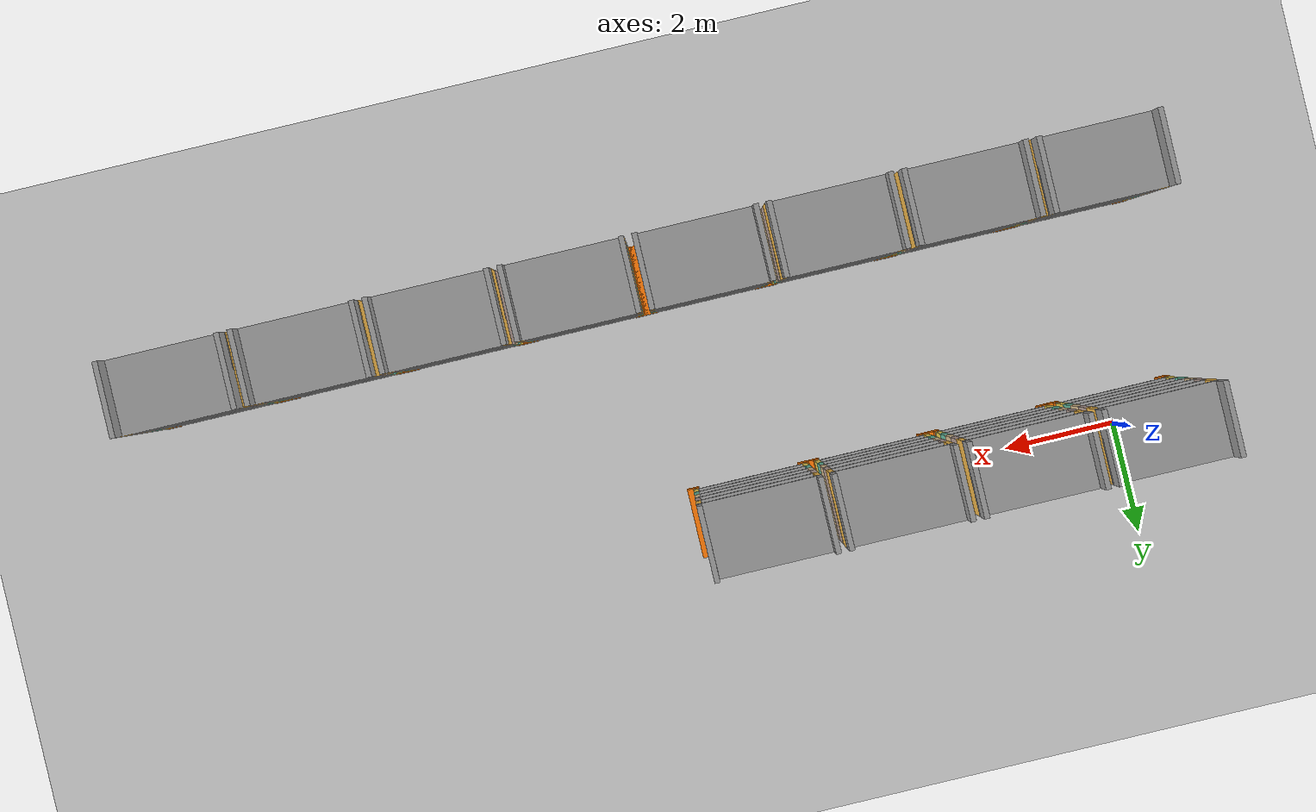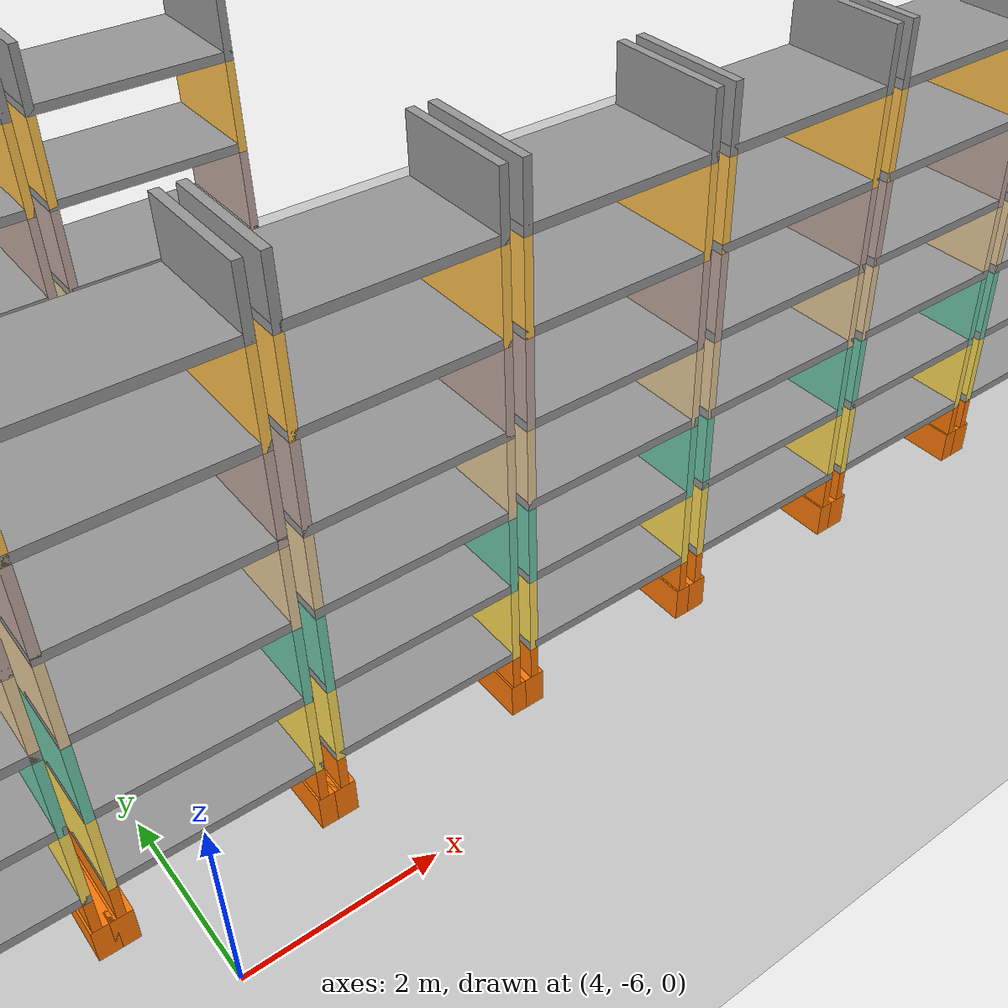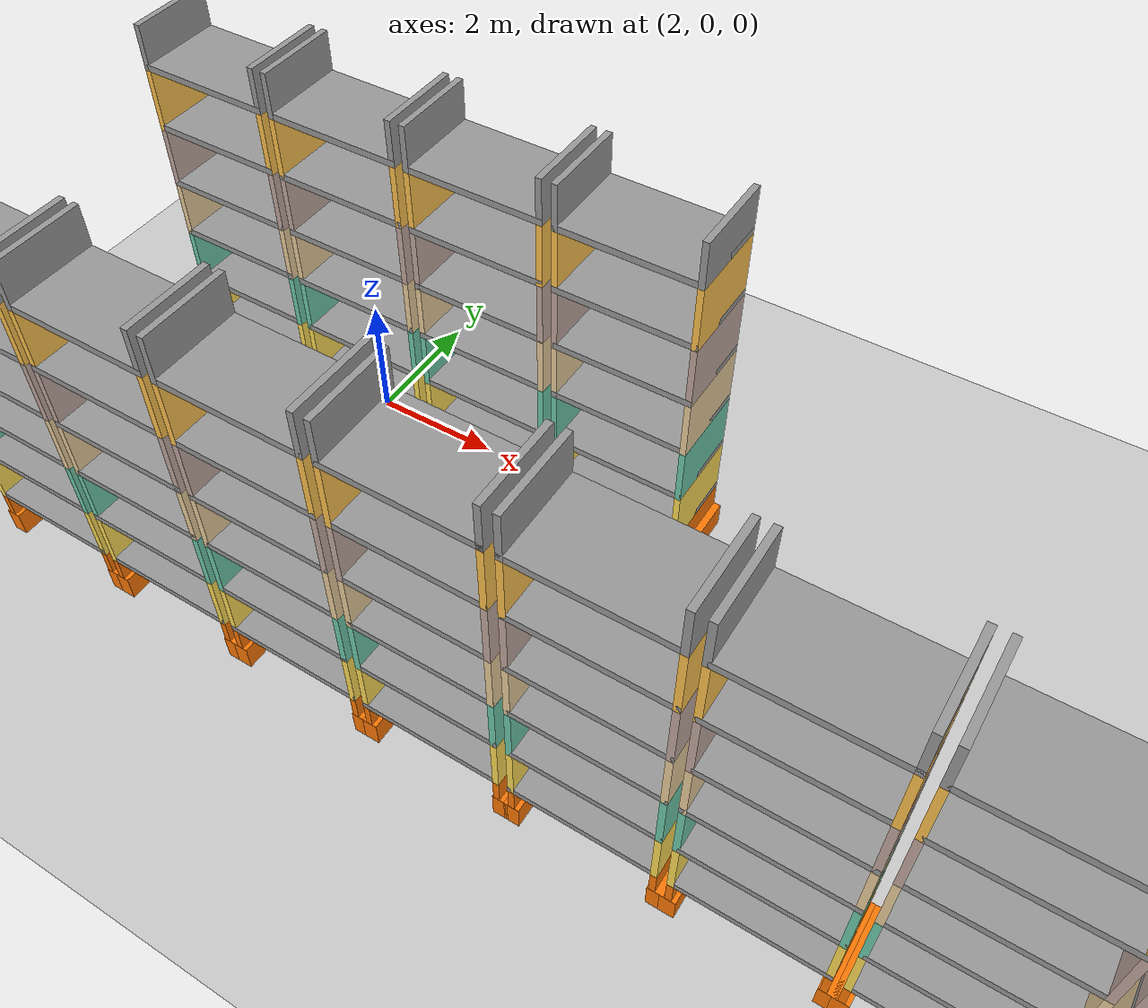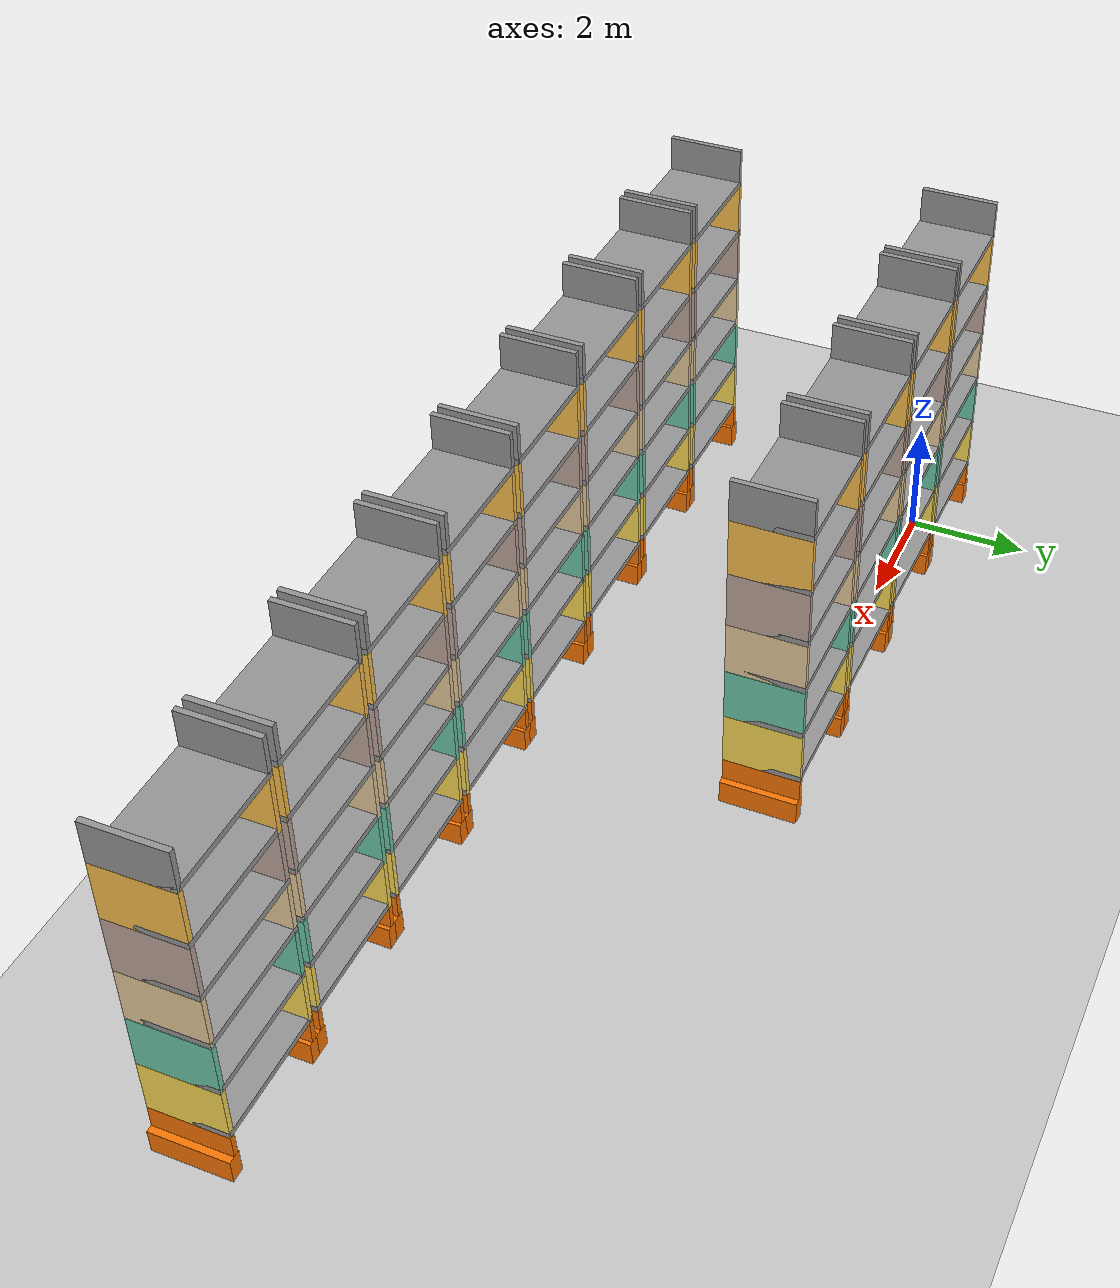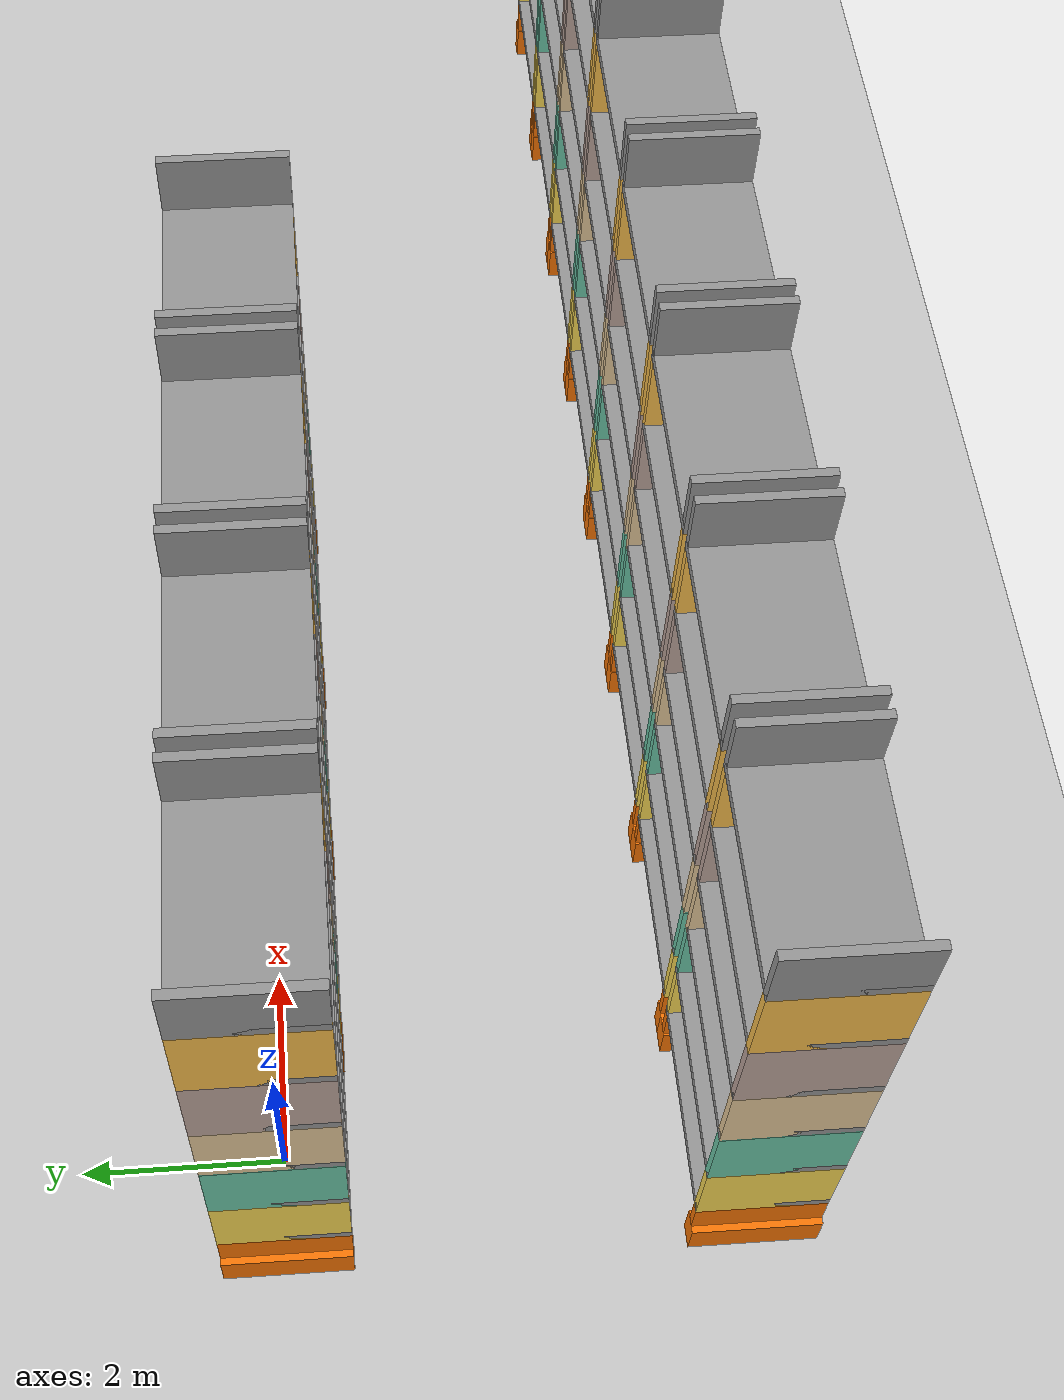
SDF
<sdf version="1.6">
 <world name="pseudo_world1">
  <light name="sun" type="directional">
   <pose>0 0 10 0 -0 0</pose>
   <diffuse>0.8 0.8 0.8 1</diffuse>
   <specular>0.2 0.2 0.2 1</specular>
   <attenuation>
    <range>1000</range>
    <constant>0.9</constant>
    <linear>0.01</linear>
    <quadratic>0.001</quadratic>
   </attenuation>
   <direction>-0.5 0.1 -0.9</direction>
  </light>
  <model name="ground_plane">
   <static>1</static>
   <link name="link">
    <collision name="collision">
     <geometry><plane><normal>0 0 1</normal><size>100 100</size></plane></geometry>
     <surface><friction><ode><mu>100</mu><mu2>50</mu2></ode></friction></surface>
    </collision>
    <visual name="visual">
     <cast_shadows>0</cast_shadows>
     <geometry><plane><normal>0 0 1</normal><size>100 100</size></plane></geometry>
     <material>
      <script><uri>file://media/materials/scripts/gazebo.material</uri><name>Gazebo/Grey</name></script>
     </material>
    </visual>
   </link>
  </model>
  <gravity>0 0 -9.8</gravity>
  <magnetic_field>6e-06 2.3e-05 -4.2e-05</magnetic_field>
  <atmosphere type="adiabatic"/>
  <physics name="default_physics" default="0" type="ode">
   <max_step_size>0.001</max_step_size>
   <real_time_factor>1</real_time_factor>
   <real_time_update_rate>1000</real_time_update_rate>
  </physics>
  <scene><ambient>0.4 0.4 0.4 1</ambient><background>0.7 0.7 0.7 1</background><shadows>1</shadows></scene>
  <spherical_coordinates>
   <surface_model>EARTH_WGS84</surface_model>
   <latitude_deg>0</latitude_deg>
   <longitude_deg>0</longitude_deg>
   <elevation>0</elevation>
   <heading_deg>0</heading_deg>
  </spherical_coordinates>
  <model name="rack_whole">
   <static>1</static>
   <link name="Base_L">
    <collision name="Base_L_Collision">
     <geometry><box><size>1.258 0.22 0.4</size></box></geometry>
     <pose>0 0 0.2 0 -0 0</pose>
    </collision>
    <visual name="Base_L_Visual">
     <pose>0 0 0.2 0 -0 0</pose>
     <geometry><box><size>1.258 0.22 0.4</size></box></geometry>
     <material>
      <script><uri>file://media/materials/scripts/gazebo.material</uri><name>Gazebo/Grey</name></script>
      <ambient>0.996078 0.47451 0.0196078 1</ambient>
     </material>
     <meta><layer>0</layer></meta>
    </visual>
    <pose>-1.02 0 0 0 -0 1.5708</pose>
   </link>
   <link name="Base_R">
    <collision name="Base_R_Collision">
     <geometry><box><size>1.258 0.22 0.4</size></box></geometry>
     <pose>0 0 0.2 0 -0 0</pose>
    </collision>
    <visual name="Base_R_Visual">
     <pose>0 0 0.2 0 -0 0</pose>
     <geometry><box><size>1.258 0.22 0.4</size></box></geometry>
     <material>
      <script><uri>file://media/materials/scripts/gazebo.material</uri><name>Gazebo/Grey</name></script>
      <ambient>0.996078 0.47451 0.0196078 1</ambient>
     </material>
     <meta><layer>0</layer></meta>
    </visual>
    <pose>1.02 0 0 0 -0 1.5708</pose>
   </link>
   <link name="Wall_1_L">
    <collision name="Wall_1_L_Collision">
     <geometry><box><size>1.258 0.09 0.387</size></box></geometry>
     <pose>0 0 0.1935 0 -0 0</pose>
    </collision>
    <visual name="Wall_1_L_Visual">
     <pose>0 0 0.1935 0 -0 0</pose>
     <geometry><box><size>1.258 0.09 0.387</size></box></geometry>
     <material>
      <script><uri>file://media/materials/scripts/gazebo.material</uri><name>Gazebo/Grey</name></script>
      <ambient>0.996078 0.47451 0.0196078 1</ambient>
     </material>
     <meta><layer>1</layer></meta>
    </visual>
    <pose>-1.015 0 0.4 0 -0 1.5708</pose>
   </link>
   <link name="Wall_1_R">
    <collision name="Wall_1_R_Collision">
     <geometry><box><size>1.258 0.09 0.387</size></box></geometry>
     <pose>0 0 0.1935 0 -0 0</pose>
    </collision>
    <visual name="Wall_1_R_Visual">
     <pose>0 0 0.1935 0 -0 0</pose>
     <geometry><box><size>1.258 0.09 0.387</size></box></geometry>
     <material>
      <script><uri>file://media/materials/scripts/gazebo.material</uri><name>Gazebo/Grey</name></script>
      <ambient>0.996078 0.47451 0.0196078 1</ambient>
     </material>
     <meta><layer>1</layer></meta>
    </visual>
    <pose>0.975 0 0.4 0 -0 1.5708</pose>
   </link>
   <link name="Floor_1">
    <collision name="Floor_1_Collision">
     <geometry><box><size>2.08 1.258 0.1</size></box></geometry>
     <pose>0 0 0.05 0 -0 0</pose>
    </collision>
    <visual name="Floor_1_Visual">
     <pose>0 0 0.05 0 -0 0</pose>
     <geometry><box><size>2.08 1.258 0.1</size></box></geometry>
     <material>
      <script><uri>file://media/materials/scripts/gazebo.material</uri><name>Gazebo/Grey</name></script>
      <ambient>1 1 1 1</ambient>
     </material>
     <meta><layer>2</layer></meta>
    </visual>
    <pose>-0.02 0 0.787 0 -0 0</pose>
   </link>
   <link name="Wall_2_L">
    <collision name="Wall_2_L_Collision">
     <geometry><box><size>1.258 0.09 0.905</size></box></geometry>
     <pose>0 0 0.4525 0 -0 0</pose>
    </collision>
    <visual name="Wall_2_L_Visual">
     <pose>0 0 0.4525 0 -0 0</pose>
     <geometry><box><size>1.258 0.09 0.905</size></box></geometry>
     <material>
      <script><uri>file://media/materials/scripts/gazebo.material</uri><name>Gazebo/Grey</name></script>
      <ambient>1 0.87 0.34 1</ambient>
     </material>
     <meta><layer>2</layer></meta>
    </visual>
    <pose>-1.015 0 0.787 0 -0 1.5708</pose>
   </link>
   <link name="Wall_2_R">
    <collision name="Wall_2_R_Collision">
     <geometry><box><size>1.258 0.09 0.905</size></box></geometry>
     <pose>0 0 0.4525 0 -0 0</pose>
    </collision>
    <visual name="Wall_2_R_Visual">
     <pose>0 0 0.4525 0 -0 0</pose>
     <geometry><box><size>1.258 0.09 0.905</size></box></geometry>
     <material>
      <script><uri>file://media/materials/scripts/gazebo.material</uri><name>Gazebo/Grey</name></script>
      <ambient>1 0.87 0.34 1</ambient>
     </material>
     <meta><layer>2</layer></meta>
    </visual>
    <pose>0.975 0 0.787 0 -0 1.5708</pose>
   </link>
   <link name="Floor_2">
    <collision name="Floor_2_Collision">
     <geometry><box><size>2.08 1.258 0.1</size></box></geometry>
     <pose>0 0 0.05 0 -0 0</pose>
    </collision>
    <visual name="Floor_2_Visual">
     <pose>0 0 0.05 0 -0 0</pose>
     <geometry><box><size>2.08 1.258 0.1</size></box></geometry>
     <material>
      <script><uri>file://media/materials/scripts/gazebo.material</uri><name>Gazebo/Grey</name></script>
      <ambient>1 1 1 1</ambient>
     </material>
     <meta><layer>3</layer></meta>
    </visual>
    <pose>-0.02 0 1.692 0 -0 0</pose>
   </link>
   <link name="Wall_3_L">
    <collision name="Wall_3_L_Collision">
     <geometry><box><size>1.258 0.09 0.899</size></box></geometry>
     <pose>0 0 0.4495 0 -0 0</pose>
    </collision>
    <visual name="Wall_3_L_Visual">
     <pose>0 0 0.4495 0 -0 0</pose>
     <geometry><box><size>1.258 0.09 0.899</size></box></geometry>
     <material>
      <script><uri>file://media/materials/scripts/gazebo.material</uri><name>Gazebo/Grey</name></script>
      <ambient>0.435294 0.796078 0.67451 1</ambient>
     </material>
     <meta><layer>3</layer></meta>
    </visual>
    <pose>-1.015 0 1.692 0 -0 1.5708</pose>
   </link>
   <link name="Wall_3_R">
    <collision name="Wall_3_R_Collision">
     <geometry><box><size>1.258 0.09 0.899</size></box></geometry>
     <pose>0 0 0.4495 0 -0 0</pose>
    </collision>
    <visual name="Wall_3_R_Visual">
     <pose>0 0 0.4495 0 -0 0</pose>
     <geometry><box><size>1.258 0.09 0.899</size></box></geometry>
     <material>
      <script><uri>file://media/materials/scripts/gazebo.material</uri><name>Gazebo/Grey</name></script>
      <ambient>0.435294 0.796078 0.67451 1</ambient>
     </material>
     <meta><layer>3</layer></meta>
    </visual>
    <pose>0.975 0 1.692 0 -0 1.5708</pose>
   </link>
   <link name="Floor_3">
    <collision name="Floor_3_Collision">
     <geometry><box><size>2.08 1.258 0.1</size></box></geometry>
     <pose>0 0 0.05 0 -0 0</pose>
    </collision>
    <visual name="Floor_3_Visual">
     <pose>0 0 0.05 0 -0 0</pose>
     <geometry><box><size>2.08 1.258 0.1</size></box></geometry>
     <material>
      <script><uri>file://media/materials/scripts/gazebo.material</uri><name>Gazebo/Grey</name></script>
      <ambient>1 1 1 1</ambient>
     </material>
     <meta><layer>4</layer></meta>
    </visual>
    <pose>-0.02 0 2.597 0 -0 0</pose>
   </link>
   <link name="Wall_4_L">
    <collision name="Wall_4_L_Collision">
     <geometry><box><size>1.258 0.09 0.9</size></box></geometry>
     <pose>0 0 0.45 0 -0 0</pose>
    </collision>
    <visual name="Wall_4_L_Visual">
     <pose>0 0 0.45 0 -0 0</pose>
     <geometry><box><size>1.258 0.09 0.9</size></box></geometry>
     <material>
      <script><uri>file://media/materials/scripts/gazebo.material</uri><name>Gazebo/Grey</name></script>
      <ambient>0.921569 0.807843 0.615686 1</ambient>
     </material>
     <meta><layer>4</layer></meta>
    </visual>
    <pose>-1.015 0 2.597 0 -0 1.5708</pose>
   </link>
   <link name="Wall_4_R">
    <collision name="Wall_4_R_Collision">
     <geometry><box><size>1.258 0.09 0.9</size></box></geometry>
     <pose>0 0 0.45 0 -0 0</pose>
    </collision>
    <visual name="Wall_4_R_Visual">
     <pose>0 0 0.45 0 -0 0</pose>
     <geometry><box><size>1.258 0.09 0.9</size></box></geometry>
     <material>
      <script><uri>file://media/materials/scripts/gazebo.material</uri><name>Gazebo/Grey</name></script>
      <ambient>0.921569 0.807843 0.615686 1</ambient>
     </material>
     <meta><layer>4</layer></meta>
    </visual>
    <pose>0.975 0 2.597 0 -0 1.5708</pose>
   </link>
   <link name="Floor_4">
    <collision name="Floor_4_Collision">
     <geometry><box><size>2.08 1.258 0.1</size></box></geometry>
     <pose>0 0 0.05 0 -0 0</pose>
    </collision>
    <visual name="Floor_4_Visual">
     <pose>0 0 0.05 0 -0 0</pose>
     <geometry><box><size>2.08 1.258 0.1</size></box></geometry>
     <material>
      <script><uri>file://media/materials/scripts/gazebo.material</uri><name>Gazebo/Grey</name></script>
      <ambient>1 1 1 1</ambient>
     </material>
     <meta><layer>5</layer></meta>
    </visual>
    <pose>-0.02 0 3.497 0 -0 0</pose>
   </link>
   <link name="Wall_5_L">
    <collision name="Wall_5_L_Collision">
     <geometry><box><size>1.258 0.09 0.952</size></box></geometry>
     <pose>0 0 0.476 0 -0 0</pose>
    </collision>
    <visual name="Wall_5_L_Visual">
     <pose>0 0 0.476 0 -0 0</pose>
     <geometry><box><size>1.258 0.09 0.952</size></box></geometry>
     <material>
      <script><uri>file://media/materials/scripts/gazebo.material</uri><name>Gazebo/Grey</name></script>
      <ambient>0.760784 0.662745 0.627451 1</ambient>
     </material>
     <meta><layer>5</layer></meta>
    </visual>
    <pose>-1.015 0 3.497 0 -0 1.5708</pose>
   </link>
   <link name="Wall_5_R">
    <collision name="Wall_5_R_Collision">
     <geometry><box><size>1.258 0.09 0.952</size></box></geometry>
     <pose>0 0 0.476 0 -0 0</pose>
    </collision>
    <visual name="Wall_5_R_Visual">
     <pose>0 0 0.476 0 -0 0</pose>
     <geometry><box><size>1.258 0.09 0.952</size></box></geometry>
     <material>
      <script><uri>file://media/materials/scripts/gazebo.material</uri><name>Gazebo/Grey</name></script>
      <ambient>0.760784 0.662745 0.627451 1</ambient>
     </material>
     <meta><layer>5</layer></meta>
    </visual>
    <pose>0.975 0 3.497 0 -0 1.5708</pose>
   </link>
   <link name="Floor_5">
    <collision name="Floor_5_Collision">
     <geometry><box><size>2.08 1.258 0.1</size></box></geometry>
     <pose>0 0 0.05 0 -0 0</pose>
    </collision>
    <visual name="Floor_5_Visual">
     <pose>0 0 0.05 0 -0 0</pose>
     <geometry><box><size>2.08 1.258 0.1</size></box></geometry>
     <material>
      <script><uri>file://media/materials/scripts/gazebo.material</uri><name>Gazebo/Grey</name></script>
      <ambient>1 1 1 1</ambient>
     </material>
     <meta><layer>6</layer></meta>
    </visual>
    <pose>-0.02 0 4.449 0 -0 0</pose>
   </link>
   <link name="Wall_6_L">
    <collision name="Wall_6_L_Collision">
     <geometry><box><size>1.258 0.09 0.957</size></box></geometry>
     <pose>0 0 0.4785 0 -0 0</pose>
    </collision>
    <visual name="Wall_6_L_Visual">
     <pose>0 0 0.4785 0 -0 0</pose>
     <geometry><box><size>1.258 0.09 0.957</size></box></geometry>
     <material>
      <script><uri>file://media/materials/scripts/gazebo.material</uri><name>Gazebo/Grey</name></script>
      <ambient>1 0.764706 0.305882 1</ambient>
     </material>
     <meta><layer>6</layer></meta>
    </visual>
    <pose>-1.015 0 4.449 0 -0 1.5708</pose>
   </link>
   <link name="Wall_6_R">
    <collision name="Wall_6_R_Collision">
     <geometry><box><size>1.258 0.09 0.957</size></box></geometry>
     <pose>0 0 0.4785 0 -0 0</pose>
    </collision>
    <visual name="Wall_6_R_Visual">
     <pose>0 0 0.4785 0 -0 0</pose>
     <geometry><box><size>1.258 0.09 0.957</size></box></geometry>
     <material>
      <script><uri>file://media/materials/scripts/gazebo.material</uri><name>Gazebo/Grey</name></script>
      <ambient>1 0.764706 0.305882 1</ambient>
     </material>
     <meta><layer>6</layer></meta>
    </visual>
    <pose>0.975 0 4.449 0 -0 1.5708</pose>
   </link>
   <link name="Floor_6">
    <collision name="Floor_6_Collision">
     <geometry><box><size>2.08 1.258 0.1</size></box></geometry>
     <pose>0 0 0.05 0 -0 0</pose>
    </collision>
    <visual name="Floor_6_Visual">
     <pose>0 0 0.05 0 -0 0</pose>
     <geometry><box><size>2.08 1.258 0.1</size></box></geometry>
     <material>
      <script><uri>file://media/materials/scripts/gazebo.material</uri><name>Gazebo/Grey</name></script>
      <ambient>1 1 1 1</ambient>
     </material>
     <meta><layer>7</layer></meta>
    </visual>
    <pose>-0.02 0 5.406 0 -0 0</pose>
   </link>
   <link name="Wall_7_L">
    <collision name="Wall_7_L_Collision">
     <geometry><box><size>1.258 0.09 0.685</size></box></geometry>
     <pose>0 0 0.3425 0 -0 0</pose>
    </collision>
    <visual name="Wall_7_L_Visual">
     <pose>0 0 0.3425 0 -0 0</pose>
     <geometry><box><size>1.258 0.09 0.685</size></box></geometry>
     <material>
      <script><uri>file://media/materials/scripts/gazebo.material</uri><name>Gazebo/Grey</name></script>
      <ambient>1 1 1 1</ambient>
     </material>
     <meta><layer>7</layer></meta>
    </visual>
    <pose>-1.015 0 5.406 0 -0 1.5708</pose>
   </link>
   <link name="Wall_7_R">
    <collision name="Wall_7_R_Collision">
     <geometry><box><size>1.258 0.09 0.685</size></box></geometry>
     <pose>0 0 0.3425 0 -0 0</pose>
    </collision>
    <visual name="Wall_7_R_Visual">
     <pose>0 0 0.3425 0 -0 0</pose>
     <geometry><box><size>1.258 0.09 0.685</size></box></geometry>
     <material>
      <script><uri>file://media/materials/scripts/gazebo.material</uri><name>Gazebo/Grey</name></script>
      <ambient>1 1 1 1</ambient>
     </material>
     <meta><layer>7</layer></meta>
    </visual>
    <pose>0.975 0 5.406 0 -0 1.5708</pose>
   </link>
  </model>
  <model name="rack_whole_0">
   <static>1</static>
   <pose>2.21 0 0 0 -0 0</pose>
   <link name="Base_L">
    <collision name="Base_L_Collision">
     <geometry><box><size>1.258 0.22 0.4</size></box></geometry>
     <pose>0 0 0.2 0 -0 0</pose>
    </collision>
    <visual name="Base_L_Visual">
     <pose>0 0 0.2 0 -0 0</pose>
     <geometry><box><size>1.258 0.22 0.4</size></box></geometry>
     <material>
      <script><uri>file://media/materials/scripts/gazebo.material</uri><name>Gazebo/Grey</name></script>
      <ambient>0.996078 0.47451 0.0196078 1</ambient>
     </material>
     <meta><layer>0</layer></meta>
    </visual>
    <pose>-1.02 0 0 0 -0 1.5708</pose>
   </link>
   <link name="Base_R">
    <collision name="Base_R_Collision">
     <geometry><box><size>1.258 0.22 0.4</size></box></geometry>
     <pose>0 0 0.2 0 -0 0</pose>
    </collision>
    <visual name="Base_R_Visual">
     <pose>0 0 0.2 0 -0 0</pose>
     <geometry><box><size>1.258 0.22 0.4</size></box></geometry>
     <material>
      <script><uri>file://media/materials/scripts/gazebo.material</uri><name>Gazebo/Grey</name></script>
      <ambient>0.996078 0.47451 0.0196078 1</ambient>
     </material>
     <meta><layer>0</layer></meta>
    </visual>
    <pose>1.02 0 0 0 -0 1.5708</pose>
   </link>
   <link name="Wall_1_L">
    <collision name="Wall_1_L_Collision">
     <geometry><box><size>1.258 0.09 0.387</size></box></geometry>
     <pose>0 0 0.1935 0 -0 0</pose>
    </collision>
    <visual name="Wall_1_L_Visual">
     <pose>0 0 0.1935 0 -0 0</pose>
     <geometry><box><size>1.258 0.09 0.387</size></box></geometry>
     <material>
      <script><uri>file://media/materials/scripts/gazebo.material</uri><name>Gazebo/Grey</name></script>
      <ambient>0.996078 0.47451 0.0196078 1</ambient>
     </material>
     <meta><layer>1</layer></meta>
    </visual>
    <pose>-1.015 0 0.4 0 -0 1.5708</pose>
   </link>
   <link name="Wall_1_R">
    <collision name="Wall_1_R_Collision">
     <geometry><box><size>1.258 0.09 0.387</size></box></geometry>
     <pose>0 0 0.1935 0 -0 0</pose>
    </collision>
    <visual name="Wall_1_R_Visual">
     <pose>0 0 0.1935 0 -0 0</pose>
     <geometry><box><size>1.258 0.09 0.387</size></box></geometry>
     <material>
      <script><uri>file://media/materials/scripts/gazebo.material</uri><name>Gazebo/Grey</name></script>
      <ambient>0.996078 0.47451 0.0196078 1</ambient>
     </material>
     <meta><layer>1</layer></meta>
    </visual>
    <pose>0.975 0 0.4 0 -0 1.5708</pose>
   </link>
   <link name="Floor_1">
    <collision name="Floor_1_Collision">
     <geometry><box><size>2.08 1.258 0.1</size></box></geometry>
     <pose>0 0 0.05 0 -0 0</pose>
    </collision>
    <visual name="Floor_1_Visual">
     <pose>0 0 0.05 0 -0 0</pose>
     <geometry><box><size>2.08 1.258 0.1</size></box></geometry>
     <material>
      <script><uri>file://media/materials/scripts/gazebo.material</uri><name>Gazebo/Grey</name></script>
      <ambient>1 1 1 1</ambient>
     </material>
     <meta><layer>2</layer></meta>
    </visual>
    <pose>-0.02 0 0.787 0 -0 0</pose>
   </link>
   <link name="Wall_2_L">
    <collision name="Wall_2_L_Collision">
     <geometry><box><size>1.258 0.09 0.905</size></box></geometry>
     <pose>0 0 0.4525 0 -0 0</pose>
    </collision>
    <visual name="Wall_2_L_Visual">
     <pose>0 0 0.4525 0 -0 0</pose>
     <geometry><box><size>1.258 0.09 0.905</size></box></geometry>
     <material>
      <script><uri>file://media/materials/scripts/gazebo.material</uri><name>Gazebo/Grey</name></script>
      <ambient>1 0.87 0.34 1</ambient>
     </material>
     <meta><layer>2</layer></meta>
    </visual>
    <pose>-1.015 0 0.787 0 -0 1.5708</pose>
   </link>
   <link name="Wall_2_R">
    <collision name="Wall_2_R_Collision">
     <geometry><box><size>1.258 0.09 0.905</size></box></geometry>
     <pose>0 0 0.4525 0 -0 0</pose>
    </collision>
    <visual name="Wall_2_R_Visual">
     <pose>0 0 0.4525 0 -0 0</pose>
     <geometry><box><size>1.258 0.09 0.905</size></box></geometry>
     <material>
      <script><uri>file://media/materials/scripts/gazebo.material</uri><name>Gazebo/Grey</name></script>
      <ambient>1 0.87 0.34 1</ambient>
     </material>
     <meta><layer>2</layer></meta>
    </visual>
    <pose>0.975 0 0.787 0 -0 1.5708</pose>
   </link>
   <link name="Floor_2">
    <collision name="Floor_2_Collision">
     <geometry><box><size>2.08 1.258 0.1</size></box></geometry>
     <pose>0 0 0.05 0 -0 0</pose>
    </collision>
    <visual name="Floor_2_Visual">
     <pose>0 0 0.05 0 -0 0</pose>
     <geometry><box><size>2.08 1.258 0.1</size></box></geometry>
     <material>
      <script><uri>file://media/materials/scripts/gazebo.material</uri><name>Gazebo/Grey</name></script>
      <ambient>1 1 1 1</ambient>
     </material>
     <meta><layer>3</layer></meta>
    </visual>
    <pose>-0.02 0 1.692 0 -0 0</pose>
   </link>
   <link name="Wall_3_L">
    <collision name="Wall_3_L_Collision">
     <geometry><box><size>1.258 0.09 0.899</size></box></geometry>
     <pose>0 0 0.4495 0 -0 0</pose>
    </collision>
    <visual name="Wall_3_L_Visual">
     <pose>0 0 0.4495 0 -0 0</pose>
     <geometry><box><size>1.258 0.09 0.899</size></box></geometry>
     <material>
      <script><uri>file://media/materials/scripts/gazebo.material</uri><name>Gazebo/Grey</name></script>
      <ambient>0.435294 0.796078 0.67451 1</ambient>
     </material>
     <meta><layer>3</layer></meta>
    </visual>
    <pose>-1.015 0 1.692 0 -0 1.5708</pose>
   </link>
   <link name="Wall_3_R">
    <collision name="Wall_3_R_Collision">
     <geometry><box><size>1.258 0.09 0.899</size></box></geometry>
     <pose>0 0 0.4495 0 -0 0</pose>
    </collision>
    <visual name="Wall_3_R_Visual">
     <pose>0 0 0.4495 0 -0 0</pose>
     <geometry><box><size>1.258 0.09 0.899</size></box></geometry>
     <material>
      <script><uri>file://media/materials/scripts/gazebo.material</uri><name>Gazebo/Grey</name></script>
      <ambient>0.435294 0.796078 0.67451 1</ambient>
     </material>
     <meta><layer>3</layer></meta>
    </visual>
    <pose>0.975 0 1.692 0 -0 1.5708</pose>
   </link>
   <link name="Floor_3">
    <collision name="Floor_3_Collision">
     <geometry><box><size>2.08 1.258 0.1</size></box></geometry>
     <pose>0 0 0.05 0 -0 0</pose>
    </collision>
    <visual name="Floor_3_Visual">
     <pose>0 0 0.05 0 -0 0</pose>
     <geometry><box><size>2.08 1.258 0.1</size></box></geometry>
     <material>
      <script><uri>file://media/materials/scripts/gazebo.material</uri><name>Gazebo/Grey</name></script>
      <ambient>1 1 1 1</ambient>
     </material>
     <meta><layer>4</layer></meta>
    </visual>
    <pose>-0.02 0 2.597 0 -0 0</pose>
   </link>
   <link name="Wall_4_L">
    <collision name="Wall_4_L_Collision">
     <geometry><box><size>1.258 0.09 0.9</size></box></geometry>
     <pose>0 0 0.45 0 -0 0</pose>
    </collision>
    <visual name="Wall_4_L_Visual">
     <pose>0 0 0.45 0 -0 0</pose>
     <geometry><box><size>1.258 0.09 0.9</size></box></geometry>
     <material>
      <script><uri>file://media/materials/scripts/gazebo.material</uri><name>Gazebo/Grey</name></script>
      <ambient>0.921569 0.807843 0.615686 1</ambient>
     </material>
     <meta><layer>4</layer></meta>
    </visual>
    <pose>-1.015 0 2.597 0 -0 1.5708</pose>
   </link>
   <link name="Wall_4_R">
    <collision name="Wall_4_R_Collision">
     <geometry><box><size>1.258 0.09 0.9</size></box></geometry>
     <pose>0 0 0.45 0 -0 0</pose>
    </collision>
    <visual name="Wall_4_R_Visual">
     <pose>0 0 0.45 0 -0 0</pose>
     <geometry><box><size>1.258 0.09 0.9</size></box></geometry>
     <material>
      <script><uri>file://media/materials/scripts/gazebo.material</uri><name>Gazebo/Grey</name></script>
      <ambient>0.921569 0.807843 0.615686 1</ambient>
     </material>
     <meta><layer>4</layer></meta>
    </visual>
    <pose>0.975 0 2.597 0 -0 1.5708</pose>
   </link>
   <link name="Floor_4">
    <collision name="Floor_4_Collision">
     <geometry><box><size>2.08 1.258 0.1</size></box></geometry>
     <pose>0 0 0.05 0 -0 0</pose>
    </collision>
    <visual name="Floor_4_Visual">
     <pose>0 0 0.05 0 -0 0</pose>
     <geometry><box><size>2.08 1.258 0.1</size></box></geometry>
     <material>
      <script><uri>file://media/materials/scripts/gazebo.material</uri><name>Gazebo/Grey</name></script>
      <ambient>1 1 1 1</ambient>
     </material>
     <meta><layer>5</layer></meta>
    </visual>
    <pose>-0.02 0 3.497 0 -0 0</pose>
   </link>
   <link name="Wall_5_L">
    <collision name="Wall_5_L_Collision">
     <geometry><box><size>1.258 0.09 0.952</size></box></geometry>
     <pose>0 0 0.476 0 -0 0</pose>
    </collision>
    <visual name="Wall_5_L_Visual">
     <pose>0 0 0.476 0 -0 0</pose>
     <geometry><box><size>1.258 0.09 0.952</size></box></geometry>
     <material>
      <script><uri>file://media/materials/scripts/gazebo.material</uri><name>Gazebo/Grey</name></script>
      <ambient>0.760784 0.662745 0.627451 1</ambient>
     </material>
     <meta><layer>5</layer></meta>
    </visual>
    <pose>-1.015 0 3.497 0 -0 1.5708</pose>
   </link>
   <link name="Wall_5_R">
    <collision name="Wall_5_R_Collision">
     <geometry><box><size>1.258 0.09 0.952</size></box></geometry>
     <pose>0 0 0.476 0 -0 0</pose>
    </collision>
    <visual name="Wall_5_R_Visual">
     <pose>0 0 0.476 0 -0 0</pose>
     <geometry><box><size>1.258 0.09 0.952</size></box></geometry>
     <material>
      <script><uri>file://media/materials/scripts/gazebo.material</uri><name>Gazebo/Grey</name></script>
      <ambient>0.760784 0.662745 0.627451 1</ambient>
     </material>
     <meta><layer>5</layer></meta>
    </visual>
    <pose>0.975 0 3.497 0 -0 1.5708</pose>
   </link>
   <link name="Floor_5">
    <collision name="Floor_5_Collision">
     <geometry><box><size>2.08 1.258 0.1</size></box></geometry>
     <pose>0 0 0.05 0 -0 0</pose>
    </collision>
    <visual name="Floor_5_Visual">
     <pose>0 0 0.05 0 -0 0</pose>
     <geometry><box><size>2.08 1.258 0.1</size></box></geometry>
     <material>
      <script><uri>file://media/materials/scripts/gazebo.material</uri><name>Gazebo/Grey</name></script>
      <ambient>1 1 1 1</ambient>
     </material>
     <meta><layer>6</layer></meta>
    </visual>
    <pose>-0.02 0 4.449 0 -0 0</pose>
   </link>
   <link name="Wall_6_L">
    <collision name="Wall_6_L_Collision">
     <geometry><box><size>1.258 0.09 0.957</size></box></geometry>
     <pose>0 0 0.4785 0 -0 0</pose>
    </collision>
    <visual name="Wall_6_L_Visual">
     <pose>0 0 0.4785 0 -0 0</pose>
     <geometry><box><size>1.258 0.09 0.957</size></box></geometry>
     <material>
      <script><uri>file://media/materials/scripts/gazebo.material</uri><name>Gazebo/Grey</name></script>
      <ambient>1 0.764706 0.305882 1</ambient>
     </material>
     <meta><layer>6</layer></meta>
    </visual>
    <pose>-1.015 0 4.449 0 -0 1.5708</pose>
   </link>
   <link name="Wall_6_R">
    <collision name="Wall_6_R_Collision">
     <geometry><box><size>1.258 0.09 0.957</size></box></geometry>
     <pose>0 0 0.4785 0 -0 0</pose>
    </collision>
    <visual name="Wall_6_R_Visual">
     <pose>0 0 0.4785 0 -0 0</pose>
     <geometry><box><size>1.258 0.09 0.957</size></box></geometry>
     <material>
      <script><uri>file://media/materials/scripts/gazebo.material</uri><name>Gazebo/Grey</name></script>
      <ambient>1 0.764706 0.305882 1</ambient>
     </material>
     <meta><layer>6</layer></meta>
    </visual>
    <pose>0.975 0 4.449 0 -0 1.5708</pose>
   </link>
   <link name="Floor_6">
    <collision name="Floor_6_Collision">
     <geometry><box><size>2.08 1.258 0.1</size></box></geometry>
     <pose>0 0 0.05 0 -0 0</pose>
    </collision>
    <visual name="Floor_6_Visual">
     <pose>0 0 0.05 0 -0 0</pose>
     <geometry><box><size>2.08 1.258 0.1</size></box></geometry>
     <material>
      <script><uri>file://media/materials/scripts/gazebo.material</uri><name>Gazebo/Grey</name></script>
      <ambient>1 1 1 1</ambient>
     </material>
     <meta><layer>7</layer></meta>
    </visual>
    <pose>-0.02 0 5.406 0 -0 0</pose>
   </link>
   <link name="Wall_7_L">
    <collision name="Wall_7_L_Collision">
     <geometry><box><size>1.258 0.09 0.685</size></box></geometry>
     <pose>0 0 0.3425 0 -0 0</pose>
    </collision>
    <visual name="Wall_7_L_Visual">
     <pose>0 0 0.3425 0 -0 0</pose>
     <geometry><box><size>1.258 0.09 0.685</size></box></geometry>
     <material>
      <script><uri>file://media/materials/scripts/gazebo.material</uri><name>Gazebo/Grey</name></script>
      <ambient>1 1 1 1</ambient>
     </material>
     <meta><layer>7</layer></meta>
    </visual>
    <pose>-1.015 0 5.406 0 -0 1.5708</pose>
   </link>
   <link name="Wall_7_R">
    <collision name="Wall_7_R_Collision">
     <geometry><box><size>1.258 0.09 0.685</size></box></geometry>
     <pose>0 0 0.3425 0 -0 0</pose>
    </collision>
    <visual name="Wall_7_R_Visual">
     <pose>0 0 0.3425 0 -0 0</pose>
     <geometry><box><size>1.258 0.09 0.685</size></box></geometry>
     <material>
      <script><uri>file://media/materials/scripts/gazebo.material</uri><name>Gazebo/Grey</name></script>
      <ambient>1 1 1 1</ambient>
     </material>
     <meta><layer>7</layer></meta>
    </visual>
    <pose>0.975 0 5.406 0 -0 1.5708</pose>
   </link>
  </model>
  <model name="rack_whole_1">
   <static>1</static>
   <pose>4.42 0 0 0 -0 0</pose>
   <link name="Base_L">
    <collision name="Base_L_Collision">
     <geometry><box><size>1.258 0.22 0.4</size></box></geometry>
     <pose>0 0 0.2 0 -0 0</pose>
    </collision>
    <visual name="Base_L_Visual">
     <pose>0 0 0.2 0 -0 0</pose>
     <geometry><box><size>1.258 0.22 0.4</size></box></geometry>
     <material>
      <script><uri>file://media/materials/scripts/gazebo.material</uri><name>Gazebo/Grey</name></script>
      <ambient>0.996078 0.47451 0.0196078 1</ambient>
     </material>
     <meta><layer>0</layer></meta>
    </visual>
    <pose>-1.02 0 0 0 -0 1.5708</pose>
   </link>
   <link name="Base_R">
    <collision name="Base_R_Collision">
     <geometry><box><size>1.258 0.22 0.4</size></box></geometry>
     <pose>0 0 0.2 0 -0 0</pose>
    </collision>
    <visual name="Base_R_Visual">
     <pose>0 0 0.2 0 -0 0</pose>
     <geometry><box><size>1.258 0.22 0.4</size></box></geometry>
     <material>
      <script><uri>file://media/materials/scripts/gazebo.material</uri><name>Gazebo/Grey</name></script>
      <ambient>0.996078 0.47451 0.0196078 1</ambient>
     </material>
     <meta><layer>0</layer></meta>
    </visual>
    <pose>1.02 0 0 0 -0 1.5708</pose>
   </link>
   <link name="Wall_1_L">
    <collision name="Wall_1_L_Collision">
     <geometry><box><size>1.258 0.09 0.387</size></box></geometry>
     <pose>0 0 0.1935 0 -0 0</pose>
    </collision>
    <visual name="Wall_1_L_Visual">
     <pose>0 0 0.1935 0 -0 0</pose>
     <geometry><box><size>1.258 0.09 0.387</size></box></geometry>
     <material>
      <script><uri>file://media/materials/scripts/gazebo.material</uri><name>Gazebo/Grey</name></script>
      <ambient>0.996078 0.47451 0.0196078 1</ambient>
     </material>
     <meta><layer>1</layer></meta>
    </visual>
    <pose>-1.015 0 0.4 0 -0 1.5708</pose>
   </link>
   <link name="Wall_1_R">
    <collision name="Wall_1_R_Collision">
     <geometry><box><size>1.258 0.09 0.387</size></box></geometry>
     <pose>0 0 0.1935 0 -0 0</pose>
    </collision>
    <visual name="Wall_1_R_Visual">
     <pose>0 0 0.1935 0 -0 0</pose>
     <geometry><box><size>1.258 0.09 0.387</size></box></geometry>
     <material>
      <script><uri>file://media/materials/scripts/gazebo.material</uri><name>Gazebo/Grey</name></script>
      <ambient>0.996078 0.47451 0.0196078 1</ambient>
     </material>
     <meta><layer>1</layer></meta>
    </visual>
    <pose>0.975 0 0.4 0 -0 1.5708</pose>
   </link>
   <link name="Floor_1">
    <collision name="Floor_1_Collision">
     <geometry><box><size>2.08 1.258 0.1</size></box></geometry>
     <pose>0 0 0.05 0 -0 0</pose>
    </collision>
    <visual name="Floor_1_Visual">
     <pose>0 0 0.05 0 -0 0</pose>
     <geometry><box><size>2.08 1.258 0.1</size></box></geometry>
     <material>
      <script><uri>file://media/materials/scripts/gazebo.material</uri><name>Gazebo/Grey</name></script>
      <ambient>1 1 1 1</ambient>
     </material>
     <meta><layer>2</layer></meta>
    </visual>
    <pose>-0.02 0 0.787 0 -0 0</pose>
   </link>
   <link name="Wall_2_L">
    <collision name="Wall_2_L_Collision">
     <geometry><box><size>1.258 0.09 0.905</size></box></geometry>
     <pose>0 0 0.4525 0 -0 0</pose>
    </collision>
    <visual name="Wall_2_L_Visual">
     <pose>0 0 0.4525 0 -0 0</pose>
     <geometry><box><size>1.258 0.09 0.905</size></box></geometry>
     <material>
      <script><uri>file://media/materials/scripts/gazebo.material</uri><name>Gazebo/Grey</name></script>
      <ambient>1 0.87 0.34 1</ambient>
     </material>
     <meta><layer>2</layer></meta>
    </visual>
    <pose>-1.015 0 0.787 0 -0 1.5708</pose>
   </link>
   <link name="Wall_2_R">
    <collision name="Wall_2_R_Collision">
     <geometry><box><size>1.258 0.09 0.905</size></box></geometry>
     <pose>0 0 0.4525 0 -0 0</pose>
    </collision>
    <visual name="Wall_2_R_Visual">
     <pose>0 0 0.4525 0 -0 0</pose>
     <geometry><box><size>1.258 0.09 0.905</size></box></geometry>
     <material>
      <script><uri>file://media/materials/scripts/gazebo.material</uri><name>Gazebo/Grey</name></script>
      <ambient>1 0.87 0.34 1</ambient>
     </material>
     <meta><layer>2</layer></meta>
    </visual>
    <pose>0.975 0 0.787 0 -0 1.5708</pose>
   </link>
   <link name="Floor_2">
    <collision name="Floor_2_Collision">
     <geometry><box><size>2.08 1.258 0.1</size></box></geometry>
     <pose>0 0 0.05 0 -0 0</pose>
    </collision>
    <visual name="Floor_2_Visual">
     <pose>0 0 0.05 0 -0 0</pose>
     <geometry><box><size>2.08 1.258 0.1</size></box></geometry>
     <material>
      <script><uri>file://media/materials/scripts/gazebo.material</uri><name>Gazebo/Grey</name></script>
      <ambient>1 1 1 1</ambient>
     </material>
     <meta><layer>3</layer></meta>
    </visual>
    <pose>-0.02 0 1.692 0 -0 0</pose>
   </link>
   <link name="Wall_3_L">
    <collision name="Wall_3_L_Collision">
     <geometry><box><size>1.258 0.09 0.899</size></box></geometry>
     <pose>0 0 0.4495 0 -0 0</pose>
    </collision>
    <visual name="Wall_3_L_Visual">
     <pose>0 0 0.4495 0 -0 0</pose>
     <geometry><box><size>1.258 0.09 0.899</size></box></geometry>
     <material>
      <script><uri>file://media/materials/scripts/gazebo.material</uri><name>Gazebo/Grey</name></script>
      <ambient>0.435294 0.796078 0.67451 1</ambient>
     </material>
     <meta><layer>3</layer></meta>
    </visual>
    <pose>-1.015 0 1.692 0 -0 1.5708</pose>
   </link>
   <link name="Wall_3_R">
    <collision name="Wall_3_R_Collision">
     <geometry><box><size>1.258 0.09 0.899</size></box></geometry>
     <pose>0 0 0.4495 0 -0 0</pose>
    </collision>
    <visual name="Wall_3_R_Visual">
     <pose>0 0 0.4495 0 -0 0</pose>
     <geometry><box><size>1.258 0.09 0.899</size></box></geometry>
     <material>
      <script><uri>file://media/materials/scripts/gazebo.material</uri><name>Gazebo/Grey</name></script>
      <ambient>0.435294 0.796078 0.67451 1</ambient>
     </material>
     <meta><layer>3</layer></meta>
    </visual>
    <pose>0.975 0 1.692 0 -0 1.5708</pose>
   </link>
   <link name="Floor_3">
    <collision name="Floor_3_Collision">
     <geometry><box><size>2.08 1.258 0.1</size></box></geometry>
     <pose>0 0 0.05 0 -0 0</pose>
    </collision>
    <visual name="Floor_3_Visual">
     <pose>0 0 0.05 0 -0 0</pose>
     <geometry><box><size>2.08 1.258 0.1</size></box></geometry>
     <material>
      <script><uri>file://media/materials/scripts/gazebo.material</uri><name>Gazebo/Grey</name></script>
      <ambient>1 1 1 1</ambient>
     </material>
     <meta><layer>4</layer></meta>
    </visual>
    <pose>-0.02 0 2.597 0 -0 0</pose>
   </link>
   <link name="Wall_4_L">
    <collision name="Wall_4_L_Collision">
     <geometry><box><size>1.258 0.09 0.9</size></box></geometry>
     <pose>0 0 0.45 0 -0 0</pose>
    </collision>
    <visual name="Wall_4_L_Visual">
     <pose>0 0 0.45 0 -0 0</pose>
     <geometry><box><size>1.258 0.09 0.9</size></box></geometry>
     <material>
      <script><uri>file://media/materials/scripts/gazebo.material</uri><name>Gazebo/Grey</name></script>
      <ambient>0.921569 0.807843 0.615686 1</ambient>
     </material>
     <meta><layer>4</layer></meta>
    </visual>
    <pose>-1.015 0 2.597 0 -0 1.5708</pose>
   </link>
   <link name="Wall_4_R">
    <collision name="Wall_4_R_Collision">
     <geometry><box><size>1.258 0.09 0.9</size></box></geometry>
     <pose>0 0 0.45 0 -0 0</pose>
    </collision>
    <visual name="Wall_4_R_Visual">
     <pose>0 0 0.45 0 -0 0</pose>
     <geometry><box><size>1.258 0.09 0.9</size></box></geometry>
     <material>
      <script><uri>file://media/materials/scripts/gazebo.material</uri><name>Gazebo/Grey</name></script>
      <ambient>0.921569 0.807843 0.615686 1</ambient>
     </material>
     <meta><layer>4</layer></meta>
    </visual>
    <pose>0.975 0 2.597 0 -0 1.5708</pose>
   </link>
   <link name="Floor_4">
    <collision name="Floor_4_Collision">
     <geometry><box><size>2.08 1.258 0.1</size></box></geometry>
     <pose>0 0 0.05 0 -0 0</pose>
    </collision>
    <visual name="Floor_4_Visual">
     <pose>0 0 0.05 0 -0 0</pose>
     <geometry><box><size>2.08 1.258 0.1</size></box></geometry>
     <material>
      <script><uri>file://media/materials/scripts/gazebo.material</uri><name>Gazebo/Grey</name></script>
      <ambient>1 1 1 1</ambient>
     </material>
     <meta><layer>5</layer></meta>
    </visual>
    <pose>-0.02 0 3.497 0 -0 0</pose>
   </link>
   <link name="Wall_5_L">
    <collision name="Wall_5_L_Collision">
     <geometry><box><size>1.258 0.09 0.952</size></box></geometry>
     <pose>0 0 0.476 0 -0 0</pose>
    </collision>
    <visual name="Wall_5_L_Visual">
     <pose>0 0 0.476 0 -0 0</pose>
     <geometry><box><size>1.258 0.09 0.952</size></box></geometry>
     <material>
      <script><uri>file://media/materials/scripts/gazebo.material</uri><name>Gazebo/Grey</name></script>
      <ambient>0.760784 0.662745 0.627451 1</ambient>
     </material>
     <meta><layer>5</layer></meta>
    </visual>
    <pose>-1.015 0 3.497 0 -0 1.5708</pose>
   </link>
   <link name="Wall_5_R">
    <collision name="Wall_5_R_Collision">
     <geometry><box><size>1.258 0.09 0.952</size></box></geometry>
     <pose>0 0 0.476 0 -0 0</pose>
    </collision>
    <visual name="Wall_5_R_Visual">
     <pose>0 0 0.476 0 -0 0</pose>
     <geometry><box><size>1.258 0.09 0.952</size></box></geometry>
     <material>
      <script><uri>file://media/materials/scripts/gazebo.material</uri><name>Gazebo/Grey</name></script>
      <ambient>0.760784 0.662745 0.627451 1</ambient>
     </material>
     <meta><layer>5</layer></meta>
    </visual>
    <pose>0.975 0 3.497 0 -0 1.5708</pose>
   </link>
   <link name="Floor_5">
    <collision name="Floor_5_Collision">
     <geometry><box><size>2.08 1.258 0.1</size></box></geometry>
     <pose>0 0 0.05 0 -0 0</pose>
    </collision>
    <visual name="Floor_5_Visual">
     <pose>0 0 0.05 0 -0 0</pose>
     <geometry><box><size>2.08 1.258 0.1</size></box></geometry>
     <material>
      <script><uri>file://media/materials/scripts/gazebo.material</uri><name>Gazebo/Grey</name></script>
      <ambient>1 1 1 1</ambient>
     </material>
     <meta><layer>6</layer></meta>
    </visual>
    <pose>-0.02 0 4.449 0 -0 0</pose>
   </link>
   <link name="Wall_6_L">
    <collision name="Wall_6_L_Collision">
     <geometry><box><size>1.258 0.09 0.957</size></box></geometry>
     <pose>0 0 0.4785 0 -0 0</pose>
    </collision>
    <visual name="Wall_6_L_Visual">
     <pose>0 0 0.4785 0 -0 0</pose>
     <geometry><box><size>1.258 0.09 0.957</size></box></geometry>
     <material>
      <script><uri>file://media/materials/scripts/gazebo.material</uri><name>Gazebo/Grey</name></script>
      <ambient>1 0.764706 0.305882 1</ambient>
     </material>
     <meta><layer>6</layer></meta>
    </visual>
    <pose>-1.015 0 4.449 0 -0 1.5708</pose>
   </link>
   <link name="Wall_6_R">
    <collision name="Wall_6_R_Collision">
     <geometry><box><size>1.258 0.09 0.957</size></box></geometry>
     <pose>0 0 0.4785 0 -0 0</pose>
    </collision>
    <visual name="Wall_6_R_Visual">
     <pose>0 0 0.4785 0 -0 0</pose>
     <geometry><box><size>1.258 0.09 0.957</size></box></geometry>
     <material>
      <script><uri>file://media/materials/scripts/gazebo.material</uri><name>Gazebo/Grey</name></script>
      <ambient>1 0.764706 0.305882 1</ambient>
     </material>
     <meta><layer>6</layer></meta>
    </visual>
    <pose>0.975 0 4.449 0 -0 1.5708</pose>
   </link>
   <link name="Floor_6">
    <collision name="Floor_6_Collision">
     <geometry><box><size>2.08 1.258 0.1</size></box></geometry>
     <pose>0 0 0.05 0 -0 0</pose>
    </collision>
    <visual name="Floor_6_Visual">
     <pose>0 0 0.05 0 -0 0</pose>
     <geometry><box><size>2.08 1.258 0.1</size></box></geometry>
     <material>
      <script><uri>file://media/materials/scripts/gazebo.material</uri><name>Gazebo/Grey</name></script>
      <ambient>1 1 1 1</ambient>
     </material>
     <meta><layer>7</layer></meta>
    </visual>
    <pose>-0.02 0 5.406 0 -0 0</pose>
   </link>
   <link name="Wall_7_L">
    <collision name="Wall_7_L_Collision">
     <geometry><box><size>1.258 0.09 0.685</size></box></geometry>
     <pose>0 0 0.3425 0 -0 0</pose>
    </collision>
    <visual name="Wall_7_L_Visual">
     <pose>0 0 0.3425 0 -0 0</pose>
     <geometry><box><size>1.258 0.09 0.685</size></box></geometry>
     <material>
      <script><uri>file://media/materials/scripts/gazebo.material</uri><name>Gazebo/Grey</name></script>
      <ambient>1 1 1 1</ambient>
     </material>
     <meta><layer>7</layer></meta>
    </visual>
    <pose>-1.015 0 5.406 0 -0 1.5708</pose>
   </link>
   <link name="Wall_7_R">
    <collision name="Wall_7_R_Collision">
     <geometry><box><size>1.258 0.09 0.685</size></box></geometry>
     <pose>0 0 0.3425 0 -0 0</pose>
    </collision>
    <visual name="Wall_7_R_Visual">
     <pose>0 0 0.3425 0 -0 0</pose>
     <geometry><box><size>1.258 0.09 0.685</size></box></geometry>
     <material>
      <script><uri>file://media/materials/scripts/gazebo.material</uri><name>Gazebo/Grey</name></script>
      <ambient>1 1 1 1</ambient>
     </material>
     <meta><layer>7</layer></meta>
    </visual>
    <pose>0.975 0 5.406 0 -0 1.5708</pose>
   </link>
  </model>
  <model name="rack_whole_2">
   <static>1</static>
   <pose>6.63 0 0 0 -0 0</pose>
   <link name="Base_L">
    <collision name="Base_L_Collision">
     <geometry><box><size>1.258 0.22 0.4</size></box></geometry>
     <pose>0 0 0.2 0 -0 0</pose>
    </collision>
    <visual name="Base_L_Visual">
     <pose>0 0 0.2 0 -0 0</pose>
     <geometry><box><size>1.258 0.22 0.4</size></box></geometry>
     <material>
      <script><uri>file://media/materials/scripts/gazebo.material</uri><name>Gazebo/Grey</name></script>
      <ambient>0.996078 0.47451 0.0196078 1</ambient>
     </material>
     <meta><layer>0</layer></meta>
    </visual>
    <pose>-1.02 0 0 0 -0 1.5708</pose>
   </link>
   <link name="Base_R">
    <collision name="Base_R_Collision">
     <geometry><box><size>1.258 0.22 0.4</size></box></geometry>
     <pose>0 0 0.2 0 -0 0</pose>
    </collision>
    <visual name="Base_R_Visual">
     <pose>0 0 0.2 0 -0 0</pose>
     <geometry><box><size>1.258 0.22 0.4</size></box></geometry>
     <material>
      <script><uri>file://media/materials/scripts/gazebo.material</uri><name>Gazebo/Grey</name></script>
      <ambient>0.996078 0.47451 0.0196078 1</ambient>
     </material>
     <meta><layer>0</layer></meta>
    </visual>
    <pose>1.02 0 0 0 -0 1.5708</pose>
   </link>
   <link name="Wall_1_L">
    <collision name="Wall_1_L_Collision">
     <geometry><box><size>1.258 0.09 0.387</size></box></geometry>
     <pose>0 0 0.1935 0 -0 0</pose>
    </collision>
    <visual name="Wall_1_L_Visual">
     <pose>0 0 0.1935 0 -0 0</pose>
     <geometry><box><size>1.258 0.09 0.387</size></box></geometry>
     <material>
      <script><uri>file://media/materials/scripts/gazebo.material</uri><name>Gazebo/Grey</name></script>
      <ambient>0.996078 0.47451 0.0196078 1</ambient>
     </material>
     <meta><layer>1</layer></meta>
    </visual>
    <pose>-1.015 0 0.4 0 -0 1.5708</pose>
   </link>
   <link name="Wall_1_R">
    <collision name="Wall_1_R_Collision">
     <geometry><box><size>1.258 0.09 0.387</size></box></geometry>
     <pose>0 0 0.1935 0 -0 0</pose>
    </collision>
    <visual name="Wall_1_R_Visual">
     <pose>0 0 0.1935 0 -0 0</pose>
     <geometry><box><size>1.258 0.09 0.387</size></box></geometry>
     <material>
      <script><uri>file://media/materials/scripts/gazebo.material</uri><name>Gazebo/Grey</name></script>
      <ambient>0.996078 0.47451 0.0196078 1</ambient>
     </material>
     <meta><layer>1</layer></meta>
    </visual>
    <pose>0.975 0 0.4 0 -0 1.5708</pose>
   </link>
   <link name="Floor_1">
    <collision name="Floor_1_Collision">
     <geometry><box><size>2.08 1.258 0.1</size></box></geometry>
     <pose>0 0 0.05 0 -0 0</pose>
    </collision>
    <visual name="Floor_1_Visual">
     <pose>0 0 0.05 0 -0 0</pose>
     <geometry><box><size>2.08 1.258 0.1</size></box></geometry>
     <material>
      <script><uri>file://media/materials/scripts/gazebo.material</uri><name>Gazebo/Grey</name></script>
      <ambient>1 1 1 1</ambient>
     </material>
     <meta><layer>2</layer></meta>
    </visual>
    <pose>-0.02 0 0.787 0 -0 0</pose>
   </link>
   <link name="Wall_2_L">
    <collision name="Wall_2_L_Collision">
     <geometry><box><size>1.258 0.09 0.905</size></box></geometry>
     <pose>0 0 0.4525 0 -0 0</pose>
    </collision>
    <visual name="Wall_2_L_Visual">
     <pose>0 0 0.4525 0 -0 0</pose>
     <geometry><box><size>1.258 0.09 0.905</size></box></geometry>
     <material>
      <script><uri>file://media/materials/scripts/gazebo.material</uri><name>Gazebo/Grey</name></script>
      <ambient>1 0.87 0.34 1</ambient>
     </material>
     <meta><layer>2</layer></meta>
    </visual>
    <pose>-1.015 0 0.787 0 -0 1.5708</pose>
   </link>
   <link name="Wall_2_R">
    <collision name="Wall_2_R_Collision">
     <geometry><box><size>1.258 0.09 0.905</size></box></geometry>
     <pose>0 0 0.4525 0 -0 0</pose>
    </collision>
    <visual name="Wall_2_R_Visual">
     <pose>0 0 0.4525 0 -0 0</pose>
     <geometry><box><size>1.258 0.09 0.905</size></box></geometry>
     <material>
      <script><uri>file://media/materials/scripts/gazebo.material</uri><name>Gazebo/Grey</name></script>
      <ambient>1 0.87 0.34 1</ambient>
     </material>
     <meta><layer>2</layer></meta>
    </visual>
    <pose>0.975 0 0.787 0 -0 1.5708</pose>
   </link>
   <link name="Floor_2">
    <collision name="Floor_2_Collision">
     <geometry><box><size>2.08 1.258 0.1</size></box></geometry>
     <pose>0 0 0.05 0 -0 0</pose>
    </collision>
    <visual name="Floor_2_Visual">
     <pose>0 0 0.05 0 -0 0</pose>
     <geometry><box><size>2.08 1.258 0.1</size></box></geometry>
     <material>
      <script><uri>file://media/materials/scripts/gazebo.material</uri><name>Gazebo/Grey</name></script>
      <ambient>1 1 1 1</ambient>
     </material>
     <meta><layer>3</layer></meta>
    </visual>
    <pose>-0.02 0 1.692 0 -0 0</pose>
   </link>
   <link name="Wall_3_L">
    <collision name="Wall_3_L_Collision">
     <geometry><box><size>1.258 0.09 0.899</size></box></geometry>
     <pose>0 0 0.4495 0 -0 0</pose>
    </collision>
    <visual name="Wall_3_L_Visual">
     <pose>0 0 0.4495 0 -0 0</pose>
     <geometry><box><size>1.258 0.09 0.899</size></box></geometry>
     <material>
      <script><uri>file://media/materials/scripts/gazebo.material</uri><name>Gazebo/Grey</name></script>
      <ambient>0.435294 0.796078 0.67451 1</ambient>
     </material>
     <meta><layer>3</layer></meta>
    </visual>
    <pose>-1.015 0 1.692 0 -0 1.5708</pose>
   </link>
   <link name="Wall_3_R">
    <collision name="Wall_3_R_Collision">
     <geometry><box><size>1.258 0.09 0.899</size></box></geometry>
     <pose>0 0 0.4495 0 -0 0</pose>
    </collision>
    <visual name="Wall_3_R_Visual">
     <pose>0 0 0.4495 0 -0 0</pose>
     <geometry><box><size>1.258 0.09 0.899</size></box></geometry>
     <material>
      <script><uri>file://media/materials/scripts/gazebo.material</uri><name>Gazebo/Grey</name></script>
      <ambient>0.435294 0.796078 0.67451 1</ambient>
     </material>
     <meta><layer>3</layer></meta>
    </visual>
    <pose>0.975 0 1.692 0 -0 1.5708</pose>
   </link>
   <link name="Floor_3">
    <collision name="Floor_3_Collision">
     <geometry><box><size>2.08 1.258 0.1</size></box></geometry>
     <pose>0 0 0.05 0 -0 0</pose>
    </collision>
    <visual name="Floor_3_Visual">
     <pose>0 0 0.05 0 -0 0</pose>
     <geometry><box><size>2.08 1.258 0.1</size></box></geometry>
     <material>
      <script><uri>file://media/materials/scripts/gazebo.material</uri><name>Gazebo/Grey</name></script>
      <ambient>1 1 1 1</ambient>
     </material>
     <meta><layer>4</layer></meta>
    </visual>
    <pose>-0.02 0 2.597 0 -0 0</pose>
   </link>
   <link name="Wall_4_L">
    <collision name="Wall_4_L_Collision">
     <geometry><box><size>1.258 0.09 0.9</size></box></geometry>
     <pose>0 0 0.45 0 -0 0</pose>
    </collision>
    <visual name="Wall_4_L_Visual">
     <pose>0 0 0.45 0 -0 0</pose>
     <geometry><box><size>1.258 0.09 0.9</size></box></geometry>
     <material>
      <script><uri>file://media/materials/scripts/gazebo.material</uri><name>Gazebo/Grey</name></script>
      <ambient>0.921569 0.807843 0.615686 1</ambient>
     </material>
     <meta><layer>4</layer></meta>
    </visual>
    <pose>-1.015 0 2.597 0 -0 1.5708</pose>
   </link>
   <link name="Wall_4_R">
    <collision name="Wall_4_R_Collision">
     <geometry><box><size>1.258 0.09 0.9</size></box></geometry>
     <pose>0 0 0.45 0 -0 0</pose>
    </collision>
    <visual name="Wall_4_R_Visual">
     <pose>0 0 0.45 0 -0 0</pose>
     <geometry><box><size>1.258 0.09 0.9</size></box></geometry>
     <material>
      <script><uri>file://media/materials/scripts/gazebo.material</uri><name>Gazebo/Grey</name></script>
      <ambient>0.921569 0.807843 0.615686 1</ambient>
     </material>
     <meta><layer>4</layer></meta>
    </visual>
    <pose>0.975 0 2.597 0 -0 1.5708</pose>
   </link>
   <link name="Floor_4">
    <collision name="Floor_4_Collision">
     <geometry><box><size>2.08 1.258 0.1</size></box></geometry>
     <pose>0 0 0.05 0 -0 0</pose>
    </collision>
    <visual name="Floor_4_Visual">
     <pose>0 0 0.05 0 -0 0</pose>
     <geometry><box><size>2.08 1.258 0.1</size></box></geometry>
     <material>
      <script><uri>file://media/materials/scripts/gazebo.material</uri><name>Gazebo/Grey</name></script>
      <ambient>1 1 1 1</ambient>
     </material>
     <meta><layer>5</layer></meta>
    </visual>
    <pose>-0.02 0 3.497 0 -0 0</pose>
   </link>
   <link name="Wall_5_L">
    <collision name="Wall_5_L_Collision">
     <geometry><box><size>1.258 0.09 0.952</size></box></geometry>
     <pose>0 0 0.476 0 -0 0</pose>
    </collision>
    <visual name="Wall_5_L_Visual">
     <pose>0 0 0.476 0 -0 0</pose>
     <geometry><box><size>1.258 0.09 0.952</size></box></geometry>
     <material>
      <script><uri>file://media/materials/scripts/gazebo.material</uri><name>Gazebo/Grey</name></script>
      <ambient>0.760784 0.662745 0.627451 1</ambient>
     </material>
     <meta><layer>5</layer></meta>
    </visual>
    <pose>-1.015 0 3.497 0 -0 1.5708</pose>
   </link>
   <link name="Wall_5_R">
    <collision name="Wall_5_R_Collision">
     <geometry><box><size>1.258 0.09 0.952</size></box></geometry>
     <pose>0 0 0.476 0 -0 0</pose>
    </collision>
    <visual name="Wall_5_R_Visual">
     <pose>0 0 0.476 0 -0 0</pose>
     <geometry><box><size>1.258 0.09 0.952</size></box></geometry>
     <material>
      <script><uri>file://media/materials/scripts/gazebo.material</uri><name>Gazebo/Grey</name></script>
      <ambient>0.760784 0.662745 0.627451 1</ambient>
     </material>
     <meta><layer>5</layer></meta>
    </visual>
    <pose>0.975 0 3.497 0 -0 1.5708</pose>
   </link>
   <link name="Floor_5">
    <collision name="Floor_5_Collision">
     <geometry><box><size>2.08 1.258 0.1</size></box></geometry>
     <pose>0 0 0.05 0 -0 0</pose>
    </collision>
    <visual name="Floor_5_Visual">
     <pose>0 0 0.05 0 -0 0</pose>
     <geometry><box><size>2.08 1.258 0.1</size></box></geometry>
     <material>
      <script><uri>file://media/materials/scripts/gazebo.material</uri><name>Gazebo/Grey</name></script>
      <ambient>1 1 1 1</ambient>
     </material>
     <meta><layer>6</layer></meta>
    </visual>
    <pose>-0.02 0 4.449 0 -0 0</pose>
   </link>
   <link name="Wall_6_L">
    <collision name="Wall_6_L_Collision">
     <geometry><box><size>1.258 0.09 0.957</size></box></geometry>
     <pose>0 0 0.4785 0 -0 0</pose>
    </collision>
    <visual name="Wall_6_L_Visual">
     <pose>0 0 0.4785 0 -0 0</pose>
     <geometry><box><size>1.258 0.09 0.957</size></box></geometry>
     <material>
      <script><uri>file://media/materials/scripts/gazebo.material</uri><name>Gazebo/Grey</name></script>
      <ambient>1 0.764706 0.305882 1</ambient>
     </material>
     <meta><layer>6</layer></meta>
    </visual>
    <pose>-1.015 0 4.449 0 -0 1.5708</pose>
   </link>
   <link name="Wall_6_R">
    <collision name="Wall_6_R_Collision">
     <geometry><box><size>1.258 0.09 0.957</size></box></geometry>
     <pose>0 0 0.4785 0 -0 0</pose>
    </collision>
    <visual name="Wall_6_R_Visual">
     <pose>0 0 0.4785 0 -0 0</pose>
     <geometry><box><size>1.258 0.09 0.957</size></box></geometry>
     <material>
      <script><uri>file://media/materials/scripts/gazebo.material</uri><name>Gazebo/Grey</name></script>
      <ambient>1 0.764706 0.305882 1</ambient>
     </material>
     <meta><layer>6</layer></meta>
    </visual>
    <pose>0.975 0 4.449 0 -0 1.5708</pose>
   </link>
   <link name="Floor_6">
    <collision name="Floor_6_Collision">
     <geometry><box><size>2.08 1.258 0.1</size></box></geometry>
     <pose>0 0 0.05 0 -0 0</pose>
    </collision>
    <visual name="Floor_6_Visual">
     <pose>0 0 0.05 0 -0 0</pose>
     <geometry><box><size>2.08 1.258 0.1</size></box></geometry>
     <material>
      <script><uri>file://media/materials/scripts/gazebo.material</uri><name>Gazebo/Grey</name></script>
      <ambient>1 1 1 1</ambient>
     </material>
     <meta><layer>7</layer></meta>
    </visual>
    <pose>-0.02 0 5.406 0 -0 0</pose>
   </link>
   <link name="Wall_7_L">
    <collision name="Wall_7_L_Collision">
     <geometry><box><size>1.258 0.09 0.685</size></box></geometry>
     <pose>0 0 0.3425 0 -0 0</pose>
    </collision>
    <visual name="Wall_7_L_Visual">
     <pose>0 0 0.3425 0 -0 0</pose>
     <geometry><box><size>1.258 0.09 0.685</size></box></geometry>
     <material>
      <script><uri>file://media/materials/scripts/gazebo.material</uri><name>Gazebo/Grey</name></script>
      <ambient>1 1 1 1</ambient>
     </material>
     <meta><layer>7</layer></meta>
    </visual>
    <pose>-1.015 0 5.406 0 -0 1.5708</pose>
   </link>
   <link name="Wall_7_R">
    <collision name="Wall_7_R_Collision">
     <geometry><box><size>1.258 0.09 0.685</size></box></geometry>
     <pose>0 0 0.3425 0 -0 0</pose>
    </collision>
    <visual name="Wall_7_R_Visual">
     <pose>0 0 0.3425 0 -0 0</pose>
     <geometry><box><size>1.258 0.09 0.685</size></box></geometry>
     <material>
      <script><uri>file://media/materials/scripts/gazebo.material</uri><name>Gazebo/Grey</name></script>
      <ambient>1 1 1 1</ambient>
     </material>
     <meta><layer>7</layer></meta>
    </visual>
    <pose>0.975 0 5.406 0 -0 1.5708</pose>
   </link>
  </model>
  <model name="rack_whole_3">
   <static>1</static>
   <pose>0 -4.478 0 0 -0 0</pose>
   <link name="Base_L">
    <collision name="Base_L_Collision">
     <geometry><box><size>1.258 0.22 0.4</size></box></geometry>
     <pose>0 0 0.2 0 -0 0</pose>
    </collision>
    <visual name="Base_L_Visual">
     <pose>0 0 0.2 0 -0 0</pose>
     <geometry><box><size>1.258 0.22 0.4</size></box></geometry>
     <material>
      <script><uri>file://media/materials/scripts/gazebo.material</uri><name>Gazebo/Grey</name></script>
      <ambient>0.996078 0.47451 0.0196078 1</ambient>
     </material>
     <meta><layer>0</layer></meta>
    </visual>
    <pose>-1.02 0 0 0 -0 1.5708</pose>
   </link>
   <link name="Base_R">
    <collision name="Base_R_Collision">
     <geometry><box><size>1.258 0.22 0.4</size></box></geometry>
     <pose>0 0 0.2 0 -0 0</pose>
    </collision>
    <visual name="Base_R_Visual">
     <pose>0 0 0.2 0 -0 0</pose>
     <geometry><box><size>1.258 0.22 0.4</size></box></geometry>
     <material>
      <script><uri>file://media/materials/scripts/gazebo.material</uri><name>Gazebo/Grey</name></script>
      <ambient>0.996078 0.47451 0.0196078 1</ambient>
     </material>
     <meta><layer>0</layer></meta>
    </visual>
    <pose>1.02 0 0 0 -0 1.5708</pose>
   </link>
   <link name="Wall_1_L">
    <collision name="Wall_1_L_Collision">
     <geometry><box><size>1.258 0.09 0.387</size></box></geometry>
     <pose>0 0 0.1935 0 -0 0</pose>
    </collision>
    <visual name="Wall_1_L_Visual">
     <pose>0 0 0.1935 0 -0 0</pose>
     <geometry><box><size>1.258 0.09 0.387</size></box></geometry>
     <material>
      <script><uri>file://media/materials/scripts/gazebo.material</uri><name>Gazebo/Grey</name></script>
      <ambient>0.996078 0.47451 0.0196078 1</ambient>
     </material>
     <meta><layer>1</layer></meta>
    </visual>
    <pose>-1.015 0 0.4 0 -0 1.5708</pose>
   </link>
   <link name="Wall_1_R">
    <collision name="Wall_1_R_Collision">
     <geometry><box><size>1.258 0.09 0.387</size></box></geometry>
     <pose>0 0 0.1935 0 -0 0</pose>
    </collision>
    <visual name="Wall_1_R_Visual">
     <pose>0 0 0.1935 0 -0 0</pose>
     <geometry><box><size>1.258 0.09 0.387</size></box></geometry>
     <material>
      <script><uri>file://media/materials/scripts/gazebo.material</uri><name>Gazebo/Grey</name></script>
      <ambient>0.996078 0.47451 0.0196078 1</ambient>
     </material>
     <meta><layer>1</layer></meta>
    </visual>
    <pose>0.975 0 0.4 0 -0 1.5708</pose>
   </link>
   <link name="Floor_1">
    <collision name="Floor_1_Collision">
     <geometry><box><size>2.08 1.258 0.1</size></box></geometry>
     <pose>0 0 0.05 0 -0 0</pose>
    </collision>
    <visual name="Floor_1_Visual">
     <pose>0 0 0.05 0 -0 0</pose>
     <geometry><box><size>2.08 1.258 0.1</size></box></geometry>
     <material>
      <script><uri>file://media/materials/scripts/gazebo.material</uri><name>Gazebo/Grey</name></script>
      <ambient>1 1 1 1</ambient>
     </material>
     <meta><layer>2</layer></meta>
    </visual>
    <pose>-0.02 0 0.787 0 -0 0</pose>
   </link>
   <link name="Wall_2_L">
    <collision name="Wall_2_L_Collision">
     <geometry><box><size>1.258 0.09 0.905</size></box></geometry>
     <pose>0 0 0.4525 0 -0 0</pose>
    </collision>
    <visual name="Wall_2_L_Visual">
     <pose>0 0 0.4525 0 -0 0</pose>
     <geometry><box><size>1.258 0.09 0.905</size></box></geometry>
     <material>
      <script><uri>file://media/materials/scripts/gazebo.material</uri><name>Gazebo/Grey</name></script>
      <ambient>1 0.87 0.34 1</ambient>
     </material>
     <meta><layer>2</layer></meta>
    </visual>
    <pose>-1.015 0 0.787 0 -0 1.5708</pose>
   </link>
   <link name="Wall_2_R">
    <collision name="Wall_2_R_Collision">
     <geometry><box><size>1.258 0.09 0.905</size></box></geometry>
     <pose>0 0 0.4525 0 -0 0</pose>
    </collision>
    <visual name="Wall_2_R_Visual">
     <pose>0 0 0.4525 0 -0 0</pose>
     <geometry><box><size>1.258 0.09 0.905</size></box></geometry>
     <material>
      <script><uri>file://media/materials/scripts/gazebo.material</uri><name>Gazebo/Grey</name></script>
      <ambient>1 0.87 0.34 1</ambient>
     </material>
     <meta><layer>2</layer></meta>
    </visual>
    <pose>0.975 0 0.787 0 -0 1.5708</pose>
   </link>
   <link name="Floor_2">
    <collision name="Floor_2_Collision">
     <geometry><box><size>2.08 1.258 0.1</size></box></geometry>
     <pose>0 0 0.05 0 -0 0</pose>
    </collision>
    <visual name="Floor_2_Visual">
     <pose>0 0 0.05 0 -0 0</pose>
     <geometry><box><size>2.08 1.258 0.1</size></box></geometry>
     <material>
      <script><uri>file://media/materials/scripts/gazebo.material</uri><name>Gazebo/Grey</name></script>
      <ambient>1 1 1 1</ambient>
     </material>
     <meta><layer>3</layer></meta>
    </visual>
    <pose>-0.02 0 1.692 0 -0 0</pose>
   </link>
   <link name="Wall_3_L">
    <collision name="Wall_3_L_Collision">
     <geometry><box><size>1.258 0.09 0.899</size></box></geometry>
     <pose>0 0 0.4495 0 -0 0</pose>
    </collision>
    <visual name="Wall_3_L_Visual">
     <pose>0 0 0.4495 0 -0 0</pose>
     <geometry><box><size>1.258 0.09 0.899</size></box></geometry>
     <material>
      <script><uri>file://media/materials/scripts/gazebo.material</uri><name>Gazebo/Grey</name></script>
      <ambient>0.435294 0.796078 0.67451 1</ambient>
     </material>
     <meta><layer>3</layer></meta>
    </visual>
    <pose>-1.015 0 1.692 0 -0 1.5708</pose>
   </link>
   <link name="Wall_3_R">
    <collision name="Wall_3_R_Collision">
     <geometry><box><size>1.258 0.09 0.899</size></box></geometry>
     <pose>0 0 0.4495 0 -0 0</pose>
    </collision>
    <visual name="Wall_3_R_Visual">
     <pose>0 0 0.4495 0 -0 0</pose>
     <geometry><box><size>1.258 0.09 0.899</size></box></geometry>
     <material>
      <script><uri>file://media/materials/scripts/gazebo.material</uri><name>Gazebo/Grey</name></script>
      <ambient>0.435294 0.796078 0.67451 1</ambient>
     </material>
     <meta><layer>3</layer></meta>
    </visual>
    <pose>0.975 0 1.692 0 -0 1.5708</pose>
   </link>
   <link name="Floor_3">
    <collision name="Floor_3_Collision">
     <geometry><box><size>2.08 1.258 0.1</size></box></geometry>
     <pose>0 0 0.05 0 -0 0</pose>
    </collision>
    <visual name="Floor_3_Visual">
     <pose>0 0 0.05 0 -0 0</pose>
     <geometry><box><size>2.08 1.258 0.1</size></box></geometry>
     <material>
      <script><uri>file://media/materials/scripts/gazebo.material</uri><name>Gazebo/Grey</name></script>
      <ambient>1 1 1 1</ambient>
     </material>
     <meta><layer>4</layer></meta>
    </visual>
    <pose>-0.02 0 2.597 0 -0 0</pose>
   </link>
   <link name="Wall_4_L">
    <collision name="Wall_4_L_Collision">
     <geometry><box><size>1.258 0.09 0.9</size></box></geometry>
     <pose>0 0 0.45 0 -0 0</pose>
    </collision>
    <visual name="Wall_4_L_Visual">
     <pose>0 0 0.45 0 -0 0</pose>
     <geometry><box><size>1.258 0.09 0.9</size></box></geometry>
     <material>
      <script><uri>file://media/materials/scripts/gazebo.material</uri><name>Gazebo/Grey</name></script>
      <ambient>0.921569 0.807843 0.615686 1</ambient>
     </material>
     <meta><layer>4</layer></meta>
    </visual>
    <pose>-1.015 0 2.597 0 -0 1.5708</pose>
   </link>
   <link name="Wall_4_R">
    <collision name="Wall_4_R_Collision">
     <geometry><box><size>1.258 0.09 0.9</size></box></geometry>
     <pose>0 0 0.45 0 -0 0</pose>
    </collision>
    <visual name="Wall_4_R_Visual">
     <pose>0 0 0.45 0 -0 0</pose>
     <geometry><box><size>1.258 0.09 0.9</size></box></geometry>
     <material>
      <script><uri>file://media/materials/scripts/gazebo.material</uri><name>Gazebo/Grey</name></script>
      <ambient>0.921569 0.807843 0.615686 1</ambient>
     </material>
     <meta><layer>4</layer></meta>
    </visual>
    <pose>0.975 0 2.597 0 -0 1.5708</pose>
   </link>
   <link name="Floor_4">
    <collision name="Floor_4_Collision">
     <geometry><box><size>2.08 1.258 0.1</size></box></geometry>
     <pose>0 0 0.05 0 -0 0</pose>
    </collision>
    <visual name="Floor_4_Visual">
     <pose>0 0 0.05 0 -0 0</pose>
     <geometry><box><size>2.08 1.258 0.1</size></box></geometry>
     <material>
      <script><uri>file://media/materials/scripts/gazebo.material</uri><name>Gazebo/Grey</name></script>
      <ambient>1 1 1 1</ambient>
     </material>
     <meta><layer>5</layer></meta>
    </visual>
    <pose>-0.02 0 3.497 0 -0 0</pose>
   </link>
   <link name="Wall_5_L">
    <collision name="Wall_5_L_Collision">
     <geometry><box><size>1.258 0.09 0.952</size></box></geometry>
     <pose>0 0 0.476 0 -0 0</pose>
    </collision>
    <visual name="Wall_5_L_Visual">
     <pose>0 0 0.476 0 -0 0</pose>
     <geometry><box><size>1.258 0.09 0.952</size></box></geometry>
     <material>
      <script><uri>file://media/materials/scripts/gazebo.material</uri><name>Gazebo/Grey</name></script>
      <ambient>0.760784 0.662745 0.627451 1</ambient>
     </material>
     <meta><layer>5</layer></meta>
    </visual>
    <pose>-1.015 0 3.497 0 -0 1.5708</pose>
   </link>
   <link name="Wall_5_R">
    <collision name="Wall_5_R_Collision">
     <geometry><box><size>1.258 0.09 0.952</size></box></geometry>
     <pose>0 0 0.476 0 -0 0</pose>
    </collision>
    <visual name="Wall_5_R_Visual">
     <pose>0 0 0.476 0 -0 0</pose>
     <geometry><box><size>1.258 0.09 0.952</size></box></geometry>
     <material>
      <script><uri>file://media/materials/scripts/gazebo.material</uri><name>Gazebo/Grey</name></script>
      <ambient>0.760784 0.662745 0.627451 1</ambient>
     </material>
     <meta><layer>5</layer></meta>
    </visual>
    <pose>0.975 0 3.497 0 -0 1.5708</pose>
   </link>
   <link name="Floor_5">
    <collision name="Floor_5_Collision">
     <geometry><box><size>2.08 1.258 0.1</size></box></geometry>
     <pose>0 0 0.05 0 -0 0</pose>
    </collision>
    <visual name="Floor_5_Visual">
     <pose>0 0 0.05 0 -0 0</pose>
     <geometry><box><size>2.08 1.258 0.1</size></box></geometry>
     <material>
      <script><uri>file://media/materials/scripts/gazebo.material</uri><name>Gazebo/Grey</name></script>
      <ambient>1 1 1 1</ambient>
     </material>
     <meta><layer>6</layer></meta>
    </visual>
    <pose>-0.02 0 4.449 0 -0 0</pose>
   </link>
   <link name="Wall_6_L">
    <collision name="Wall_6_L_Collision">
     <geometry><box><size>1.258 0.09 0.957</size></box></geometry>
     <pose>0 0 0.4785 0 -0 0</pose>
    </collision>
    <visual name="Wall_6_L_Visual">
     <pose>0 0 0.4785 0 -0 0</pose>
     <geometry><box><size>1.258 0.09 0.957</size></box></geometry>
     <material>
      <script><uri>file://media/materials/scripts/gazebo.material</uri><name>Gazebo/Grey</name></script>
      <ambient>1 0.764706 0.305882 1</ambient>
     </material>
     <meta><layer>6</layer></meta>
    </visual>
    <pose>-1.015 0 4.449 0 -0 1.5708</pose>
   </link>
   <link name="Wall_6_R">
    <collision name="Wall_6_R_Collision">
     <geometry><box><size>1.258 0.09 0.957</size></box></geometry>
     <pose>0 0 0.4785 0 -0 0</pose>
    </collision>
    <visual name="Wall_6_R_Visual">
     <pose>0 0 0.4785 0 -0 0</pose>
     <geometry><box><size>1.258 0.09 0.957</size></box></geometry>
     <material>
      <script><uri>file://media/materials/scripts/gazebo.material</uri><name>Gazebo/Grey</name></script>
      <ambient>1 0.764706 0.305882 1</ambient>
     </material>
     <meta><layer>6</layer></meta>
    </visual>
    <pose>0.975 0 4.449 0 -0 1.5708</pose>
   </link>
   <link name="Floor_6">
    <collision name="Floor_6_Collision">
     <geometry><box><size>2.08 1.258 0.1</size></box></geometry>
     <pose>0 0 0.05 0 -0 0</pose>
    </collision>
    <visual name="Floor_6_Visual">
     <pose>0 0 0.05 0 -0 0</pose>
     <geometry><box><size>2.08 1.258 0.1</size></box></geometry>
     <material>
      <script><uri>file://media/materials/scripts/gazebo.material</uri><name>Gazebo/Grey</name></script>
      <ambient>1 1 1 1</ambient>
     </material>
     <meta><layer>7</layer></meta>
    </visual>
    <pose>-0.02 0 5.406 0 -0 0</pose>
   </link>
   <link name="Wall_7_L">
    <collision name="Wall_7_L_Collision">
     <geometry><box><size>1.258 0.09 0.685</size></box></geometry>
     <pose>0 0 0.3425 0 -0 0</pose>
    </collision>
    <visual name="Wall_7_L_Visual">
     <pose>0 0 0.3425 0 -0 0</pose>
     <geometry><box><size>1.258 0.09 0.685</size></box></geometry>
     <material>
      <script><uri>file://media/materials/scripts/gazebo.material</uri><name>Gazebo/Grey</name></script>
      <ambient>1 1 1 1</ambient>
     </material>
     <meta><layer>7</layer></meta>
    </visual>
    <pose>-1.015 0 5.406 0 -0 1.5708</pose>
   </link>
   <link name="Wall_7_R">
    <collision name="Wall_7_R_Collision">
     <geometry><box><size>1.258 0.09 0.685</size></box></geometry>
     <pose>0 0 0.3425 0 -0 0</pose>
    </collision>
    <visual name="Wall_7_R_Visual">
     <pose>0 0 0.3425 0 -0 0</pose>
     <geometry><box><size>1.258 0.09 0.685</size></box></geometry>
     <material>
      <script><uri>file://media/materials/scripts/gazebo.material</uri><name>Gazebo/Grey</name></script>
      <ambient>1 1 1 1</ambient>
     </material>
     <meta><layer>7</layer></meta>
    </visual>
    <pose>0.975 0 5.406 0 -0 1.5708</pose>
   </link>
  </model>
  <model name="rack_whole_4">
   <static>1</static>
   <pose>2.21 -4.478 0 0 -0 0</pose>
   <link name="Base_L">
    <collision name="Base_L_Collision">
     <geometry><box><size>1.258 0.22 0.4</size></box></geometry>
     <pose>0 0 0.2 0 -0 0</pose>
    </collision>
    <visual name="Base_L_Visual">
     <pose>0 0 0.2 0 -0 0</pose>
     <geometry><box><size>1.258 0.22 0.4</size></box></geometry>
     <material>
      <script><uri>file://media/materials/scripts/gazebo.material</uri><name>Gazebo/Grey</name></script>
      <ambient>0.996078 0.47451 0.0196078 1</ambient>
     </material>
     <meta><layer>0</layer></meta>
    </visual>
    <pose>-1.02 0 0 0 -0 1.5708</pose>
   </link>
   <link name="Base_R">
    <collision name="Base_R_Collision">
     <geometry><box><size>1.258 0.22 0.4</size></box></geometry>
     <pose>0 0 0.2 0 -0 0</pose>
    </collision>
    <visual name="Base_R_Visual">
     <pose>0 0 0.2 0 -0 0</pose>
     <geometry><box><size>1.258 0.22 0.4</size></box></geometry>
     <material>
      <script><uri>file://media/materials/scripts/gazebo.material</uri><name>Gazebo/Grey</name></script>
      <ambient>0.996078 0.47451 0.0196078 1</ambient>
     </material>
     <meta><layer>0</layer></meta>
    </visual>
    <pose>1.02 0 0 0 -0 1.5708</pose>
   </link>
   <link name="Wall_1_L">
    <collision name="Wall_1_L_Collision">
     <geometry><box><size>1.258 0.09 0.387</size></box></geometry>
     <pose>0 0 0.1935 0 -0 0</pose>
    </collision>
    <visual name="Wall_1_L_Visual">
     <pose>0 0 0.1935 0 -0 0</pose>
     <geometry><box><size>1.258 0.09 0.387</size></box></geometry>
     <material>
      <script><uri>file://media/materials/scripts/gazebo.material</uri><name>Gazebo/Grey</name></script>
      <ambient>0.996078 0.47451 0.0196078 1</ambient>
     </material>
     <meta><layer>1</layer></meta>
    </visual>
    <pose>-1.015 0 0.4 0 -0 1.5708</pose>
   </link>
   <link name="Wall_1_R">
    <collision name="Wall_1_R_Collision">
     <geometry><box><size>1.258 0.09 0.387</size></box></geometry>
     <pose>0 0 0.1935 0 -0 0</pose>
    </collision>
    <visual name="Wall_1_R_Visual">
     <pose>0 0 0.1935 0 -0 0</pose>
     <geometry><box><size>1.258 0.09 0.387</size></box></geometry>
     <material>
      <script><uri>file://media/materials/scripts/gazebo.material</uri><name>Gazebo/Grey</name></script>
      <ambient>0.996078 0.47451 0.0196078 1</ambient>
     </material>
     <meta><layer>1</layer></meta>
    </visual>
    <pose>0.975 0 0.4 0 -0 1.5708</pose>
   </link>
   <link name="Floor_1">
    <collision name="Floor_1_Collision">
     <geometry><box><size>2.08 1.258 0.1</size></box></geometry>
     <pose>0 0 0.05 0 -0 0</pose>
    </collision>
    <visual name="Floor_1_Visual">
     <pose>0 0 0.05 0 -0 0</pose>
     <geometry><box><size>2.08 1.258 0.1</size></box></geometry>
     <material>
      <script><uri>file://media/materials/scripts/gazebo.material</uri><name>Gazebo/Grey</name></script>
      <ambient>1 1 1 1</ambient>
     </material>
     <meta><layer>2</layer></meta>
    </visual>
    <pose>-0.02 0 0.787 0 -0 0</pose>
   </link>
   <link name="Wall_2_L">
    <collision name="Wall_2_L_Collision">
     <geometry><box><size>1.258 0.09 0.905</size></box></geometry>
     <pose>0 0 0.4525 0 -0 0</pose>
    </collision>
    <visual name="Wall_2_L_Visual">
     <pose>0 0 0.4525 0 -0 0</pose>
     <geometry><box><size>1.258 0.09 0.905</size></box></geometry>
     <material>
      <script><uri>file://media/materials/scripts/gazebo.material</uri><name>Gazebo/Grey</name></script>
      <ambient>1 0.87 0.34 1</ambient>
     </material>
     <meta><layer>2</layer></meta>
    </visual>
    <pose>-1.015 0 0.787 0 -0 1.5708</pose>
   </link>
   <link name="Wall_2_R">
    <collision name="Wall_2_R_Collision">
     <geometry><box><size>1.258 0.09 0.905</size></box></geometry>
     <pose>0 0 0.4525 0 -0 0</pose>
    </collision>
    <visual name="Wall_2_R_Visual">
     <pose>0 0 0.4525 0 -0 0</pose>
     <geometry><box><size>1.258 0.09 0.905</size></box></geometry>
     <material>
      <script><uri>file://media/materials/scripts/gazebo.material</uri><name>Gazebo/Grey</name></script>
      <ambient>1 0.87 0.34 1</ambient>
     </material>
     <meta><layer>2</layer></meta>
    </visual>
    <pose>0.975 0 0.787 0 -0 1.5708</pose>
   </link>
   <link name="Floor_2">
    <collision name="Floor_2_Collision">
     <geometry><box><size>2.08 1.258 0.1</size></box></geometry>
     <pose>0 0 0.05 0 -0 0</pose>
    </collision>
    <visual name="Floor_2_Visual">
     <pose>0 0 0.05 0 -0 0</pose>
     <geometry><box><size>2.08 1.258 0.1</size></box></geometry>
     <material>
      <script><uri>file://media/materials/scripts/gazebo.material</uri><name>Gazebo/Grey</name></script>
      <ambient>1 1 1 1</ambient>
     </material>
     <meta><layer>3</layer></meta>
    </visual>
    <pose>-0.02 0 1.692 0 -0 0</pose>
   </link>
   <link name="Wall_3_L">
    <collision name="Wall_3_L_Collision">
     <geometry><box><size>1.258 0.09 0.899</size></box></geometry>
     <pose>0 0 0.4495 0 -0 0</pose>
    </collision>
    <visual name="Wall_3_L_Visual">
     <pose>0 0 0.4495 0 -0 0</pose>
     <geometry><box><size>1.258 0.09 0.899</size></box></geometry>
     <material>
      <script><uri>file://media/materials/scripts/gazebo.material</uri><name>Gazebo/Grey</name></script>
      <ambient>0.435294 0.796078 0.67451 1</ambient>
     </material>
     <meta><layer>3</layer></meta>
    </visual>
    <pose>-1.015 0 1.692 0 -0 1.5708</pose>
   </link>
   <link name="Wall_3_R">
    <collision name="Wall_3_R_Collision">
     <geometry><box><size>1.258 0.09 0.899</size></box></geometry>
     <pose>0 0 0.4495 0 -0 0</pose>
    </collision>
    <visual name="Wall_3_R_Visual">
     <pose>0 0 0.4495 0 -0 0</pose>
     <geometry><box><size>1.258 0.09 0.899</size></box></geometry>
     <material>
      <script><uri>file://media/materials/scripts/gazebo.material</uri><name>Gazebo/Grey</name></script>
      <ambient>0.435294 0.796078 0.67451 1</ambient>
     </material>
     <meta><layer>3</layer></meta>
    </visual>
    <pose>0.975 0 1.692 0 -0 1.5708</pose>
   </link>
   <link name="Floor_3">
    <collision name="Floor_3_Collision">
     <geometry><box><size>2.08 1.258 0.1</size></box></geometry>
     <pose>0 0 0.05 0 -0 0</pose>
    </collision>
    <visual name="Floor_3_Visual">
     <pose>0 0 0.05 0 -0 0</pose>
     <geometry><box><size>2.08 1.258 0.1</size></box></geometry>
     <material>
      <script><uri>file://media/materials/scripts/gazebo.material</uri><name>Gazebo/Grey</name></script>
      <ambient>1 1 1 1</ambient>
     </material>
     <meta><layer>4</layer></meta>
    </visual>
    <pose>-0.02 0 2.597 0 -0 0</pose>
   </link>
   <link name="Wall_4_L">
    <collision name="Wall_4_L_Collision">
     <geometry><box><size>1.258 0.09 0.9</size></box></geometry>
     <pose>0 0 0.45 0 -0 0</pose>
    </collision>
    <visual name="Wall_4_L_Visual">
     <pose>0 0 0.45 0 -0 0</pose>
     <geometry><box><size>1.258 0.09 0.9</size></box></geometry>
     <material>
      <script><uri>file://media/materials/scripts/gazebo.material</uri><name>Gazebo/Grey</name></script>
      <ambient>0.921569 0.807843 0.615686 1</ambient>
     </material>
     <meta><layer>4</layer></meta>
    </visual>
    <pose>-1.015 0 2.597 0 -0 1.5708</pose>
   </link>
   <link name="Wall_4_R">
    <collision name="Wall_4_R_Collision">
     <geometry><box><size>1.258 0.09 0.9</size></box></geometry>
     <pose>0 0 0.45 0 -0 0</pose>
    </collision>
    <visual name="Wall_4_R_Visual">
     <pose>0 0 0.45 0 -0 0</pose>
     <geometry><box><size>1.258 0.09 0.9</size></box></geometry>
     <material>
      <script><uri>file://media/materials/scripts/gazebo.material</uri><name>Gazebo/Grey</name></script>
      <ambient>0.921569 0.807843 0.615686 1</ambient>
     </material>
     <meta><layer>4</layer></meta>
    </visual>
    <pose>0.975 0 2.597 0 -0 1.5708</pose>
   </link>
   <link name="Floor_4">
    <collision name="Floor_4_Collision">
     <geometry><box><size>2.08 1.258 0.1</size></box></geometry>
     <pose>0 0 0.05 0 -0 0</pose>
    </collision>
    <visual name="Floor_4_Visual">
     <pose>0 0 0.05 0 -0 0</pose>
     <geometry><box><size>2.08 1.258 0.1</size></box></geometry>
     <material>
      <script><uri>file://media/materials/scripts/gazebo.material</uri><name>Gazebo/Grey</name></script>
      <ambient>1 1 1 1</ambient>
     </material>
     <meta><layer>5</layer></meta>
    </visual>
    <pose>-0.02 0 3.497 0 -0 0</pose>
   </link>
   <link name="Wall_5_L">
    <collision name="Wall_5_L_Collision">
     <geometry><box><size>1.258 0.09 0.952</size></box></geometry>
     <pose>0 0 0.476 0 -0 0</pose>
    </collision>
    <visual name="Wall_5_L_Visual">
     <pose>0 0 0.476 0 -0 0</pose>
     <geometry><box><size>1.258 0.09 0.952</size></box></geometry>
     <material>
      <script><uri>file://media/materials/scripts/gazebo.material</uri><name>Gazebo/Grey</name></script>
      <ambient>0.760784 0.662745 0.627451 1</ambient>
     </material>
     <meta><layer>5</layer></meta>
    </visual>
    <pose>-1.015 0 3.497 0 -0 1.5708</pose>
   </link>
   <link name="Wall_5_R">
    <collision name="Wall_5_R_Collision">
     <geometry><box><size>1.258 0.09 0.952</size></box></geometry>
     <pose>0 0 0.476 0 -0 0</pose>
    </collision>
    <visual name="Wall_5_R_Visual">
     <pose>0 0 0.476 0 -0 0</pose>
     <geometry><box><size>1.258 0.09 0.952</size></box></geometry>
     <material>
      <script><uri>file://media/materials/scripts/gazebo.material</uri><name>Gazebo/Grey</name></script>
      <ambient>0.760784 0.662745 0.627451 1</ambient>
     </material>
     <meta><layer>5</layer></meta>
    </visual>
    <pose>0.975 0 3.497 0 -0 1.5708</pose>
   </link>
   <link name="Floor_5">
    <collision name="Floor_5_Collision">
     <geometry><box><size>2.08 1.258 0.1</size></box></geometry>
     <pose>0 0 0.05 0 -0 0</pose>
    </collision>
    <visual name="Floor_5_Visual">
     <pose>0 0 0.05 0 -0 0</pose>
     <geometry><box><size>2.08 1.258 0.1</size></box></geometry>
     <material>
      <script><uri>file://media/materials/scripts/gazebo.material</uri><name>Gazebo/Grey</name></script>
      <ambient>1 1 1 1</ambient>
     </material>
     <meta><layer>6</layer></meta>
    </visual>
    <pose>-0.02 0 4.449 0 -0 0</pose>
   </link>
   <link name="Wall_6_L">
    <collision name="Wall_6_L_Collision">
     <geometry><box><size>1.258 0.09 0.957</size></box></geometry>
     <pose>0 0 0.4785 0 -0 0</pose>
    </collision>
    <visual name="Wall_6_L_Visual">
     <pose>0 0 0.4785 0 -0 0</pose>
     <geometry><box><size>1.258 0.09 0.957</size></box></geometry>
     <material>
      <script><uri>file://media/materials/scripts/gazebo.material</uri><name>Gazebo/Grey</name></script>
      <ambient>1 0.764706 0.305882 1</ambient>
     </material>
     <meta><layer>6</layer></meta>
    </visual>
    <pose>-1.015 0 4.449 0 -0 1.5708</pose>
   </link>
   <link name="Wall_6_R">
    <collision name="Wall_6_R_Collision">
     <geometry><box><size>1.258 0.09 0.957</size></box></geometry>
     <pose>0 0 0.4785 0 -0 0</pose>
    </collision>
    <visual name="Wall_6_R_Visual">
     <pose>0 0 0.4785 0 -0 0</pose>
     <geometry><box><size>1.258 0.09 0.957</size></box></geometry>
     <material>
      <script><uri>file://media/materials/scripts/gazebo.material</uri><name>Gazebo/Grey</name></script>
      <ambient>1 0.764706 0.305882 1</ambient>
     </material>
     <meta><layer>6</layer></meta>
    </visual>
    <pose>0.975 0 4.449 0 -0 1.5708</pose>
   </link>
   <link name="Floor_6">
    <collision name="Floor_6_Collision">
     <geometry><box><size>2.08 1.258 0.1</size></box></geometry>
     <pose>0 0 0.05 0 -0 0</pose>
    </collision>
    <visual name="Floor_6_Visual">
     <pose>0 0 0.05 0 -0 0</pose>
     <geometry><box><size>2.08 1.258 0.1</size></box></geometry>
     <material>
      <script><uri>file://media/materials/scripts/gazebo.material</uri><name>Gazebo/Grey</name></script>
      <ambient>1 1 1 1</ambient>
     </material>
     <meta><layer>7</layer></meta>
    </visual>
    <pose>-0.02 0 5.406 0 -0 0</pose>
   </link>
   <link name="Wall_7_L">
    <collision name="Wall_7_L_Collision">
     <geometry><box><size>1.258 0.09 0.685</size></box></geometry>
     <pose>0 0 0.3425 0 -0 0</pose>
    </collision>
    <visual name="Wall_7_L_Visual">
     <pose>0 0 0.3425 0 -0 0</pose>
     <geometry><box><size>1.258 0.09 0.685</size></box></geometry>
     <material>
      <script><uri>file://media/materials/scripts/gazebo.material</uri><name>Gazebo/Grey</name></script>
      <ambient>1 1 1 1</ambient>
     </material>
     <meta><layer>7</layer></meta>
    </visual>
    <pose>-1.015 0 5.406 0 -0 1.5708</pose>
   </link>
   <link name="Wall_7_R">
    <collision name="Wall_7_R_Collision">
     <geometry><box><size>1.258 0.09 0.685</size></box></geometry>
     <pose>0 0 0.3425 0 -0 0</pose>
    </collision>
    <visual name="Wall_7_R_Visual">
     <pose>0 0 0.3425 0 -0 0</pose>
     <geometry><box><size>1.258 0.09 0.685</size></box></geometry>
     <material>
      <script><uri>file://media/materials/scripts/gazebo.material</uri><name>Gazebo/Grey</name></script>
      <ambient>1 1 1 1</ambient>
     </material>
     <meta><layer>7</layer></meta>
    </visual>
    <pose>0.975 0 5.406 0 -0 1.5708</pose>
   </link>
  </model>
  <model name="rack_whole_5">
   <static>1</static>
   <pose>4.42 -4.478 0 0 -0 0</pose>
   <link name="Base_L">
    <collision name="Base_L_Collision">
     <geometry><box><size>1.258 0.22 0.4</size></box></geometry>
     <pose>0 0 0.2 0 -0 0</pose>
    </collision>
    <visual name="Base_L_Visual">
     <pose>0 0 0.2 0 -0 0</pose>
     <geometry><box><size>1.258 0.22 0.4</size></box></geometry>
     <material>
      <script><uri>file://media/materials/scripts/gazebo.material</uri><name>Gazebo/Grey</name></script>
      <ambient>0.996078 0.47451 0.0196078 1</ambient>
     </material>
     <meta><layer>0</layer></meta>
    </visual>
    <pose>-1.02 0 0 0 -0 1.5708</pose>
   </link>
   <link name="Base_R">
    <collision name="Base_R_Collision">
     <geometry><box><size>1.258 0.22 0.4</size></box></geometry>
     <pose>0 0 0.2 0 -0 0</pose>
    </collision>
    <visual name="Base_R_Visual">
     <pose>0 0 0.2 0 -0 0</pose>
     <geometry><box><size>1.258 0.22 0.4</size></box></geometry>
     <material>
      <script><uri>file://media/materials/scripts/gazebo.material</uri><name>Gazebo/Grey</name></script>
      <ambient>0.996078 0.47451 0.0196078 1</ambient>
     </material>
     <meta><layer>0</layer></meta>
    </visual>
    <pose>1.02 0 0 0 -0 1.5708</pose>
   </link>
   <link name="Wall_1_L">
    <collision name="Wall_1_L_Collision">
     <geometry><box><size>1.258 0.09 0.387</size></box></geometry>
     <pose>0 0 0.1935 0 -0 0</pose>
    </collision>
    <visual name="Wall_1_L_Visual">
     <pose>0 0 0.1935 0 -0 0</pose>
     <geometry><box><size>1.258 0.09 0.387</size></box></geometry>
     <material>
      <script><uri>file://media/materials/scripts/gazebo.material</uri><name>Gazebo/Grey</name></script>
      <ambient>0.996078 0.47451 0.0196078 1</ambient>
     </material>
     <meta><layer>1</layer></meta>
    </visual>
    <pose>-1.015 0 0.4 0 -0 1.5708</pose>
   </link>
   <link name="Wall_1_R">
    <collision name="Wall_1_R_Collision">
     <geometry><box><size>1.258 0.09 0.387</size></box></geometry>
     <pose>0 0 0.1935 0 -0 0</pose>
    </collision>
    <visual name="Wall_1_R_Visual">
     <pose>0 0 0.1935 0 -0 0</pose>
     <geometry><box><size>1.258 0.09 0.387</size></box></geometry>
     <material>
      <script><uri>file://media/materials/scripts/gazebo.material</uri><name>Gazebo/Grey</name></script>
      <ambient>0.996078 0.47451 0.0196078 1</ambient>
     </material>
     <meta><layer>1</layer></meta>
    </visual>
    <pose>0.975 0 0.4 0 -0 1.5708</pose>
   </link>
   <link name="Floor_1">
    <collision name="Floor_1_Collision">
     <geometry><box><size>2.08 1.258 0.1</size></box></geometry>
     <pose>0 0 0.05 0 -0 0</pose>
    </collision>
    <visual name="Floor_1_Visual">
     <pose>0 0 0.05 0 -0 0</pose>
     <geometry><box><size>2.08 1.258 0.1</size></box></geometry>
     <material>
      <script><uri>file://media/materials/scripts/gazebo.material</uri><name>Gazebo/Grey</name></script>
      <ambient>1 1 1 1</ambient>
     </material>
     <meta><layer>2</layer></meta>
    </visual>
    <pose>-0.02 0 0.787 0 -0 0</pose>
   </link>
   <link name="Wall_2_L">
    <collision name="Wall_2_L_Collision">
     <geometry><box><size>1.258 0.09 0.905</size></box></geometry>
     <pose>0 0 0.4525 0 -0 0</pose>
    </collision>
    <visual name="Wall_2_L_Visual">
     <pose>0 0 0.4525 0 -0 0</pose>
     <geometry><box><size>1.258 0.09 0.905</size></box></geometry>
     <material>
      <script><uri>file://media/materials/scripts/gazebo.material</uri><name>Gazebo/Grey</name></script>
      <ambient>1 0.87 0.34 1</ambient>
     </material>
     <meta><layer>2</layer></meta>
    </visual>
    <pose>-1.015 0 0.787 0 -0 1.5708</pose>
   </link>
   <link name="Wall_2_R">
    <collision name="Wall_2_R_Collision">
     <geometry><box><size>1.258 0.09 0.905</size></box></geometry>
     <pose>0 0 0.4525 0 -0 0</pose>
    </collision>
    <visual name="Wall_2_R_Visual">
     <pose>0 0 0.4525 0 -0 0</pose>
     <geometry><box><size>1.258 0.09 0.905</size></box></geometry>
     <material>
      <script><uri>file://media/materials/scripts/gazebo.material</uri><name>Gazebo/Grey</name></script>
      <ambient>1 0.87 0.34 1</ambient>
     </material>
     <meta><layer>2</layer></meta>
    </visual>
    <pose>0.975 0 0.787 0 -0 1.5708</pose>
   </link>
   <link name="Floor_2">
    <collision name="Floor_2_Collision">
     <geometry><box><size>2.08 1.258 0.1</size></box></geometry>
     <pose>0 0 0.05 0 -0 0</pose>
    </collision>
    <visual name="Floor_2_Visual">
     <pose>0 0 0.05 0 -0 0</pose>
     <geometry><box><size>2.08 1.258 0.1</size></box></geometry>
     <material>
      <script><uri>file://media/materials/scripts/gazebo.material</uri><name>Gazebo/Grey</name></script>
      <ambient>1 1 1 1</ambient>
     </material>
     <meta><layer>3</layer></meta>
    </visual>
    <pose>-0.02 0 1.692 0 -0 0</pose>
   </link>
   <link name="Wall_3_L">
    <collision name="Wall_3_L_Collision">
     <geometry><box><size>1.258 0.09 0.899</size></box></geometry>
     <pose>0 0 0.4495 0 -0 0</pose>
    </collision>
    <visual name="Wall_3_L_Visual">
     <pose>0 0 0.4495 0 -0 0</pose>
     <geometry><box><size>1.258 0.09 0.899</size></box></geometry>
     <material>
      <script><uri>file://media/materials/scripts/gazebo.material</uri><name>Gazebo/Grey</name></script>
      <ambient>0.435294 0.796078 0.67451 1</ambient>
     </material>
     <meta><layer>3</layer></meta>
    </visual>
    <pose>-1.015 0 1.692 0 -0 1.5708</pose>
   </link>
   <link name="Wall_3_R">
    <collision name="Wall_3_R_Collision">
     <geometry><box><size>1.258 0.09 0.899</size></box></geometry>
     <pose>0 0 0.4495 0 -0 0</pose>
    </collision>
    <visual name="Wall_3_R_Visual">
     <pose>0 0 0.4495 0 -0 0</pose>
     <geometry><box><size>1.258 0.09 0.899</size></box></geometry>
     <material>
      <script><uri>file://media/materials/scripts/gazebo.material</uri><name>Gazebo/Grey</name></script>
      <ambient>0.435294 0.796078 0.67451 1</ambient>
     </material>
     <meta><layer>3</layer></meta>
    </visual>
    <pose>0.975 0 1.692 0 -0 1.5708</pose>
   </link>
   <link name="Floor_3">
    <collision name="Floor_3_Collision">
     <geometry><box><size>2.08 1.258 0.1</size></box></geometry>
     <pose>0 0 0.05 0 -0 0</pose>
    </collision>
    <visual name="Floor_3_Visual">
     <pose>0 0 0.05 0 -0 0</pose>
     <geometry><box><size>2.08 1.258 0.1</size></box></geometry>
     <material>
      <script><uri>file://media/materials/scripts/gazebo.material</uri><name>Gazebo/Grey</name></script>
      <ambient>1 1 1 1</ambient>
     </material>
     <meta><layer>4</layer></meta>
    </visual>
    <pose>-0.02 0 2.597 0 -0 0</pose>
   </link>
   <link name="Wall_4_L">
    <collision name="Wall_4_L_Collision">
     <geometry><box><size>1.258 0.09 0.9</size></box></geometry>
     <pose>0 0 0.45 0 -0 0</pose>
    </collision>
    <visual name="Wall_4_L_Visual">
     <pose>0 0 0.45 0 -0 0</pose>
     <geometry><box><size>1.258 0.09 0.9</size></box></geometry>
     <material>
      <script><uri>file://media/materials/scripts/gazebo.material</uri><name>Gazebo/Grey</name></script>
      <ambient>0.921569 0.807843 0.615686 1</ambient>
     </material>
     <meta><layer>4</layer></meta>
    </visual>
    <pose>-1.015 0 2.597 0 -0 1.5708</pose>
   </link>
   <link name="Wall_4_R">
    <collision name="Wall_4_R_Collision">
     <geometry><box><size>1.258 0.09 0.9</size></box></geometry>
     <pose>0 0 0.45 0 -0 0</pose>
    </collision>
    <visual name="Wall_4_R_Visual">
     <pose>0 0 0.45 0 -0 0</pose>
     <geometry><box><size>1.258 0.09 0.9</size></box></geometry>
     <material>
      <script><uri>file://media/materials/scripts/gazebo.material</uri><name>Gazebo/Grey</name></script>
      <ambient>0.921569 0.807843 0.615686 1</ambient>
     </material>
     <meta><layer>4</layer></meta>
    </visual>
    <pose>0.975 0 2.597 0 -0 1.5708</pose>
   </link>
   <link name="Floor_4">
    <collision name="Floor_4_Collision">
     <geometry><box><size>2.08 1.258 0.1</size></box></geometry>
     <pose>0 0 0.05 0 -0 0</pose>
    </collision>
    <visual name="Floor_4_Visual">
     <pose>0 0 0.05 0 -0 0</pose>
     <geometry><box><size>2.08 1.258 0.1</size></box></geometry>
     <material>
      <script><uri>file://media/materials/scripts/gazebo.material</uri><name>Gazebo/Grey</name></script>
      <ambient>1 1 1 1</ambient>
     </material>
     <meta><layer>5</layer></meta>
    </visual>
    <pose>-0.02 0 3.497 0 -0 0</pose>
   </link>
   <link name="Wall_5_L">
    <collision name="Wall_5_L_Collision">
     <geometry><box><size>1.258 0.09 0.952</size></box></geometry>
     <pose>0 0 0.476 0 -0 0</pose>
    </collision>
    <visual name="Wall_5_L_Visual">
     <pose>0 0 0.476 0 -0 0</pose>
     <geometry><box><size>1.258 0.09 0.952</size></box></geometry>
     <material>
      <script><uri>file://media/materials/scripts/gazebo.material</uri><name>Gazebo/Grey</name></script>
      <ambient>0.760784 0.662745 0.627451 1</ambient>
     </material>
     <meta><layer>5</layer></meta>
    </visual>
    <pose>-1.015 0 3.497 0 -0 1.5708</pose>
   </link>
   <link name="Wall_5_R">
    <collision name="Wall_5_R_Collision">
     <geometry><box><size>1.258 0.09 0.952</size></box></geometry>
     <pose>0 0 0.476 0 -0 0</pose>
    </collision>
    <visual name="Wall_5_R_Visual">
     <pose>0 0 0.476 0 -0 0</pose>
     <geometry><box><size>1.258 0.09 0.952</size></box></geometry>
     <material>
      <script><uri>file://media/materials/scripts/gazebo.material</uri><name>Gazebo/Grey</name></script>
      <ambient>0.760784 0.662745 0.627451 1</ambient>
     </material>
     <meta><layer>5</layer></meta>
    </visual>
    <pose>0.975 0 3.497 0 -0 1.5708</pose>
   </link>
   <link name="Floor_5">
    <collision name="Floor_5_Collision">
     <geometry><box><size>2.08 1.258 0.1</size></box></geometry>
     <pose>0 0 0.05 0 -0 0</pose>
    </collision>
    <visual name="Floor_5_Visual">
     <pose>0 0 0.05 0 -0 0</pose>
     <geometry><box><size>2.08 1.258 0.1</size></box></geometry>
     <material>
      <script><uri>file://media/materials/scripts/gazebo.material</uri><name>Gazebo/Grey</name></script>
      <ambient>1 1 1 1</ambient>
     </material>
     <meta><layer>6</layer></meta>
    </visual>
    <pose>-0.02 0 4.449 0 -0 0</pose>
   </link>
   <link name="Wall_6_L">
    <collision name="Wall_6_L_Collision">
     <geometry><box><size>1.258 0.09 0.957</size></box></geometry>
     <pose>0 0 0.4785 0 -0 0</pose>
    </collision>
    <visual name="Wall_6_L_Visual">
     <pose>0 0 0.4785 0 -0 0</pose>
     <geometry><box><size>1.258 0.09 0.957</size></box></geometry>
     <material>
      <script><uri>file://media/materials/scripts/gazebo.material</uri><name>Gazebo/Grey</name></script>
      <ambient>1 0.764706 0.305882 1</ambient>
     </material>
     <meta><layer>6</layer></meta>
    </visual>
    <pose>-1.015 0 4.449 0 -0 1.5708</pose>
   </link>
   <link name="Wall_6_R">
    <collision name="Wall_6_R_Collision">
     <geometry><box><size>1.258 0.09 0.957</size></box></geometry>
     <pose>0 0 0.4785 0 -0 0</pose>
    </collision>
    <visual name="Wall_6_R_Visual">
     <pose>0 0 0.4785 0 -0 0</pose>
     <geometry><box><size>1.258 0.09 0.957</size></box></geometry>
     <material>
      <script><uri>file://media/materials/scripts/gazebo.material</uri><name>Gazebo/Grey</name></script>
      <ambient>1 0.764706 0.305882 1</ambient>
     </material>
     <meta><layer>6</layer></meta>
    </visual>
    <pose>0.975 0 4.449 0 -0 1.5708</pose>
   </link>
   <link name="Floor_6">
    <collision name="Floor_6_Collision">
     <geometry><box><size>2.08 1.258 0.1</size></box></geometry>
     <pose>0 0 0.05 0 -0 0</pose>
    </collision>
    <visual name="Floor_6_Visual">
     <pose>0 0 0.05 0 -0 0</pose>
     <geometry><box><size>2.08 1.258 0.1</size></box></geometry>
     <material>
      <script><uri>file://media/materials/scripts/gazebo.material</uri><name>Gazebo/Grey</name></script>
      <ambient>1 1 1 1</ambient>
     </material>
     <meta><layer>7</layer></meta>
    </visual>
    <pose>-0.02 0 5.406 0 -0 0</pose>
   </link>
   <link name="Wall_7_L">
    <collision name="Wall_7_L_Collision">
     <geometry><box><size>1.258 0.09 0.685</size></box></geometry>
     <pose>0 0 0.3425 0 -0 0</pose>
    </collision>
    <visual name="Wall_7_L_Visual">
     <pose>0 0 0.3425 0 -0 0</pose>
     <geometry><box><size>1.258 0.09 0.685</size></box></geometry>
     <material>
      <script><uri>file://media/materials/scripts/gazebo.material</uri><name>Gazebo/Grey</name></script>
      <ambient>1 1 1 1</ambient>
     </material>
     <meta><layer>7</layer></meta>
    </visual>
    <pose>-1.015 0 5.406 0 -0 1.5708</pose>
   </link>
   <link name="Wall_7_R">
    <collision name="Wall_7_R_Collision">
     <geometry><box><size>1.258 0.09 0.685</size></box></geometry>
     <pose>0 0 0.3425 0 -0 0</pose>
    </collision>
    <visual name="Wall_7_R_Visual">
     <pose>0 0 0.3425 0 -0 0</pose>
     <geometry><box><size>1.258 0.09 0.685</size></box></geometry>
     <material>
      <script><uri>file://media/materials/scripts/gazebo.material</uri><name>Gazebo/Grey</name></script>
      <ambient>1 1 1 1</ambient>
     </material>
     <meta><layer>7</layer></meta>
    </visual>
    <pose>0.975 0 5.406 0 -0 1.5708</pose>
   </link>
  </model>
  <model name="rack_whole_6">
   <static>1</static>
   <pose>6.63 -4.478 0 0 -0 0</pose>
   <link name="Base_L">
    <collision name="Base_L_Collision">
     <geometry><box><size>1.258 0.22 0.4</size></box></geometry>
     <pose>0 0 0.2 0 -0 0</pose>
    </collision>
    <visual name="Base_L_Visual">
     <pose>0 0 0.2 0 -0 0</pose>
     <geometry><box><size>1.258 0.22 0.4</size></box></geometry>
     <material>
      <script><uri>file://media/materials/scripts/gazebo.material</uri><name>Gazebo/Grey</name></script>
      <ambient>0.996078 0.47451 0.0196078 1</ambient>
     </material>
     <meta><layer>0</layer></meta>
    </visual>
    <pose>-1.02 0 0 0 -0 1.5708</pose>
   </link>
   <link name="Base_R">
    <collision name="Base_R_Collision">
     <geometry><box><size>1.258 0.22 0.4</size></box></geometry>
     <pose>0 0 0.2 0 -0 0</pose>
    </collision>
    <visual name="Base_R_Visual">
     <pose>0 0 0.2 0 -0 0</pose>
     <geometry><box><size>1.258 0.22 0.4</size></box></geometry>
     <material>
      <script><uri>file://media/materials/scripts/gazebo.material</uri><name>Gazebo/Grey</name></script>
      <ambient>0.996078 0.47451 0.0196078 1</ambient>
     </material>
     <meta><layer>0</layer></meta>
    </visual>
    <pose>1.02 0 0 0 -0 1.5708</pose>
   </link>
   <link name="Wall_1_L">
    <collision name="Wall_1_L_Collision">
     <geometry><box><size>1.258 0.09 0.387</size></box></geometry>
     <pose>0 0 0.1935 0 -0 0</pose>
    </collision>
    <visual name="Wall_1_L_Visual">
     <pose>0 0 0.1935 0 -0 0</pose>
     <geometry><box><size>1.258 0.09 0.387</size></box></geometry>
     <material>
      <script><uri>file://media/materials/scripts/gazebo.material</uri><name>Gazebo/Grey</name></script>
      <ambient>0.996078 0.47451 0.0196078 1</ambient>
     </material>
     <meta><layer>1</layer></meta>
    </visual>
    <pose>-1.015 0 0.4 0 -0 1.5708</pose>
   </link>
   <link name="Wall_1_R">
    <collision name="Wall_1_R_Collision">
     <geometry><box><size>1.258 0.09 0.387</size></box></geometry>
     <pose>0 0 0.1935 0 -0 0</pose>
    </collision>
    <visual name="Wall_1_R_Visual">
     <pose>0 0 0.1935 0 -0 0</pose>
     <geometry><box><size>1.258 0.09 0.387</size></box></geometry>
     <material>
      <script><uri>file://media/materials/scripts/gazebo.material</uri><name>Gazebo/Grey</name></script>
      <ambient>0.996078 0.47451 0.0196078 1</ambient>
     </material>
     <meta><layer>1</layer></meta>
    </visual>
    <pose>0.975 0 0.4 0 -0 1.5708</pose>
   </link>
   <link name="Floor_1">
    <collision name="Floor_1_Collision">
     <geometry><box><size>2.08 1.258 0.1</size></box></geometry>
     <pose>0 0 0.05 0 -0 0</pose>
    </collision>
    <visual name="Floor_1_Visual">
     <pose>0 0 0.05 0 -0 0</pose>
     <geometry><box><size>2.08 1.258 0.1</size></box></geometry>
     <material>
      <script><uri>file://media/materials/scripts/gazebo.material</uri><name>Gazebo/Grey</name></script>
      <ambient>1 1 1 1</ambient>
     </material>
     <meta><layer>2</layer></meta>
    </visual>
    <pose>-0.02 0 0.787 0 -0 0</pose>
   </link>
   <link name="Wall_2_L">
    <collision name="Wall_2_L_Collision">
     <geometry><box><size>1.258 0.09 0.905</size></box></geometry>
     <pose>0 0 0.4525 0 -0 0</pose>
    </collision>
    <visual name="Wall_2_L_Visual">
     <pose>0 0 0.4525 0 -0 0</pose>
     <geometry><box><size>1.258 0.09 0.905</size></box></geometry>
     <material>
      <script><uri>file://media/materials/scripts/gazebo.material</uri><name>Gazebo/Grey</name></script>
      <ambient>1 0.87 0.34 1</ambient>
     </material>
     <meta><layer>2</layer></meta>
    </visual>
    <pose>-1.015 0 0.787 0 -0 1.5708</pose>
   </link>
   <link name="Wall_2_R">
    <collision name="Wall_2_R_Collision">
     <geometry><box><size>1.258 0.09 0.905</size></box></geometry>
     <pose>0 0 0.4525 0 -0 0</pose>
    </collision>
    <visual name="Wall_2_R_Visual">
     <pose>0 0 0.4525 0 -0 0</pose>
     <geometry><box><size>1.258 0.09 0.905</size></box></geometry>
     <material>
      <script><uri>file://media/materials/scripts/gazebo.material</uri><name>Gazebo/Grey</name></script>
      <ambient>1 0.87 0.34 1</ambient>
     </material>
     <meta><layer>2</layer></meta>
    </visual>
    <pose>0.975 0 0.787 0 -0 1.5708</pose>
   </link>
   <link name="Floor_2">
    <collision name="Floor_2_Collision">
     <geometry><box><size>2.08 1.258 0.1</size></box></geometry>
     <pose>0 0 0.05 0 -0 0</pose>
    </collision>
    <visual name="Floor_2_Visual">
     <pose>0 0 0.05 0 -0 0</pose>
     <geometry><box><size>2.08 1.258 0.1</size></box></geometry>
     <material>
      <script><uri>file://media/materials/scripts/gazebo.material</uri><name>Gazebo/Grey</name></script>
      <ambient>1 1 1 1</ambient>
     </material>
     <meta><layer>3</layer></meta>
    </visual>
    <pose>-0.02 0 1.692 0 -0 0</pose>
   </link>
   <link name="Wall_3_L">
    <collision name="Wall_3_L_Collision">
     <geometry><box><size>1.258 0.09 0.899</size></box></geometry>
     <pose>0 0 0.4495 0 -0 0</pose>
    </collision>
    <visual name="Wall_3_L_Visual">
     <pose>0 0 0.4495 0 -0 0</pose>
     <geometry><box><size>1.258 0.09 0.899</size></box></geometry>
     <material>
      <script><uri>file://media/materials/scripts/gazebo.material</uri><name>Gazebo/Grey</name></script>
      <ambient>0.435294 0.796078 0.67451 1</ambient>
     </material>
     <meta><layer>3</layer></meta>
    </visual>
    <pose>-1.015 0 1.692 0 -0 1.5708</pose>
   </link>
   <link name="Wall_3_R">
    <collision name="Wall_3_R_Collision">
     <geometry><box><size>1.258 0.09 0.899</size></box></geometry>
     <pose>0 0 0.4495 0 -0 0</pose>
    </collision>
    <visual name="Wall_3_R_Visual">
     <pose>0 0 0.4495 0 -0 0</pose>
     <geometry><box><size>1.258 0.09 0.899</size></box></geometry>
     <material>
      <script><uri>file://media/materials/scripts/gazebo.material</uri><name>Gazebo/Grey</name></script>
      <ambient>0.435294 0.796078 0.67451 1</ambient>
     </material>
     <meta><layer>3</layer></meta>
    </visual>
    <pose>0.975 0 1.692 0 -0 1.5708</pose>
   </link>
   <link name="Floor_3">
    <collision name="Floor_3_Collision">
     <geometry><box><size>2.08 1.258 0.1</size></box></geometry>
     <pose>0 0 0.05 0 -0 0</pose>
    </collision>
    <visual name="Floor_3_Visual">
     <pose>0 0 0.05 0 -0 0</pose>
     <geometry><box><size>2.08 1.258 0.1</size></box></geometry>
     <material>
      <script><uri>file://media/materials/scripts/gazebo.material</uri><name>Gazebo/Grey</name></script>
      <ambient>1 1 1 1</ambient>
     </material>
     <meta><layer>4</layer></meta>
    </visual>
    <pose>-0.02 0 2.597 0 -0 0</pose>
   </link>
   <link name="Wall_4_L">
    <collision name="Wall_4_L_Collision">
     <geometry><box><size>1.258 0.09 0.9</size></box></geometry>
     <pose>0 0 0.45 0 -0 0</pose>
    </collision>
    <visual name="Wall_4_L_Visual">
     <pose>0 0 0.45 0 -0 0</pose>
     <geometry><box><size>1.258 0.09 0.9</size></box></geometry>
     <material>
      <script><uri>file://media/materials/scripts/gazebo.material</uri><name>Gazebo/Grey</name></script>
      <ambient>0.921569 0.807843 0.615686 1</ambient>
     </material>
     <meta><layer>4</layer></meta>
    </visual>
    <pose>-1.015 0 2.597 0 -0 1.5708</pose>
   </link>
   <link name="Wall_4_R">
    <collision name="Wall_4_R_Collision">
     <geometry><box><size>1.258 0.09 0.9</size></box></geometry>
     <pose>0 0 0.45 0 -0 0</pose>
    </collision>
    <visual name="Wall_4_R_Visual">
     <pose>0 0 0.45 0 -0 0</pose>
     <geometry><box><size>1.258 0.09 0.9</size></box></geometry>
     <material>
      <script><uri>file://media/materials/scripts/gazebo.material</uri><name>Gazebo/Grey</name></script>
      <ambient>0.921569 0.807843 0.615686 1</ambient>
     </material>
     <meta><layer>4</layer></meta>
    </visual>
    <pose>0.975 0 2.597 0 -0 1.5708</pose>
   </link>
   <link name="Floor_4">
    <collision name="Floor_4_Collision">
     <geometry><box><size>2.08 1.258 0.1</size></box></geometry>
     <pose>0 0 0.05 0 -0 0</pose>
    </collision>
    <visual name="Floor_4_Visual">
     <pose>0 0 0.05 0 -0 0</pose>
     <geometry><box><size>2.08 1.258 0.1</size></box></geometry>
     <material>
      <script><uri>file://media/materials/scripts/gazebo.material</uri><name>Gazebo/Grey</name></script>
      <ambient>1 1 1 1</ambient>
     </material>
     <meta><layer>5</layer></meta>
    </visual>
    <pose>-0.02 0 3.497 0 -0 0</pose>
   </link>
   <link name="Wall_5_L">
    <collision name="Wall_5_L_Collision">
     <geometry><box><size>1.258 0.09 0.952</size></box></geometry>
     <pose>0 0 0.476 0 -0 0</pose>
    </collision>
    <visual name="Wall_5_L_Visual">
     <pose>0 0 0.476 0 -0 0</pose>
     <geometry><box><size>1.258 0.09 0.952</size></box></geometry>
     <material>
      <script><uri>file://media/materials/scripts/gazebo.material</uri><name>Gazebo/Grey</name></script>
      <ambient>0.760784 0.662745 0.627451 1</ambient>
     </material>
     <meta><layer>5</layer></meta>
    </visual>
    <pose>-1.015 0 3.497 0 -0 1.5708</pose>
   </link>
   <link name="Wall_5_R">
    <collision name="Wall_5_R_Collision">
     <geometry><box><size>1.258 0.09 0.952</size></box></geometry>
     <pose>0 0 0.476 0 -0 0</pose>
    </collision>
    <visual name="Wall_5_R_Visual">
     <pose>0 0 0.476 0 -0 0</pose>
     <geometry><box><size>1.258 0.09 0.952</size></box></geometry>
     <material>
      <script><uri>file://media/materials/scripts/gazebo.material</uri><name>Gazebo/Grey</name></script>
      <ambient>0.760784 0.662745 0.627451 1</ambient>
     </material>
     <meta><layer>5</layer></meta>
    </visual>
    <pose>0.975 0 3.497 0 -0 1.5708</pose>
   </link>
   <link name="Floor_5">
    <collision name="Floor_5_Collision">
     <geometry><box><size>2.08 1.258 0.1</size></box></geometry>
     <pose>0 0 0.05 0 -0 0</pose>
    </collision>
    <visual name="Floor_5_Visual">
     <pose>0 0 0.05 0 -0 0</pose>
     <geometry><box><size>2.08 1.258 0.1</size></box></geometry>
     <material>
      <script><uri>file://media/materials/scripts/gazebo.material</uri><name>Gazebo/Grey</name></script>
      <ambient>1 1 1 1</ambient>
     </material>
     <meta><layer>6</layer></meta>
    </visual>
    <pose>-0.02 0 4.449 0 -0 0</pose>
   </link>
   <link name="Wall_6_L">
    <collision name="Wall_6_L_Collision">
     <geometry><box><size>1.258 0.09 0.957</size></box></geometry>
     <pose>0 0 0.4785 0 -0 0</pose>
    </collision>
    <visual name="Wall_6_L_Visual">
     <pose>0 0 0.4785 0 -0 0</pose>
     <geometry><box><size>1.258 0.09 0.957</size></box></geometry>
     <material>
      <script><uri>file://media/materials/scripts/gazebo.material</uri><name>Gazebo/Grey</name></script>
      <ambient>1 0.764706 0.305882 1</ambient>
     </material>
     <meta><layer>6</layer></meta>
    </visual>
    <pose>-1.015 0 4.449 0 -0 1.5708</pose>
   </link>
   <link name="Wall_6_R">
    <collision name="Wall_6_R_Collision">
     <geometry><box><size>1.258 0.09 0.957</size></box></geometry>
     <pose>0 0 0.4785 0 -0 0</pose>
    </collision>
    <visual name="Wall_6_R_Visual">
     <pose>0 0 0.4785 0 -0 0</pose>
     <geometry><box><size>1.258 0.09 0.957</size></box></geometry>
     <material>
      <script><uri>file://media/materials/scripts/gazebo.material</uri><name>Gazebo/Grey</name></script>
      <ambient>1 0.764706 0.305882 1</ambient>
     </material>
     <meta><layer>6</layer></meta>
    </visual>
    <pose>0.975 0 4.449 0 -0 1.5708</pose>
   </link>
   <link name="Floor_6">
    <collision name="Floor_6_Collision">
     <geometry><box><size>2.08 1.258 0.1</size></box></geometry>
     <pose>0 0 0.05 0 -0 0</pose>
    </collision>
    <visual name="Floor_6_Visual">
     <pose>0 0 0.05 0 -0 0</pose>
     <geometry><box><size>2.08 1.258 0.1</size></box></geometry>
     <material>
      <script><uri>file://media/materials/scripts/gazebo.material</uri><name>Gazebo/Grey</name></script>
      <ambient>1 1 1 1</ambient>
     </material>
     <meta><layer>7</layer></meta>
    </visual>
    <pose>-0.02 0 5.406 0 -0 0</pose>
   </link>
   <link name="Wall_7_L">
    <collision name="Wall_7_L_Collision">
     <geometry><box><size>1.258 0.09 0.685</size></box></geometry>
     <pose>0 0 0.3425 0 -0 0</pose>
    </collision>
    <visual name="Wall_7_L_Visual">
     <pose>0 0 0.3425 0 -0 0</pose>
     <geometry><box><size>1.258 0.09 0.685</size></box></geometry>
     <material>
      <script><uri>file://media/materials/scripts/gazebo.material</uri><name>Gazebo/Grey</name></script>
      <ambient>1 1 1 1</ambient>
     </material>
     <meta><layer>7</layer></meta>
    </visual>
    <pose>-1.015 0 5.406 0 -0 1.5708</pose>
   </link>
   <link name="Wall_7_R">
    <collision name="Wall_7_R_Collision">
     <geometry><box><size>1.258 0.09 0.685</size></box></geometry>
     <pose>0 0 0.3425 0 -0 0</pose>
    </collision>
    <visual name="Wall_7_R_Visual">
     <pose>0 0 0.3425 0 -0 0</pose>
     <geometry><box><size>1.258 0.09 0.685</size></box></geometry>
     <material>
      <script><uri>file://media/materials/scripts/gazebo.material</uri><name>Gazebo/Grey</name></script>
      <ambient>1 1 1 1</ambient>
     </material>
     <meta><layer>7</layer></meta>
    </visual>
    <pose>0.975 0 5.406 0 -0 1.5708</pose>
   </link>
  </model>
  <model name="rack_whole_7">
   <static>1</static>
   <pose>8.84 -4.478 0 0 -0 0</pose>
   <link name="Base_L">
    <collision name="Base_L_Collision">
     <geometry><box><size>1.258 0.22 0.4</size></box></geometry>
     <pose>0 0 0.2 0 -0 0</pose>
    </collision>
    <visual name="Base_L_Visual">
     <pose>0 0 0.2 0 -0 0</pose>
     <geometry><box><size>1.258 0.22 0.4</size></box></geometry>
     <material>
      <script><uri>file://media/materials/scripts/gazebo.material</uri><name>Gazebo/Grey</name></script>
      <ambient>0.996078 0.47451 0.0196078 1</ambient>
     </material>
     <meta><layer>0</layer></meta>
    </visual>
    <pose>-1.02 0 0 0 -0 1.5708</pose>
   </link>
   <link name="Base_R">
    <collision name="Base_R_Collision">
     <geometry><box><size>1.258 0.22 0.4</size></box></geometry>
     <pose>0 0 0.2 0 -0 0</pose>
    </collision>
    <visual name="Base_R_Visual">
     <pose>0 0 0.2 0 -0 0</pose>
     <geometry><box><size>1.258 0.22 0.4</size></box></geometry>
     <material>
      <script><uri>file://media/materials/scripts/gazebo.material</uri><name>Gazebo/Grey</name></script>
      <ambient>0.996078 0.47451 0.0196078 1</ambient>
     </material>
     <meta><layer>0</layer></meta>
    </visual>
    <pose>1.02 0 0 0 -0 1.5708</pose>
   </link>
   <link name="Wall_1_L">
    <collision name="Wall_1_L_Collision">
     <geometry><box><size>1.258 0.09 0.387</size></box></geometry>
     <pose>0 0 0.1935 0 -0 0</pose>
    </collision>
    <visual name="Wall_1_L_Visual">
     <pose>0 0 0.1935 0 -0 0</pose>
     <geometry><box><size>1.258 0.09 0.387</size></box></geometry>
     <material>
      <script><uri>file://media/materials/scripts/gazebo.material</uri><name>Gazebo/Grey</name></script>
      <ambient>0.996078 0.47451 0.0196078 1</ambient>
     </material>
     <meta><layer>1</layer></meta>
    </visual>
    <pose>-1.015 0 0.4 0 -0 1.5708</pose>
   </link>
   <link name="Wall_1_R">
    <collision name="Wall_1_R_Collision">
     <geometry><box><size>1.258 0.09 0.387</size></box></geometry>
     <pose>0 0 0.1935 0 -0 0</pose>
    </collision>
    <visual name="Wall_1_R_Visual">
     <pose>0 0 0.1935 0 -0 0</pose>
     <geometry><box><size>1.258 0.09 0.387</size></box></geometry>
     <material>
      <script><uri>file://media/materials/scripts/gazebo.material</uri><name>Gazebo/Grey</name></script>
      <ambient>0.996078 0.47451 0.0196078 1</ambient>
     </material>
     <meta><layer>1</layer></meta>
    </visual>
    <pose>0.975 0 0.4 0 -0 1.5708</pose>
   </link>
   <link name="Floor_1">
    <collision name="Floor_1_Collision">
     <geometry><box><size>2.08 1.258 0.1</size></box></geometry>
     <pose>0 0 0.05 0 -0 0</pose>
    </collision>
    <visual name="Floor_1_Visual">
     <pose>0 0 0.05 0 -0 0</pose>
     <geometry><box><size>2.08 1.258 0.1</size></box></geometry>
     <material>
      <script><uri>file://media/materials/scripts/gazebo.material</uri><name>Gazebo/Grey</name></script>
      <ambient>1 1 1 1</ambient>
     </material>
     <meta><layer>2</layer></meta>
    </visual>
    <pose>-0.02 0 0.787 0 -0 0</pose>
   </link>
   <link name="Wall_2_L">
    <collision name="Wall_2_L_Collision">
     <geometry><box><size>1.258 0.09 0.905</size></box></geometry>
     <pose>0 0 0.4525 0 -0 0</pose>
    </collision>
    <visual name="Wall_2_L_Visual">
     <pose>0 0 0.4525 0 -0 0</pose>
     <geometry><box><size>1.258 0.09 0.905</size></box></geometry>
     <material>
      <script><uri>file://media/materials/scripts/gazebo.material</uri><name>Gazebo/Grey</name></script>
      <ambient>1 0.87 0.34 1</ambient>
     </material>
     <meta><layer>2</layer></meta>
    </visual>
    <pose>-1.015 0 0.787 0 -0 1.5708</pose>
   </link>
   <link name="Wall_2_R">
    <collision name="Wall_2_R_Collision">
     <geometry><box><size>1.258 0.09 0.905</size></box></geometry>
     <pose>0 0 0.4525 0 -0 0</pose>
    </collision>
    <visual name="Wall_2_R_Visual">
     <pose>0 0 0.4525 0 -0 0</pose>
     <geometry><box><size>1.258 0.09 0.905</size></box></geometry>
     <material>
      <script><uri>file://media/materials/scripts/gazebo.material</uri><name>Gazebo/Grey</name></script>
      <ambient>1 0.87 0.34 1</ambient>
     </material>
     <meta><layer>2</layer></meta>
    </visual>
    <pose>0.975 0 0.787 0 -0 1.5708</pose>
   </link>
   <link name="Floor_2">
    <collision name="Floor_2_Collision">
     <geometry><box><size>2.08 1.258 0.1</size></box></geometry>
     <pose>0 0 0.05 0 -0 0</pose>
    </collision>
    <visual name="Floor_2_Visual">
     <pose>0 0 0.05 0 -0 0</pose>
     <geometry><box><size>2.08 1.258 0.1</size></box></geometry>
     <material>
      <script><uri>file://media/materials/scripts/gazebo.material</uri><name>Gazebo/Grey</name></script>
      <ambient>1 1 1 1</ambient>
     </material>
     <meta><layer>3</layer></meta>
    </visual>
    <pose>-0.02 0 1.692 0 -0 0</pose>
   </link>
   <link name="Wall_3_L">
    <collision name="Wall_3_L_Collision">
     <geometry><box><size>1.258 0.09 0.899</size></box></geometry>
     <pose>0 0 0.4495 0 -0 0</pose>
    </collision>
    <visual name="Wall_3_L_Visual">
     <pose>0 0 0.4495 0 -0 0</pose>
     <geometry><box><size>1.258 0.09 0.899</size></box></geometry>
     <material>
      <script><uri>file://media/materials/scripts/gazebo.material</uri><name>Gazebo/Grey</name></script>
      <ambient>0.435294 0.796078 0.67451 1</ambient>
     </material>
     <meta><layer>3</layer></meta>
    </visual>
    <pose>-1.015 0 1.692 0 -0 1.5708</pose>
   </link>
   <link name="Wall_3_R">
    <collision name="Wall_3_R_Collision">
     <geometry><box><size>1.258 0.09 0.899</size></box></geometry>
     <pose>0 0 0.4495 0 -0 0</pose>
    </collision>
    <visual name="Wall_3_R_Visual">
     <pose>0 0 0.4495 0 -0 0</pose>
     <geometry><box><size>1.258 0.09 0.899</size></box></geometry>
     <material>
      <script><uri>file://media/materials/scripts/gazebo.material</uri><name>Gazebo/Grey</name></script>
      <ambient>0.435294 0.796078 0.67451 1</ambient>
     </material>
     <meta><layer>3</layer></meta>
    </visual>
    <pose>0.975 0 1.692 0 -0 1.5708</pose>
   </link>
   <link name="Floor_3">
    <collision name="Floor_3_Collision">
     <geometry><box><size>2.08 1.258 0.1</size></box></geometry>
     <pose>0 0 0.05 0 -0 0</pose>
    </collision>
    <visual name="Floor_3_Visual">
     <pose>0 0 0.05 0 -0 0</pose>
     <geometry><box><size>2.08 1.258 0.1</size></box></geometry>
     <material>
      <script><uri>file://media/materials/scripts/gazebo.material</uri><name>Gazebo/Grey</name></script>
      <ambient>1 1 1 1</ambient>
     </material>
     <meta><layer>4</layer></meta>
    </visual>
    <pose>-0.02 0 2.597 0 -0 0</pose>
   </link>
   <link name="Wall_4_L">
    <collision name="Wall_4_L_Collision">
     <geometry><box><size>1.258 0.09 0.9</size></box></geometry>
     <pose>0 0 0.45 0 -0 0</pose>
    </collision>
    <visual name="Wall_4_L_Visual">
     <pose>0 0 0.45 0 -0 0</pose>
     <geometry><box><size>1.258 0.09 0.9</size></box></geometry>
     <material>
      <script><uri>file://media/materials/scripts/gazebo.material</uri><name>Gazebo/Grey</name></script>
      <ambient>0.921569 0.807843 0.615686 1</ambient>
     </material>
     <meta><layer>4</layer></meta>
    </visual>
    <pose>-1.015 0 2.597 0 -0 1.5708</pose>
   </link>
   <link name="Wall_4_R">
    <collision name="Wall_4_R_Collision">
     <geometry><box><size>1.258 0.09 0.9</size></box></geometry>
     <pose>0 0 0.45 0 -0 0</pose>
    </collision>
    <visual name="Wall_4_R_Visual">
     <pose>0 0 0.45 0 -0 0</pose>
     <geometry><box><size>1.258 0.09 0.9</size></box></geometry>
     <material>
      <script><uri>file://media/materials/scripts/gazebo.material</uri><name>Gazebo/Grey</name></script>
      <ambient>0.921569 0.807843 0.615686 1</ambient>
     </material>
     <meta><layer>4</layer></meta>
    </visual>
    <pose>0.975 0 2.597 0 -0 1.5708</pose>
   </link>
   <link name="Floor_4">
    <collision name="Floor_4_Collision">
     <geometry><box><size>2.08 1.258 0.1</size></box></geometry>
     <pose>0 0 0.05 0 -0 0</pose>
    </collision>
    <visual name="Floor_4_Visual">
     <pose>0 0 0.05 0 -0 0</pose>
     <geometry><box><size>2.08 1.258 0.1</size></box></geometry>
     <material>
      <script><uri>file://media/materials/scripts/gazebo.material</uri><name>Gazebo/Grey</name></script>
      <ambient>1 1 1 1</ambient>
     </material>
     <meta><layer>5</layer></meta>
    </visual>
    <pose>-0.02 0 3.497 0 -0 0</pose>
   </link>
   <link name="Wall_5_L">
    <collision name="Wall_5_L_Collision">
     <geometry><box><size>1.258 0.09 0.952</size></box></geometry>
     <pose>0 0 0.476 0 -0 0</pose>
    </collision>
    <visual name="Wall_5_L_Visual">
     <pose>0 0 0.476 0 -0 0</pose>
     <geometry><box><size>1.258 0.09 0.952</size></box></geometry>
     <material>
      <script><uri>file://media/materials/scripts/gazebo.material</uri><name>Gazebo/Grey</name></script>
      <ambient>0.760784 0.662745 0.627451 1</ambient>
     </material>
     <meta><layer>5</layer></meta>
    </visual>
    <pose>-1.015 0 3.497 0 -0 1.5708</pose>
   </link>
   <link name="Wall_5_R">
    <collision name="Wall_5_R_Collision">
     <geometry><box><size>1.258 0.09 0.952</size></box></geometry>
     <pose>0 0 0.476 0 -0 0</pose>
    </collision>
    <visual name="Wall_5_R_Visual">
     <pose>0 0 0.476 0 -0 0</pose>
     <geometry><box><size>1.258 0.09 0.952</size></box></geometry>
     <material>
      <script><uri>file://media/materials/scripts/gazebo.material</uri><name>Gazebo/Grey</name></script>
      <ambient>0.760784 0.662745 0.627451 1</ambient>
     </material>
     <meta><layer>5</layer></meta>
    </visual>
    <pose>0.975 0 3.497 0 -0 1.5708</pose>
   </link>
   <link name="Floor_5">
    <collision name="Floor_5_Collision">
     <geometry><box><size>2.08 1.258 0.1</size></box></geometry>
     <pose>0 0 0.05 0 -0 0</pose>
    </collision>
    <visual name="Floor_5_Visual">
     <pose>0 0 0.05 0 -0 0</pose>
     <geometry><box><size>2.08 1.258 0.1</size></box></geometry>
     <material>
      <script><uri>file://media/materials/scripts/gazebo.material</uri><name>Gazebo/Grey</name></script>
      <ambient>1 1 1 1</ambient>
     </material>
     <meta><layer>6</layer></meta>
    </visual>
    <pose>-0.02 0 4.449 0 -0 0</pose>
   </link>
   <link name="Wall_6_L">
    <collision name="Wall_6_L_Collision">
     <geometry><box><size>1.258 0.09 0.957</size></box></geometry>
     <pose>0 0 0.4785 0 -0 0</pose>
    </collision>
    <visual name="Wall_6_L_Visual">
     <pose>0 0 0.4785 0 -0 0</pose>
     <geometry><box><size>1.258 0.09 0.957</size></box></geometry>
     <material>
      <script><uri>file://media/materials/scripts/gazebo.material</uri><name>Gazebo/Grey</name></script>
      <ambient>1 0.764706 0.305882 1</ambient>
     </material>
     <meta><layer>6</layer></meta>
    </visual>
    <pose>-1.015 0 4.449 0 -0 1.5708</pose>
   </link>
   <link name="Wall_6_R">
    <collision name="Wall_6_R_Collision">
     <geometry><box><size>1.258 0.09 0.957</size></box></geometry>
     <pose>0 0 0.4785 0 -0 0</pose>
    </collision>
    <visual name="Wall_6_R_Visual">
     <pose>0 0 0.4785 0 -0 0</pose>
     <geometry><box><size>1.258 0.09 0.957</size></box></geometry>
     <material>
      <script><uri>file://media/materials/scripts/gazebo.material</uri><name>Gazebo/Grey</name></script>
      <ambient>1 0.764706 0.305882 1</ambient>
     </material>
     <meta><layer>6</layer></meta>
    </visual>
    <pose>0.975 0 4.449 0 -0 1.5708</pose>
   </link>
   <link name="Floor_6">
    <collision name="Floor_6_Collision">
     <geometry><box><size>2.08 1.258 0.1</size></box></geometry>
     <pose>0 0 0.05 0 -0 0</pose>
    </collision>
    <visual name="Floor_6_Visual">
     <pose>0 0 0.05 0 -0 0</pose>
     <geometry><box><size>2.08 1.258 0.1</size></box></geometry>
     <material>
      <script><uri>file://media/materials/scripts/gazebo.material</uri><name>Gazebo/Grey</name></script>
      <ambient>1 1 1 1</ambient>
     </material>
     <meta><layer>7</layer></meta>
    </visual>
    <pose>-0.02 0 5.406 0 -0 0</pose>
   </link>
   <link name="Wall_7_L">
    <collision name="Wall_7_L_Collision">
     <geometry><box><size>1.258 0.09 0.685</size></box></geometry>
     <pose>0 0 0.3425 0 -0 0</pose>
    </collision>
    <visual name="Wall_7_L_Visual">
     <pose>0 0 0.3425 0 -0 0</pose>
     <geometry><box><size>1.258 0.09 0.685</size></box></geometry>
     <material>
      <script><uri>file://media/materials/scripts/gazebo.material</uri><name>Gazebo/Grey</name></script>
      <ambient>1 1 1 1</ambient>
     </material>
     <meta><layer>7</layer></meta>
    </visual>
    <pose>-1.015 0 5.406 0 -0 1.5708</pose>
   </link>
   <link name="Wall_7_R">
    <collision name="Wall_7_R_Collision">
     <geometry><box><size>1.258 0.09 0.685</size></box></geometry>
     <pose>0 0 0.3425 0 -0 0</pose>
    </collision>
    <visual name="Wall_7_R_Visual">
     <pose>0 0 0.3425 0 -0 0</pose>
     <geometry><box><size>1.258 0.09 0.685</size></box></geometry>
     <material>
      <script><uri>file://media/materials/scripts/gazebo.material</uri><name>Gazebo/Grey</name></script>
      <ambient>1 1 1 1</ambient>
     </material>
     <meta><layer>7</layer></meta>
    </visual>
    <pose>0.975 0 5.406 0 -0 1.5708</pose>
   </link>
  </model>
  <model name="rack_whole_8">
   <static>1</static>
   <pose>11.05 -4.478 0 0 -0 0</pose>
   <link name="Base_L">
    <collision name="Base_L_Collision">
     <geometry><box><size>1.258 0.22 0.4</size></box></geometry>
     <pose>0 0 0.2 0 -0 0</pose>
    </collision>
    <visual name="Base_L_Visual">
     <pose>0 0 0.2 0 -0 0</pose>
     <geometry><box><size>1.258 0.22 0.4</size></box></geometry>
     <material>
      <script><uri>file://media/materials/scripts/gazebo.material</uri><name>Gazebo/Grey</name></script>
      <ambient>0.996078 0.47451 0.0196078 1</ambient>
     </material>
     <meta><layer>0</layer></meta>
    </visual>
    <pose>-1.02 0 0 0 -0 1.5708</pose>
   </link>
   <link name="Base_R">
    <collision name="Base_R_Collision">
     <geometry><box><size>1.258 0.22 0.4</size></box></geometry>
     <pose>0 0 0.2 0 -0 0</pose>
    </collision>
    <visual name="Base_R_Visual">
     <pose>0 0 0.2 0 -0 0</pose>
     <geometry><box><size>1.258 0.22 0.4</size></box></geometry>
     <material>
      <script><uri>file://media/materials/scripts/gazebo.material</uri><name>Gazebo/Grey</name></script>
      <ambient>0.996078 0.47451 0.0196078 1</ambient>
     </material>
     <meta><layer>0</layer></meta>
    </visual>
    <pose>1.02 0 0 0 -0 1.5708</pose>
   </link>
   <link name="Wall_1_L">
    <collision name="Wall_1_L_Collision">
     <geometry><box><size>1.258 0.09 0.387</size></box></geometry>
     <pose>0 0 0.1935 0 -0 0</pose>
    </collision>
    <visual name="Wall_1_L_Visual">
     <pose>0 0 0.1935 0 -0 0</pose>
     <geometry><box><size>1.258 0.09 0.387</size></box></geometry>
     <material>
      <script><uri>file://media/materials/scripts/gazebo.material</uri><name>Gazebo/Grey</name></script>
      <ambient>0.996078 0.47451 0.0196078 1</ambient>
     </material>
     <meta><layer>1</layer></meta>
    </visual>
    <pose>-1.015 0 0.4 0 -0 1.5708</pose>
   </link>
   <link name="Wall_1_R">
    <collision name="Wall_1_R_Collision">
     <geometry><box><size>1.258 0.09 0.387</size></box></geometry>
     <pose>0 0 0.1935 0 -0 0</pose>
    </collision>
    <visual name="Wall_1_R_Visual">
     <pose>0 0 0.1935 0 -0 0</pose>
     <geometry><box><size>1.258 0.09 0.387</size></box></geometry>
     <material>
      <script><uri>file://media/materials/scripts/gazebo.material</uri><name>Gazebo/Grey</name></script>
      <ambient>0.996078 0.47451 0.0196078 1</ambient>
     </material>
     <meta><layer>1</layer></meta>
    </visual>
    <pose>0.975 0 0.4 0 -0 1.5708</pose>
   </link>
   <link name="Floor_1">
    <collision name="Floor_1_Collision">
     <geometry><box><size>2.08 1.258 0.1</size></box></geometry>
     <pose>0 0 0.05 0 -0 0</pose>
    </collision>
    <visual name="Floor_1_Visual">
     <pose>0 0 0.05 0 -0 0</pose>
     <geometry><box><size>2.08 1.258 0.1</size></box></geometry>
     <material>
      <script><uri>file://media/materials/scripts/gazebo.material</uri><name>Gazebo/Grey</name></script>
      <ambient>1 1 1 1</ambient>
     </material>
     <meta><layer>2</layer></meta>
    </visual>
    <pose>-0.02 0 0.787 0 -0 0</pose>
   </link>
   <link name="Wall_2_L">
    <collision name="Wall_2_L_Collision">
     <geometry><box><size>1.258 0.09 0.905</size></box></geometry>
     <pose>0 0 0.4525 0 -0 0</pose>
    </collision>
    <visual name="Wall_2_L_Visual">
     <pose>0 0 0.4525 0 -0 0</pose>
     <geometry><box><size>1.258 0.09 0.905</size></box></geometry>
     <material>
      <script><uri>file://media/materials/scripts/gazebo.material</uri><name>Gazebo/Grey</name></script>
      <ambient>1 0.87 0.34 1</ambient>
     </material>
     <meta><layer>2</layer></meta>
    </visual>
    <pose>-1.015 0 0.787 0 -0 1.5708</pose>
   </link>
   <link name="Wall_2_R">
    <collision name="Wall_2_R_Collision">
     <geometry><box><size>1.258 0.09 0.905</size></box></geometry>
     <pose>0 0 0.4525 0 -0 0</pose>
    </collision>
    <visual name="Wall_2_R_Visual">
     <pose>0 0 0.4525 0 -0 0</pose>
     <geometry><box><size>1.258 0.09 0.905</size></box></geometry>
     <material>
      <script><uri>file://media/materials/scripts/gazebo.material</uri><name>Gazebo/Grey</name></script>
      <ambient>1 0.87 0.34 1</ambient>
     </material>
     <meta><layer>2</layer></meta>
    </visual>
    <pose>0.975 0 0.787 0 -0 1.5708</pose>
   </link>
   <link name="Floor_2">
    <collision name="Floor_2_Collision">
     <geometry><box><size>2.08 1.258 0.1</size></box></geometry>
     <pose>0 0 0.05 0 -0 0</pose>
    </collision>
    <visual name="Floor_2_Visual">
     <pose>0 0 0.05 0 -0 0</pose>
     <geometry><box><size>2.08 1.258 0.1</size></box></geometry>
     <material>
      <script><uri>file://media/materials/scripts/gazebo.material</uri><name>Gazebo/Grey</name></script>
      <ambient>1 1 1 1</ambient>
     </material>
     <meta><layer>3</layer></meta>
    </visual>
    <pose>-0.02 0 1.692 0 -0 0</pose>
   </link>
   <link name="Wall_3_L">
    <collision name="Wall_3_L_Collision">
     <geometry><box><size>1.258 0.09 0.899</size></box></geometry>
     <pose>0 0 0.4495 0 -0 0</pose>
    </collision>
    <visual name="Wall_3_L_Visual">
     <pose>0 0 0.4495 0 -0 0</pose>
     <geometry><box><size>1.258 0.09 0.899</size></box></geometry>
     <material>
      <script><uri>file://media/materials/scripts/gazebo.material</uri><name>Gazebo/Grey</name></script>
      <ambient>0.435294 0.796078 0.67451 1</ambient>
     </material>
     <meta><layer>3</layer></meta>
    </visual>
    <pose>-1.015 0 1.692 0 -0 1.5708</pose>
   </link>
   <link name="Wall_3_R">
    <collision name="Wall_3_R_Collision">
     <geometry><box><size>1.258 0.09 0.899</size></box></geometry>
     <pose>0 0 0.4495 0 -0 0</pose>
    </collision>
    <visual name="Wall_3_R_Visual">
     <pose>0 0 0.4495 0 -0 0</pose>
     <geometry><box><size>1.258 0.09 0.899</size></box></geometry>
     <material>
      <script><uri>file://media/materials/scripts/gazebo.material</uri><name>Gazebo/Grey</name></script>
      <ambient>0.435294 0.796078 0.67451 1</ambient>
     </material>
     <meta><layer>3</layer></meta>
    </visual>
    <pose>0.975 0 1.692 0 -0 1.5708</pose>
   </link>
   <link name="Floor_3">
    <collision name="Floor_3_Collision">
     <geometry><box><size>2.08 1.258 0.1</size></box></geometry>
     <pose>0 0 0.05 0 -0 0</pose>
    </collision>
    <visual name="Floor_3_Visual">
     <pose>0 0 0.05 0 -0 0</pose>
     <geometry><box><size>2.08 1.258 0.1</size></box></geometry>
     <material>
      <script><uri>file://media/materials/scripts/gazebo.material</uri><name>Gazebo/Grey</name></script>
      <ambient>1 1 1 1</ambient>
     </material>
     <meta><layer>4</layer></meta>
    </visual>
    <pose>-0.02 0 2.597 0 -0 0</pose>
   </link>
   <link name="Wall_4_L">
    <collision name="Wall_4_L_Collision">
     <geometry><box><size>1.258 0.09 0.9</size></box></geometry>
     <pose>0 0 0.45 0 -0 0</pose>
    </collision>
    <visual name="Wall_4_L_Visual">
     <pose>0 0 0.45 0 -0 0</pose>
     <geometry><box><size>1.258 0.09 0.9</size></box></geometry>
     <material>
      <script><uri>file://media/materials/scripts/gazebo.material</uri><name>Gazebo/Grey</name></script>
      <ambient>0.921569 0.807843 0.615686 1</ambient>
     </material>
     <meta><layer>4</layer></meta>
    </visual>
    <pose>-1.015 0 2.597 0 -0 1.5708</pose>
   </link>
   <link name="Wall_4_R">
    <collision name="Wall_4_R_Collision">
     <geometry><box><size>1.258 0.09 0.9</size></box></geometry>
     <pose>0 0 0.45 0 -0 0</pose>
    </collision>
    <visual name="Wall_4_R_Visual">
     <pose>0 0 0.45 0 -0 0</pose>
     <geometry><box><size>1.258 0.09 0.9</size></box></geometry>
     <material>
      <script><uri>file://media/materials/scripts/gazebo.material</uri><name>Gazebo/Grey</name></script>
      <ambient>0.921569 0.807843 0.615686 1</ambient>
     </material>
     <meta><layer>4</layer></meta>
    </visual>
    <pose>0.975 0 2.597 0 -0 1.5708</pose>
   </link>
   <link name="Floor_4">
    <collision name="Floor_4_Collision">
     <geometry><box><size>2.08 1.258 0.1</size></box></geometry>
     <pose>0 0 0.05 0 -0 0</pose>
    </collision>
    <visual name="Floor_4_Visual">
     <pose>0 0 0.05 0 -0 0</pose>
     <geometry><box><size>2.08 1.258 0.1</size></box></geometry>
     <material>
      <script><uri>file://media/materials/scripts/gazebo.material</uri><name>Gazebo/Grey</name></script>
      <ambient>1 1 1 1</ambient>
     </material>
     <meta><layer>5</layer></meta>
    </visual>
    <pose>-0.02 0 3.497 0 -0 0</pose>
   </link>
   <link name="Wall_5_L">
    <collision name="Wall_5_L_Collision">
     <geometry><box><size>1.258 0.09 0.952</size></box></geometry>
     <pose>0 0 0.476 0 -0 0</pose>
    </collision>
    <visual name="Wall_5_L_Visual">
     <pose>0 0 0.476 0 -0 0</pose>
     <geometry><box><size>1.258 0.09 0.952</size></box></geometry>
     <material>
      <script><uri>file://media/materials/scripts/gazebo.material</uri><name>Gazebo/Grey</name></script>
      <ambient>0.760784 0.662745 0.627451 1</ambient>
     </material>
     <meta><layer>5</layer></meta>
    </visual>
    <pose>-1.015 0 3.497 0 -0 1.5708</pose>
   </link>
   <link name="Wall_5_R">
    <collision name="Wall_5_R_Collision">
     <geometry><box><size>1.258 0.09 0.952</size></box></geometry>
     <pose>0 0 0.476 0 -0 0</pose>
    </collision>
    <visual name="Wall_5_R_Visual">
     <pose>0 0 0.476 0 -0 0</pose>
     <geometry><box><size>1.258 0.09 0.952</size></box></geometry>
     <material>
      <script><uri>file://media/materials/scripts/gazebo.material</uri><name>Gazebo/Grey</name></script>
      <ambient>0.760784 0.662745 0.627451 1</ambient>
     </material>
     <meta><layer>5</layer></meta>
    </visual>
    <pose>0.975 0 3.497 0 -0 1.5708</pose>
   </link>
   <link name="Floor_5">
    <collision name="Floor_5_Collision">
     <geometry><box><size>2.08 1.258 0.1</size></box></geometry>
     <pose>0 0 0.05 0 -0 0</pose>
    </collision>
    <visual name="Floor_5_Visual">
     <pose>0 0 0.05 0 -0 0</pose>
     <geometry><box><size>2.08 1.258 0.1</size></box></geometry>
     <material>
      <script><uri>file://media/materials/scripts/gazebo.material</uri><name>Gazebo/Grey</name></script>
      <ambient>1 1 1 1</ambient>
     </material>
     <meta><layer>6</layer></meta>
    </visual>
    <pose>-0.02 0 4.449 0 -0 0</pose>
   </link>
   <link name="Wall_6_L">
    <collision name="Wall_6_L_Collision">
     <geometry><box><size>1.258 0.09 0.957</size></box></geometry>
     <pose>0 0 0.4785 0 -0 0</pose>
    </collision>
    <visual name="Wall_6_L_Visual">
     <pose>0 0 0.4785 0 -0 0</pose>
     <geometry><box><size>1.258 0.09 0.957</size></box></geometry>
     <material>
      <script><uri>file://media/materials/scripts/gazebo.material</uri><name>Gazebo/Grey</name></script>
      <ambient>1 0.764706 0.305882 1</ambient>
     </material>
     <meta><layer>6</layer></meta>
    </visual>
    <pose>-1.015 0 4.449 0 -0 1.5708</pose>
   </link>
   <link name="Wall_6_R">
    <collision name="Wall_6_R_Collision">
     <geometry><box><size>1.258 0.09 0.957</size></box></geometry>
     <pose>0 0 0.4785 0 -0 0</pose>
    </collision>
    <visual name="Wall_6_R_Visual">
     <pose>0 0 0.4785 0 -0 0</pose>
     <geometry><box><size>1.258 0.09 0.957</size></box></geometry>
     <material>
      <script><uri>file://media/materials/scripts/gazebo.material</uri><name>Gazebo/Grey</name></script>
      <ambient>1 0.764706 0.305882 1</ambient>
     </material>
     <meta><layer>6</layer></meta>
    </visual>
    <pose>0.975 0 4.449 0 -0 1.5708</pose>
   </link>
   <link name="Floor_6">
    <collision name="Floor_6_Collision">
     <geometry><box><size>2.08 1.258 0.1</size></box></geometry>
     <pose>0 0 0.05 0 -0 0</pose>
    </collision>
    <visual name="Floor_6_Visual">
     <pose>0 0 0.05 0 -0 0</pose>
     <geometry><box><size>2.08 1.258 0.1</size></box></geometry>
     <material>
      <script><uri>file://media/materials/scripts/gazebo.material</uri><name>Gazebo/Grey</name></script>
      <ambient>1 1 1 1</ambient>
     </material>
     <meta><layer>7</layer></meta>
    </visual>
    <pose>-0.02 0 5.406 0 -0 0</pose>
   </link>
   <link name="Wall_7_L">
    <collision name="Wall_7_L_Collision">
     <geometry><box><size>1.258 0.09 0.685</size></box></geometry>
     <pose>0 0 0.3425 0 -0 0</pose>
    </collision>
    <visual name="Wall_7_L_Visual">
     <pose>0 0 0.3425 0 -0 0</pose>
     <geometry><box><size>1.258 0.09 0.685</size></box></geometry>
     <material>
      <script><uri>file://media/materials/scripts/gazebo.material</uri><name>Gazebo/Grey</name></script>
      <ambient>1 1 1 1</ambient>
     </material>
     <meta><layer>7</layer></meta>
    </visual>
    <pose>-1.015 0 5.406 0 -0 1.5708</pose>
   </link>
   <link name="Wall_7_R">
    <collision name="Wall_7_R_Collision">
     <geometry><box><size>1.258 0.09 0.685</size></box></geometry>
     <pose>0 0 0.3425 0 -0 0</pose>
    </collision>
    <visual name="Wall_7_R_Visual">
     <pose>0 0 0.3425 0 -0 0</pose>
     <geometry><box><size>1.258 0.09 0.685</size></box></geometry>
     <material>
      <script><uri>file://media/materials/scripts/gazebo.material</uri><name>Gazebo/Grey</name></script>
      <ambient>1 1 1 1</ambient>
     </material>
     <meta><layer>7</layer></meta>
    </visual>
    <pose>0.975 0 5.406 0 -0 1.5708</pose>
   </link>
  </model>
  <model name="rack_whole_9">
   <static>1</static>
   <pose>13.26 -4.478 0 0 -0 0</pose>
   <link name="Base_L">
    <collision name="Base_L_Collision">
     <geometry><box><size>1.258 0.22 0.4</size></box></geometry>
     <pose>0 0 0.2 0 -0 0</pose>
    </collision>
    <visual name="Base_L_Visual">
     <pose>0 0 0.2 0 -0 0</pose>
     <geometry><box><size>1.258 0.22 0.4</size></box></geometry>
     <material>
      <script><uri>file://media/materials/scripts/gazebo.material</uri><name>Gazebo/Grey</name></script>
      <ambient>0.996078 0.47451 0.0196078 1</ambient>
     </material>
     <meta><layer>0</layer></meta>
    </visual>
    <pose>-1.02 0 0 0 -0 1.5708</pose>
   </link>
   <link name="Base_R">
    <collision name="Base_R_Collision">
     <geometry><box><size>1.258 0.22 0.4</size></box></geometry>
     <pose>0 0 0.2 0 -0 0</pose>
    </collision>
    <visual name="Base_R_Visual">
     <pose>0 0 0.2 0 -0 0</pose>
     <geometry><box><size>1.258 0.22 0.4</size></box></geometry>
     <material>
      <script><uri>file://media/materials/scripts/gazebo.material</uri><name>Gazebo/Grey</name></script>
      <ambient>0.996078 0.47451 0.0196078 1</ambient>
     </material>
     <meta><layer>0</layer></meta>
    </visual>
    <pose>1.02 0 0 0 -0 1.5708</pose>
   </link>
   <link name="Wall_1_L">
    <collision name="Wall_1_L_Collision">
     <geometry><box><size>1.258 0.09 0.387</size></box></geometry>
     <pose>0 0 0.1935 0 -0 0</pose>
    </collision>
    <visual name="Wall_1_L_Visual">
     <pose>0 0 0.1935 0 -0 0</pose>
     <geometry><box><size>1.258 0.09 0.387</size></box></geometry>
     <material>
      <script><uri>file://media/materials/scripts/gazebo.material</uri><name>Gazebo/Grey</name></script>
      <ambient>0.996078 0.47451 0.0196078 1</ambient>
     </material>
     <meta><layer>1</layer></meta>
    </visual>
    <pose>-1.015 0 0.4 0 -0 1.5708</pose>
   </link>
   <link name="Wall_1_R">
    <collision name="Wall_1_R_Collision">
     <geometry><box><size>1.258 0.09 0.387</size></box></geometry>
     <pose>0 0 0.1935 0 -0 0</pose>
    </collision>
    <visual name="Wall_1_R_Visual">
     <pose>0 0 0.1935 0 -0 0</pose>
     <geometry><box><size>1.258 0.09 0.387</size></box></geometry>
     <material>
      <script><uri>file://media/materials/scripts/gazebo.material</uri><name>Gazebo/Grey</name></script>
      <ambient>0.996078 0.47451 0.0196078 1</ambient>
     </material>
     <meta><layer>1</layer></meta>
    </visual>
    <pose>0.975 0 0.4 0 -0 1.5708</pose>
   </link>
   <link name="Floor_1">
    <collision name="Floor_1_Collision">
     <geometry><box><size>2.08 1.258 0.1</size></box></geometry>
     <pose>0 0 0.05 0 -0 0</pose>
    </collision>
    <visual name="Floor_1_Visual">
     <pose>0 0 0.05 0 -0 0</pose>
     <geometry><box><size>2.08 1.258 0.1</size></box></geometry>
     <material>
      <script><uri>file://media/materials/scripts/gazebo.material</uri><name>Gazebo/Grey</name></script>
      <ambient>1 1 1 1</ambient>
     </material>
     <meta><layer>2</layer></meta>
    </visual>
    <pose>-0.02 0 0.787 0 -0 0</pose>
   </link>
   <link name="Wall_2_L">
    <collision name="Wall_2_L_Collision">
     <geometry><box><size>1.258 0.09 0.905</size></box></geometry>
     <pose>0 0 0.4525 0 -0 0</pose>
    </collision>
    <visual name="Wall_2_L_Visual">
     <pose>0 0 0.4525 0 -0 0</pose>
     <geometry><box><size>1.258 0.09 0.905</size></box></geometry>
     <material>
      <script><uri>file://media/materials/scripts/gazebo.material</uri><name>Gazebo/Grey</name></script>
      <ambient>1 0.87 0.34 1</ambient>
     </material>
     <meta><layer>2</layer></meta>
    </visual>
    <pose>-1.015 0 0.787 0 -0 1.5708</pose>
   </link>
   <link name="Wall_2_R">
    <collision name="Wall_2_R_Collision">
     <geometry><box><size>1.258 0.09 0.905</size></box></geometry>
     <pose>0 0 0.4525 0 -0 0</pose>
    </collision>
    <visual name="Wall_2_R_Visual">
     <pose>0 0 0.4525 0 -0 0</pose>
     <geometry><box><size>1.258 0.09 0.905</size></box></geometry>
     <material>
      <script><uri>file://media/materials/scripts/gazebo.material</uri><name>Gazebo/Grey</name></script>
      <ambient>1 0.87 0.34 1</ambient>
     </material>
     <meta><layer>2</layer></meta>
    </visual>
    <pose>0.975 0 0.787 0 -0 1.5708</pose>
   </link>
   <link name="Floor_2">
    <collision name="Floor_2_Collision">
     <geometry><box><size>2.08 1.258 0.1</size></box></geometry>
     <pose>0 0 0.05 0 -0 0</pose>
    </collision>
    <visual name="Floor_2_Visual">
     <pose>0 0 0.05 0 -0 0</pose>
     <geometry><box><size>2.08 1.258 0.1</size></box></geometry>
     <material>
      <script><uri>file://media/materials/scripts/gazebo.material</uri><name>Gazebo/Grey</name></script>
      <ambient>1 1 1 1</ambient>
     </material>
     <meta><layer>3</layer></meta>
    </visual>
    <pose>-0.02 0 1.692 0 -0 0</pose>
   </link>
   <link name="Wall_3_L">
    <collision name="Wall_3_L_Collision">
     <geometry><box><size>1.258 0.09 0.899</size></box></geometry>
     <pose>0 0 0.4495 0 -0 0</pose>
    </collision>
    <visual name="Wall_3_L_Visual">
     <pose>0 0 0.4495 0 -0 0</pose>
     <geometry><box><size>1.258 0.09 0.899</size></box></geometry>
     <material>
      <script><uri>file://media/materials/scripts/gazebo.material</uri><name>Gazebo/Grey</name></script>
      <ambient>0.435294 0.796078 0.67451 1</ambient>
     </material>
     <meta><layer>3</layer></meta>
    </visual>
    <pose>-1.015 0 1.692 0 -0 1.5708</pose>
   </link>
   <link name="Wall_3_R">
    <collision name="Wall_3_R_Collision">
     <geometry><box><size>1.258 0.09 0.899</size></box></geometry>
     <pose>0 0 0.4495 0 -0 0</pose>
    </collision>
    <visual name="Wall_3_R_Visual">
     <pose>0 0 0.4495 0 -0 0</pose>
     <geometry><box><size>1.258 0.09 0.899</size></box></geometry>
     <material>
      <script><uri>file://media/materials/scripts/gazebo.material</uri><name>Gazebo/Grey</name></script>
      <ambient>0.435294 0.796078 0.67451 1</ambient>
     </material>
     <meta><layer>3</layer></meta>
    </visual>
    <pose>0.975 0 1.692 0 -0 1.5708</pose>
   </link>
   <link name="Floor_3">
    <collision name="Floor_3_Collision">
     <geometry><box><size>2.08 1.258 0.1</size></box></geometry>
     <pose>0 0 0.05 0 -0 0</pose>
    </collision>
    <visual name="Floor_3_Visual">
     <pose>0 0 0.05 0 -0 0</pose>
     <geometry><box><size>2.08 1.258 0.1</size></box></geometry>
     <material>
      <script><uri>file://media/materials/scripts/gazebo.material</uri><name>Gazebo/Grey</name></script>
      <ambient>1 1 1 1</ambient>
     </material>
     <meta><layer>4</layer></meta>
    </visual>
    <pose>-0.02 0 2.597 0 -0 0</pose>
   </link>
   <link name="Wall_4_L">
    <collision name="Wall_4_L_Collision">
     <geometry><box><size>1.258 0.09 0.9</size></box></geometry>
     <pose>0 0 0.45 0 -0 0</pose>
    </collision>
    <visual name="Wall_4_L_Visual">
     <pose>0 0 0.45 0 -0 0</pose>
     <geometry><box><size>1.258 0.09 0.9</size></box></geometry>
     <material>
      <script><uri>file://media/materials/scripts/gazebo.material</uri><name>Gazebo/Grey</name></script>
      <ambient>0.921569 0.807843 0.615686 1</ambient>
     </material>
     <meta><layer>4</layer></meta>
    </visual>
    <pose>-1.015 0 2.597 0 -0 1.5708</pose>
   </link>
   <link name="Wall_4_R">
    <collision name="Wall_4_R_Collision">
     <geometry><box><size>1.258 0.09 0.9</size></box></geometry>
     <pose>0 0 0.45 0 -0 0</pose>
    </collision>
    <visual name="Wall_4_R_Visual">
     <pose>0 0 0.45 0 -0 0</pose>
     <geometry><box><size>1.258 0.09 0.9</size></box></geometry>
     <material>
      <script><uri>file://media/materials/scripts/gazebo.material</uri><name>Gazebo/Grey</name></script>
      <ambient>0.921569 0.807843 0.615686 1</ambient>
     </material>
     <meta><layer>4</layer></meta>
    </visual>
    <pose>0.975 0 2.597 0 -0 1.5708</pose>
   </link>
   <link name="Floor_4">
    <collision name="Floor_4_Collision">
     <geometry><box><size>2.08 1.258 0.1</size></box></geometry>
     <pose>0 0 0.05 0 -0 0</pose>
    </collision>
    <visual name="Floor_4_Visual">
     <pose>0 0 0.05 0 -0 0</pose>
     <geometry><box><size>2.08 1.258 0.1</size></box></geometry>
     <material>
      <script><uri>file://media/materials/scripts/gazebo.material</uri><name>Gazebo/Grey</name></script>
      <ambient>1 1 1 1</ambient>
     </material>
     <meta><layer>5</layer></meta>
    </visual>
    <pose>-0.02 0 3.497 0 -0 0</pose>
   </link>
   <link name="Wall_5_L">
    <collision name="Wall_5_L_Collision">
     <geometry><box><size>1.258 0.09 0.952</size></box></geometry>
     <pose>0 0 0.476 0 -0 0</pose>
    </collision>
    <visual name="Wall_5_L_Visual">
     <pose>0 0 0.476 0 -0 0</pose>
     <geometry><box><size>1.258 0.09 0.952</size></box></geometry>
     <material>
      <script><uri>file://media/materials/scripts/gazebo.material</uri><name>Gazebo/Grey</name></script>
      <ambient>0.760784 0.662745 0.627451 1</ambient>
     </material>
     <meta><layer>5</layer></meta>
    </visual>
    <pose>-1.015 0 3.497 0 -0 1.5708</pose>
   </link>
   <link name="Wall_5_R">
    <collision name="Wall_5_R_Collision">
     <geometry><box><size>1.258 0.09 0.952</size></box></geometry>
     <pose>0 0 0.476 0 -0 0</pose>
    </collision>
    <visual name="Wall_5_R_Visual">
     <pose>0 0 0.476 0 -0 0</pose>
     <geometry><box><size>1.258 0.09 0.952</size></box></geometry>
     <material>
      <script><uri>file://media/materials/scripts/gazebo.material</uri><name>Gazebo/Grey</name></script>
      <ambient>0.760784 0.662745 0.627451 1</ambient>
     </material>
     <meta><layer>5</layer></meta>
    </visual>
    <pose>0.975 0 3.497 0 -0 1.5708</pose>
   </link>
   <link name="Floor_5">
    <collision name="Floor_5_Collision">
     <geometry><box><size>2.08 1.258 0.1</size></box></geometry>
     <pose>0 0 0.05 0 -0 0</pose>
    </collision>
    <visual name="Floor_5_Visual">
     <pose>0 0 0.05 0 -0 0</pose>
     <geometry><box><size>2.08 1.258 0.1</size></box></geometry>
     <material>
      <script><uri>file://media/materials/scripts/gazebo.material</uri><name>Gazebo/Grey</name></script>
      <ambient>1 1 1 1</ambient>
     </material>
     <meta><layer>6</layer></meta>
    </visual>
    <pose>-0.02 0 4.449 0 -0 0</pose>
   </link>
   <link name="Wall_6_L">
    <collision name="Wall_6_L_Collision">
     <geometry><box><size>1.258 0.09 0.957</size></box></geometry>
     <pose>0 0 0.4785 0 -0 0</pose>
    </collision>
    <visual name="Wall_6_L_Visual">
     <pose>0 0 0.4785 0 -0 0</pose>
     <geometry><box><size>1.258 0.09 0.957</size></box></geometry>
     <material>
      <script><uri>file://media/materials/scripts/gazebo.material</uri><name>Gazebo/Grey</name></script>
      <ambient>1 0.764706 0.305882 1</ambient>
     </material>
     <meta><layer>6</layer></meta>
    </visual>
    <pose>-1.015 0 4.449 0 -0 1.5708</pose>
   </link>
   <link name="Wall_6_R">
    <collision name="Wall_6_R_Collision">
     <geometry><box><size>1.258 0.09 0.957</size></box></geometry>
     <pose>0 0 0.4785 0 -0 0</pose>
    </collision>
    <visual name="Wall_6_R_Visual">
     <pose>0 0 0.4785 0 -0 0</pose>
     <geometry><box><size>1.258 0.09 0.957</size></box></geometry>
     <material>
      <script><uri>file://media/materials/scripts/gazebo.material</uri><name>Gazebo/Grey</name></script>
      <ambient>1 0.764706 0.305882 1</ambient>
     </material>
     <meta><layer>6</layer></meta>
    </visual>
    <pose>0.975 0 4.449 0 -0 1.5708</pose>
   </link>
   <link name="Floor_6">
    <collision name="Floor_6_Collision">
     <geometry><box><size>2.08 1.258 0.1</size></box></geometry>
     <pose>0 0 0.05 0 -0 0</pose>
    </collision>
    <visual name="Floor_6_Visual">
     <pose>0 0 0.05 0 -0 0</pose>
     <geometry><box><size>2.08 1.258 0.1</size></box></geometry>
     <material>
      <script><uri>file://media/materials/scripts/gazebo.material</uri><name>Gazebo/Grey</name></script>
      <ambient>1 1 1 1</ambient>
     </material>
     <meta><layer>7</layer></meta>
    </visual>
    <pose>-0.02 0 5.406 0 -0 0</pose>
   </link>
   <link name="Wall_7_L">
    <collision name="Wall_7_L_Collision">
     <geometry><box><size>1.258 0.09 0.685</size></box></geometry>
     <pose>0 0 0.3425 0 -0 0</pose>
    </collision>
    <visual name="Wall_7_L_Visual">
     <pose>0 0 0.3425 0 -0 0</pose>
     <geometry><box><size>1.258 0.09 0.685</size></box></geometry>
     <material>
      <script><uri>file://media/materials/scripts/gazebo.material</uri><name>Gazebo/Grey</name></script>
      <ambient>1 1 1 1</ambient>
     </material>
     <meta><layer>7</layer></meta>
    </visual>
    <pose>-1.015 0 5.406 0 -0 1.5708</pose>
   </link>
   <link name="Wall_7_R">
    <collision name="Wall_7_R_Collision">
     <geometry><box><size>1.258 0.09 0.685</size></box></geometry>
     <pose>0 0 0.3425 0 -0 0</pose>
    </collision>
    <visual name="Wall_7_R_Visual">
     <pose>0 0 0.3425 0 -0 0</pose>
     <geometry><box><size>1.258 0.09 0.685</size></box></geometry>
     <material>
      <script><uri>file://media/materials/scripts/gazebo.material</uri><name>Gazebo/Grey</name></script>
      <ambient>1 1 1 1</ambient>
     </material>
     <meta><layer>7</layer></meta>
    </visual>
    <pose>0.975 0 5.406 0 -0 1.5708</pose>
   </link>
  </model>
  <model name="rack_whole_10">
   <static>1</static>
   <pose>15.47 -4.478 0 0 -0 0</pose>
   <link name="Base_L">
    <collision name="Base_L_Collision">
     <geometry><box><size>1.258 0.22 0.4</size></box></geometry>
     <pose>0 0 0.2 0 -0 0</pose>
    </collision>
    <visual name="Base_L_Visual">
     <pose>0 0 0.2 0 -0 0</pose>
     <geometry><box><size>1.258 0.22 0.4</size></box></geometry>
     <material>
      <script><uri>file://media/materials/scripts/gazebo.material</uri><name>Gazebo/Grey</name></script>
      <ambient>0.996078 0.47451 0.0196078 1</ambient>
     </material>
     <meta><layer>0</layer></meta>
    </visual>
    <pose>-1.02 0 0 0 -0 1.5708</pose>
   </link>
   <link name="Base_R">
    <collision name="Base_R_Collision">
     <geometry><box><size>1.258 0.22 0.4</size></box></geometry>
     <pose>0 0 0.2 0 -0 0</pose>
    </collision>
    <visual name="Base_R_Visual">
     <pose>0 0 0.2 0 -0 0</pose>
     <geometry><box><size>1.258 0.22 0.4</size></box></geometry>
     <material>
      <script><uri>file://media/materials/scripts/gazebo.material</uri><name>Gazebo/Grey</name></script>
      <ambient>0.996078 0.47451 0.0196078 1</ambient>
     </material>
     <meta><layer>0</layer></meta>
    </visual>
    <pose>1.02 0 0 0 -0 1.5708</pose>
   </link>
   <link name="Wall_1_L">
    <collision name="Wall_1_L_Collision">
     <geometry><box><size>1.258 0.09 0.387</size></box></geometry>
     <pose>0 0 0.1935 0 -0 0</pose>
    </collision>
    <visual name="Wall_1_L_Visual">
     <pose>0 0 0.1935 0 -0 0</pose>
     <geometry><box><size>1.258 0.09 0.387</size></box></geometry>
     <material>
      <script><uri>file://media/materials/scripts/gazebo.material</uri><name>Gazebo/Grey</name></script>
      <ambient>0.996078 0.47451 0.0196078 1</ambient>
     </material>
     <meta><layer>1</layer></meta>
    </visual>
    <pose>-1.015 0 0.4 0 -0 1.5708</pose>
   </link>
   <link name="Wall_1_R">
    <collision name="Wall_1_R_Collision">
     <geometry><box><size>1.258 0.09 0.387</size></box></geometry>
     <pose>0 0 0.1935 0 -0 0</pose>
    </collision>
    <visual name="Wall_1_R_Visual">
     <pose>0 0 0.1935 0 -0 0</pose>
     <geometry><box><size>1.258 0.09 0.387</size></box></geometry>
     <material>
      <script><uri>file://media/materials/scripts/gazebo.material</uri><name>Gazebo/Grey</name></script>
      <ambient>0.996078 0.47451 0.0196078 1</ambient>
     </material>
     <meta><layer>1</layer></meta>
    </visual>
    <pose>0.975 0 0.4 0 -0 1.5708</pose>
   </link>
   <link name="Floor_1">
    <collision name="Floor_1_Collision">
     <geometry><box><size>2.08 1.258 0.1</size></box></geometry>
     <pose>0 0 0.05 0 -0 0</pose>
    </collision>
    <visual name="Floor_1_Visual">
     <pose>0 0 0.05 0 -0 0</pose>
     <geometry><box><size>2.08 1.258 0.1</size></box></geometry>
     <material>
      <script><uri>file://media/materials/scripts/gazebo.material</uri><name>Gazebo/Grey</name></script>
      <ambient>1 1 1 1</ambient>
     </material>
     <meta><layer>2</layer></meta>
    </visual>
    <pose>-0.02 0 0.787 0 -0 0</pose>
   </link>
   <link name="Wall_2_L">
    <collision name="Wall_2_L_Collision">
     <geometry><box><size>1.258 0.09 0.905</size></box></geometry>
     <pose>0 0 0.4525 0 -0 0</pose>
    </collision>
    <visual name="Wall_2_L_Visual">
     <pose>0 0 0.4525 0 -0 0</pose>
     <geometry><box><size>1.258 0.09 0.905</size></box></geometry>
     <material>
      <script><uri>file://media/materials/scripts/gazebo.material</uri><name>Gazebo/Grey</name></script>
      <ambient>1 0.87 0.34 1</ambient>
     </material>
     <meta><layer>2</layer></meta>
    </visual>
    <pose>-1.015 0 0.787 0 -0 1.5708</pose>
   </link>
   <link name="Wall_2_R">
    <collision name="Wall_2_R_Collision">
     <geometry><box><size>1.258 0.09 0.905</size></box></geometry>
     <pose>0 0 0.4525 0 -0 0</pose>
    </collision>
    <visual name="Wall_2_R_Visual">
     <pose>0 0 0.4525 0 -0 0</pose>
     <geometry><box><size>1.258 0.09 0.905</size></box></geometry>
     <material>
      <script><uri>file://media/materials/scripts/gazebo.material</uri><name>Gazebo/Grey</name></script>
      <ambient>1 0.87 0.34 1</ambient>
     </material>
     <meta><layer>2</layer></meta>
    </visual>
    <pose>0.975 0 0.787 0 -0 1.5708</pose>
   </link>
   <link name="Floor_2">
    <collision name="Floor_2_Collision">
     <geometry><box><size>2.08 1.258 0.1</size></box></geometry>
     <pose>0 0 0.05 0 -0 0</pose>
    </collision>
    <visual name="Floor_2_Visual">
     <pose>0 0 0.05 0 -0 0</pose>
     <geometry><box><size>2.08 1.258 0.1</size></box></geometry>
     <material>
      <script><uri>file://media/materials/scripts/gazebo.material</uri><name>Gazebo/Grey</name></script>
      <ambient>1 1 1 1</ambient>
     </material>
     <meta><layer>3</layer></meta>
    </visual>
    <pose>-0.02 0 1.692 0 -0 0</pose>
   </link>
   <link name="Wall_3_L">
    <collision name="Wall_3_L_Collision">
     <geometry><box><size>1.258 0.09 0.899</size></box></geometry>
     <pose>0 0 0.4495 0 -0 0</pose>
    </collision>
    <visual name="Wall_3_L_Visual">
     <pose>0 0 0.4495 0 -0 0</pose>
     <geometry><box><size>1.258 0.09 0.899</size></box></geometry>
     <material>
      <script><uri>file://media/materials/scripts/gazebo.material</uri><name>Gazebo/Grey</name></script>
      <ambient>0.435294 0.796078 0.67451 1</ambient>
     </material>
     <meta><layer>3</layer></meta>
    </visual>
    <pose>-1.015 0 1.692 0 -0 1.5708</pose>
   </link>
   <link name="Wall_3_R">
    <collision name="Wall_3_R_Collision">
     <geometry><box><size>1.258 0.09 0.899</size></box></geometry>
     <pose>0 0 0.4495 0 -0 0</pose>
    </collision>
    <visual name="Wall_3_R_Visual">
     <pose>0 0 0.4495 0 -0 0</pose>
     <geometry><box><size>1.258 0.09 0.899</size></box></geometry>
     <material>
      <script><uri>file://media/materials/scripts/gazebo.material</uri><name>Gazebo/Grey</name></script>
      <ambient>0.435294 0.796078 0.67451 1</ambient>
     </material>
     <meta><layer>3</layer></meta>
    </visual>
    <pose>0.975 0 1.692 0 -0 1.5708</pose>
   </link>
   <link name="Floor_3">
    <collision name="Floor_3_Collision">
     <geometry><box><size>2.08 1.258 0.1</size></box></geometry>
     <pose>0 0 0.05 0 -0 0</pose>
    </collision>
    <visual name="Floor_3_Visual">
     <pose>0 0 0.05 0 -0 0</pose>
     <geometry><box><size>2.08 1.258 0.1</size></box></geometry>
     <material>
      <script><uri>file://media/materials/scripts/gazebo.material</uri><name>Gazebo/Grey</name></script>
      <ambient>1 1 1 1</ambient>
     </material>
     <meta><layer>4</layer></meta>
    </visual>
    <pose>-0.02 0 2.597 0 -0 0</pose>
   </link>
   <link name="Wall_4_L">
    <collision name="Wall_4_L_Collision">
     <geometry><box><size>1.258 0.09 0.9</size></box></geometry>
     <pose>0 0 0.45 0 -0 0</pose>
    </collision>
    <visual name="Wall_4_L_Visual">
     <pose>0 0 0.45 0 -0 0</pose>
     <geometry><box><size>1.258 0.09 0.9</size></box></geometry>
     <material>
      <script><uri>file://media/materials/scripts/gazebo.material</uri><name>Gazebo/Grey</name></script>
      <ambient>0.921569 0.807843 0.615686 1</ambient>
     </material>
     <meta><layer>4</layer></meta>
    </visual>
    <pose>-1.015 0 2.597 0 -0 1.5708</pose>
   </link>
   <link name="Wall_4_R">
    <collision name="Wall_4_R_Collision">
     <geometry><box><size>1.258 0.09 0.9</size></box></geometry>
     <pose>0 0 0.45 0 -0 0</pose>
    </collision>
    <visual name="Wall_4_R_Visual">
     <pose>0 0 0.45 0 -0 0</pose>
     <geometry><box><size>1.258 0.09 0.9</size></box></geometry>
     <material>
      <script><uri>file://media/materials/scripts/gazebo.material</uri><name>Gazebo/Grey</name></script>
      <ambient>0.921569 0.807843 0.615686 1</ambient>
     </material>
     <meta><layer>4</layer></meta>
    </visual>
    <pose>0.975 0 2.597 0 -0 1.5708</pose>
   </link>
   <link name="Floor_4">
    <collision name="Floor_4_Collision">
     <geometry><box><size>2.08 1.258 0.1</size></box></geometry>
     <pose>0 0 0.05 0 -0 0</pose>
    </collision>
    <visual name="Floor_4_Visual">
     <pose>0 0 0.05 0 -0 0</pose>
     <geometry><box><size>2.08 1.258 0.1</size></box></geometry>
     <material>
      <script><uri>file://media/materials/scripts/gazebo.material</uri><name>Gazebo/Grey</name></script>
      <ambient>1 1 1 1</ambient>
     </material>
     <meta><layer>5</layer></meta>
    </visual>
    <pose>-0.02 0 3.497 0 -0 0</pose>
   </link>
   <link name="Wall_5_L">
    <collision name="Wall_5_L_Collision">
     <geometry><box><size>1.258 0.09 0.952</size></box></geometry>
     <pose>0 0 0.476 0 -0 0</pose>
    </collision>
    <visual name="Wall_5_L_Visual">
     <pose>0 0 0.476 0 -0 0</pose>
     <geometry><box><size>1.258 0.09 0.952</size></box></geometry>
     <material>
      <script><uri>file://media/materials/scripts/gazebo.material</uri><name>Gazebo/Grey</name></script>
      <ambient>0.760784 0.662745 0.627451 1</ambient>
     </material>
     <meta><layer>5</layer></meta>
    </visual>
    <pose>-1.015 0 3.497 0 -0 1.5708</pose>
   </link>
   <link name="Wall_5_R">
    <collision name="Wall_5_R_Collision">
     <geometry><box><size>1.258 0.09 0.952</size></box></geometry>
     <pose>0 0 0.476 0 -0 0</pose>
    </collision>
    <visual name="Wall_5_R_Visual">
     <pose>0 0 0.476 0 -0 0</pose>
     <geometry><box><size>1.258 0.09 0.952</size></box></geometry>
     <material>
      <script><uri>file://media/materials/scripts/gazebo.material</uri><name>Gazebo/Grey</name></script>
      <ambient>0.760784 0.662745 0.627451 1</ambient>
     </material>
     <meta><layer>5</layer></meta>
    </visual>
    <pose>0.975 0 3.497 0 -0 1.5708</pose>
   </link>
   <link name="Floor_5">
    <collision name="Floor_5_Collision">
     <geometry><box><size>2.08 1.258 0.1</size></box></geometry>
     <pose>0 0 0.05 0 -0 0</pose>
    </collision>
    <visual name="Floor_5_Visual">
     <pose>0 0 0.05 0 -0 0</pose>
     <geometry><box><size>2.08 1.258 0.1</size></box></geometry>
     <material>
      <script><uri>file://media/materials/scripts/gazebo.material</uri><name>Gazebo/Grey</name></script>
      <ambient>1 1 1 1</ambient>
     </material>
     <meta><layer>6</layer></meta>
    </visual>
    <pose>-0.02 0 4.449 0 -0 0</pose>
   </link>
   <link name="Wall_6_L">
    <collision name="Wall_6_L_Collision">
     <geometry><box><size>1.258 0.09 0.957</size></box></geometry>
     <pose>0 0 0.4785 0 -0 0</pose>
    </collision>
    <visual name="Wall_6_L_Visual">
     <pose>0 0 0.4785 0 -0 0</pose>
     <geometry><box><size>1.258 0.09 0.957</size></box></geometry>
     <material>
      <script><uri>file://media/materials/scripts/gazebo.material</uri><name>Gazebo/Grey</name></script>
      <ambient>1 0.764706 0.305882 1</ambient>
     </material>
     <meta><layer>6</layer></meta>
    </visual>
    <pose>-1.015 0 4.449 0 -0 1.5708</pose>
   </link>
   <link name="Wall_6_R">
    <collision name="Wall_6_R_Collision">
     <geometry><box><size>1.258 0.09 0.957</size></box></geometry>
     <pose>0 0 0.4785 0 -0 0</pose>
    </collision>
    <visual name="Wall_6_R_Visual">
     <pose>0 0 0.4785 0 -0 0</pose>
     <geometry><box><size>1.258 0.09 0.957</size></box></geometry>
     <material>
      <script><uri>file://media/materials/scripts/gazebo.material</uri><name>Gazebo/Grey</name></script>
      <ambient>1 0.764706 0.305882 1</ambient>
     </material>
     <meta><layer>6</layer></meta>
    </visual>
    <pose>0.975 0 4.449 0 -0 1.5708</pose>
   </link>
   <link name="Floor_6">
    <collision name="Floor_6_Collision">
     <geometry><box><size>2.08 1.258 0.1</size></box></geometry>
     <pose>0 0 0.05 0 -0 0</pose>
    </collision>
    <visual name="Floor_6_Visual">
     <pose>0 0 0.05 0 -0 0</pose>
     <geometry><box><size>2.08 1.258 0.1</size></box></geometry>
     <material>
      <script><uri>file://media/materials/scripts/gazebo.material</uri><name>Gazebo/Grey</name></script>
      <ambient>1 1 1 1</ambient>
     </material>
     <meta><layer>7</layer></meta>
    </visual>
    <pose>-0.02 0 5.406 0 -0 0</pose>
   </link>
   <link name="Wall_7_L">
    <collision name="Wall_7_L_Collision">
     <geometry><box><size>1.258 0.09 0.685</size></box></geometry>
     <pose>0 0 0.3425 0 -0 0</pose>
    </collision>
    <visual name="Wall_7_L_Visual">
     <pose>0 0 0.3425 0 -0 0</pose>
     <geometry><box><size>1.258 0.09 0.685</size></box></geometry>
     <material>
      <script><uri>file://media/materials/scripts/gazebo.material</uri><name>Gazebo/Grey</name></script>
      <ambient>1 1 1 1</ambient>
     </material>
     <meta><layer>7</layer></meta>
    </visual>
    <pose>-1.015 0 5.406 0 -0 1.5708</pose>
   </link>
   <link name="Wall_7_R">
    <collision name="Wall_7_R_Collision">
     <geometry><box><size>1.258 0.09 0.685</size></box></geometry>
     <pose>0 0 0.3425 0 -0 0</pose>
    </collision>
    <visual name="Wall_7_R_Visual">
     <pose>0 0 0.3425 0 -0 0</pose>
     <geometry><box><size>1.258 0.09 0.685</size></box></geometry>
     <material>
      <script><uri>file://media/materials/scripts/gazebo.material</uri><name>Gazebo/Grey</name></script>
      <ambient>1 1 1 1</ambient>
     </material>
     <meta><layer>7</layer></meta>
    </visual>
    <pose>0.975 0 5.406 0 -0 1.5708</pose>
   </link>
  </model>
 </world>
</sdf>
